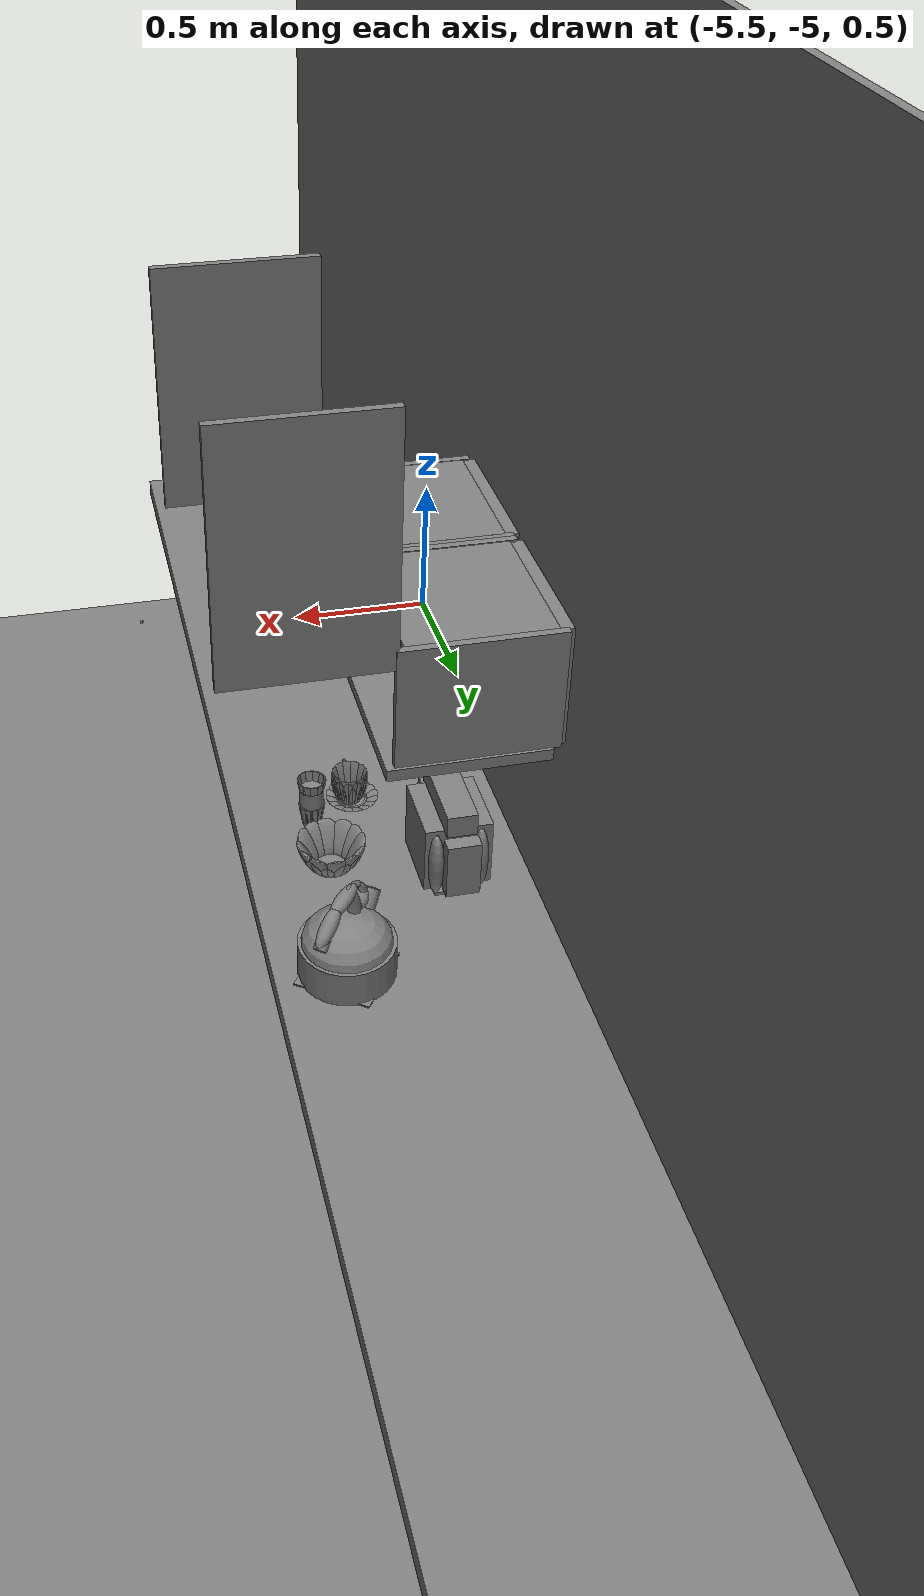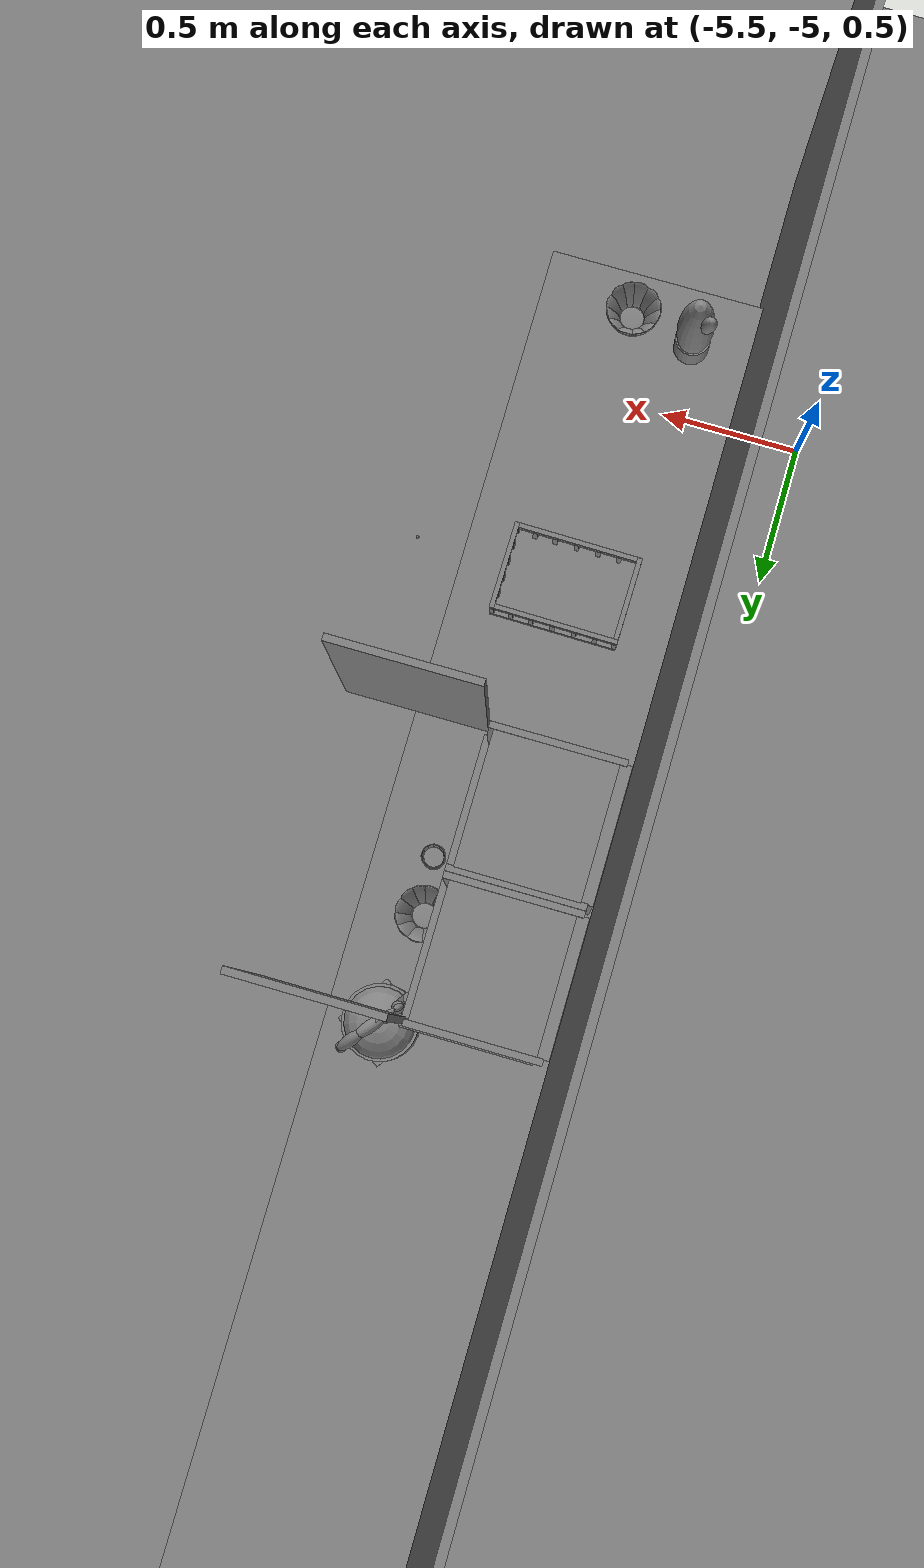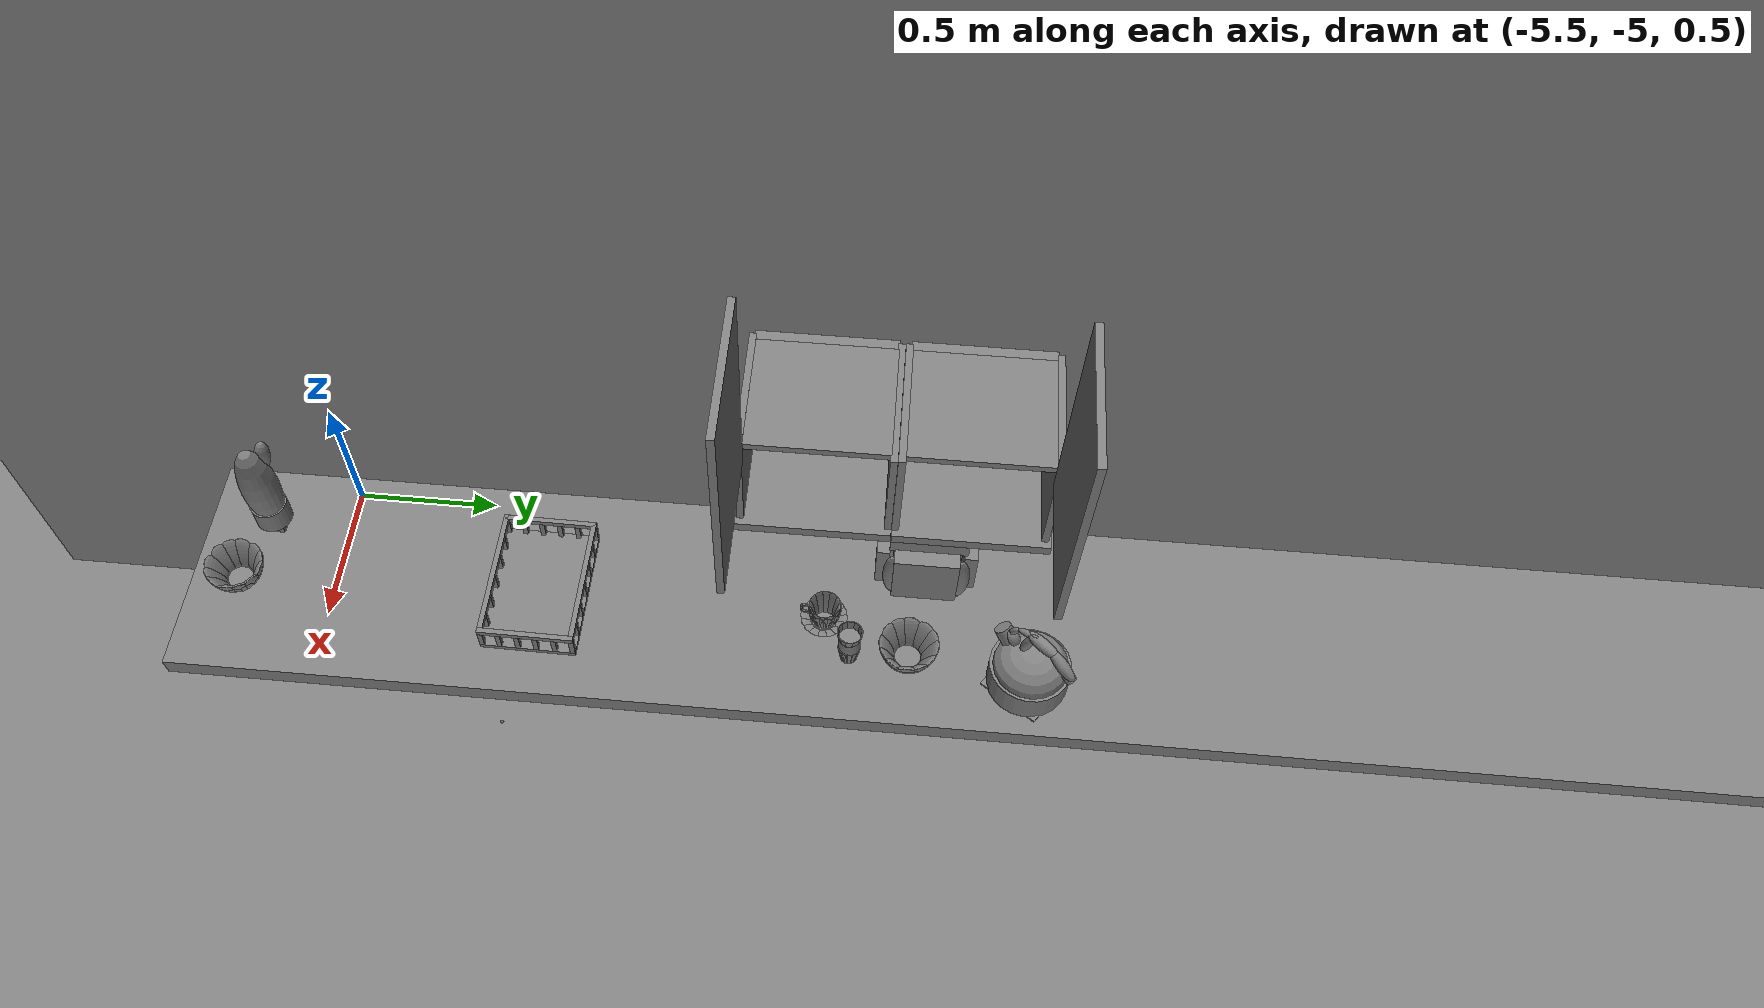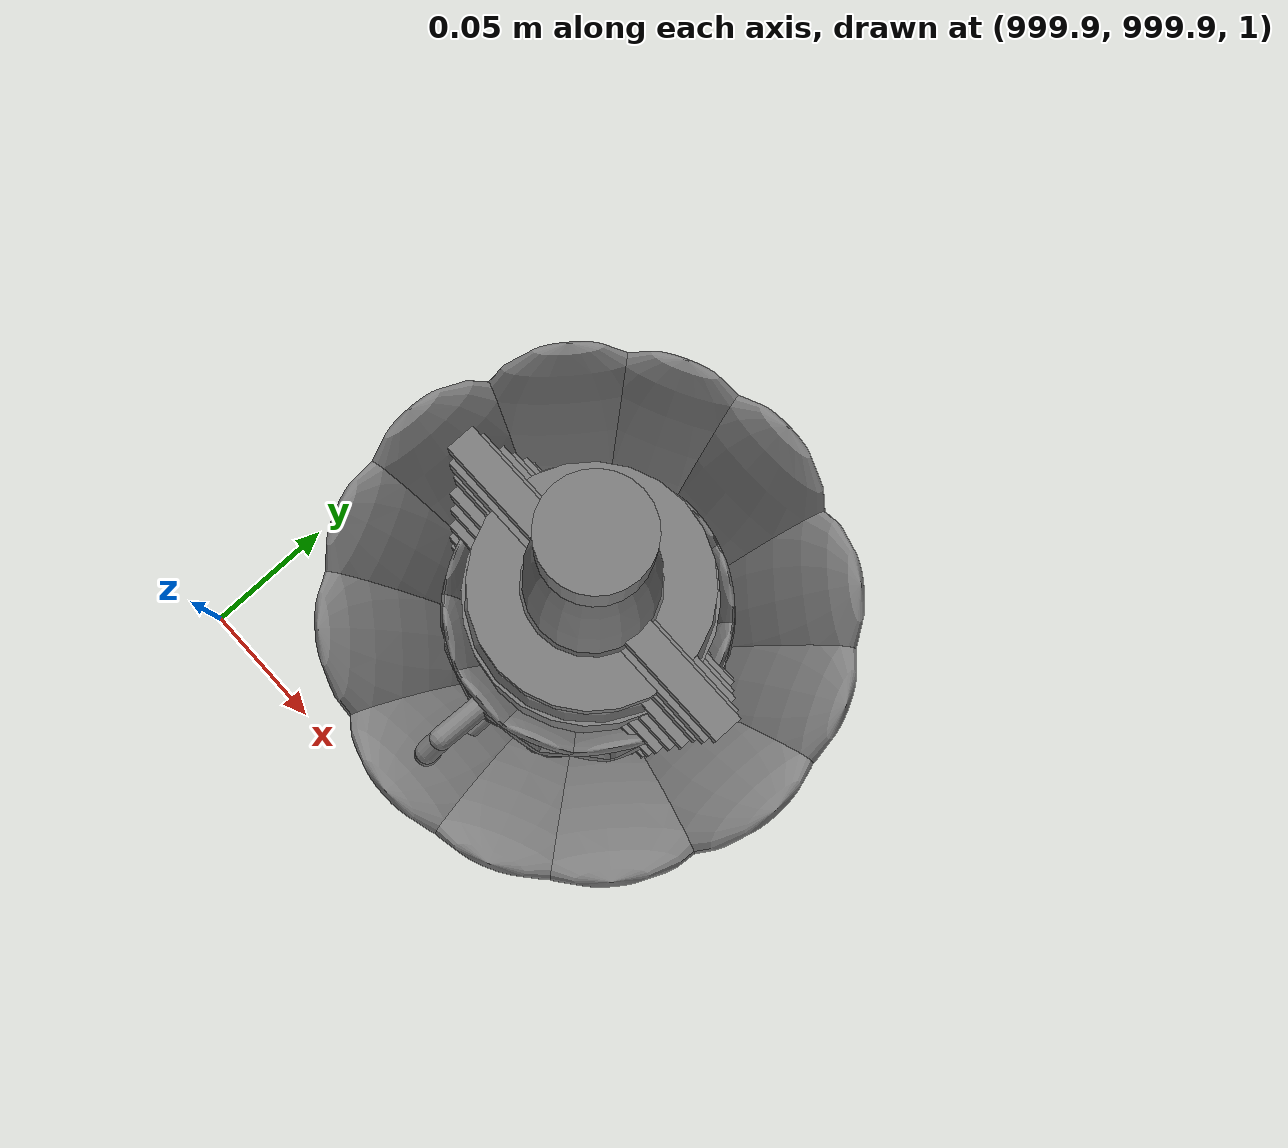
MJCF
<mujoco>
    <option gravity="0.000000000 0.000000000 -9.810000420" timestep="0.0049999999" integrator="implicitfast" density="9.8000002" viscosity="1.8000001e-05" noslip_iterations="10" iterations="100" sdf_iterations="50">
        <flag multiccd="disable"/>
    </option>
    <size memory="1000M"/>
    <compiler coordinate="local"/>
    <worldbody>
        <light cutoff="30" pos="0 1 1" dir="0 -1 -2"/>
        <light cutoff="30" pos="0 -1 1" dir="0 1 -2"/>
        <body pos="-5.046103477 -5.051773071 1.001502514" euler="0.000000000 0.000000000 0.000000000" name="Interactive Objcets_huapen">
            <geom contype="1" conaffinity="1" density="1000" type="ellipsoid" material="" rgba="0.500000000 0.500000000 0.500000000 1.000000000" solimp="0.899999976 0.949999988 0.001000000" friction="1.000000000 0.005000000 0.000100000" solref="0.020000000 1.000000000" margin="0" condim="3" group="0" pos="0.008062840 0.004346371 0.205056787" quat="1.000000000 0.000000000 0.000000000 0.000000000" size="0.059999999 0.059999999 0.180000007" name="Interactive Objcets_huapen_hua_8563BEC4_1610_46D3_A209_5DED37BB011B"/>
            <geom contype="1" conaffinity="1" density="1000" type="cylinder" material="" rgba="0.500000000 0.500000000 0.500000000 1.000000000" solimp="0.899999976 0.949999988 0.001000000" friction="1.000000000 0.005000000 0.000100000" solref="0.020000000 1.000000000" margin="0" condim="3" group="0" pos="0.008062840 0.003952026 0.080107450" quat="1.000000000 0.000000000 0.000000000 0.000000000" size="0.057999998 0.039999999 1.000000000" name="Interactive Objcets_huapen_hua_268779E4_F084_4014_9F1A_ED5C4F279353"/>
            <geom contype="1" conaffinity="1" density="1000" type="box" material="" rgba="0.500000000 0.500000000 0.500000000 1.000000000" solimp="0.899999976 0.949999988 0.001000000" friction="1.000000000 0.005000000 0.000100000" solref="0.020000000 1.000000000" margin="0" condim="3" group="0" pos="0.008062840 0.003952503 0.020566106" quat="1.000000000 0.000000000 0.000000000 0.000000000" size="0.035000000 0.035000000 0.020000000" name="Interactive Objcets_huapen_hua_E85A05FF_840D_4A00_BA0F_C1A55F17FBD4"/>
            <geom contype="1" conaffinity="1" density="1000" type="ellipsoid" material="" rgba="0.500000000 0.500000000 0.500000000 1.000000000" solimp="0.899999976 0.949999988 0.001000000" friction="1.000000000 0.005000000 0.000100000" solref="0.020000000 1.000000000" margin="0" condim="3" group="0" pos="-0.029900074 0.033599377 0.321917295" quat="0.992658079 -0.083605267 -0.087364964 0.002748166" size="0.025000000 0.025000000 0.059999999" name="Interactive Objcets_huapen_hua_69FF73E5_96D7_4812_B538_B1F766F7300B"/>
            <freejoint name="Interactive Objcets_huapen"/>
        </body>
        <body pos="-4.352927685 -4.005394936 1.750362635" euler="-118.577445984 -17.732688904 -172.986816406" mocap="true" name="spotlight4_SpotLight"/>
        <body pos="1000.000000000 1000.000000000 1.000000000" euler="0.000000000 0.000000000 0.000000000" name="openloong_gripper_2f85_fix_base_usda_bow_yellow_kps">
            <geom contype="1" conaffinity="1" density="1000" type="ellipsoid" material="" rgba="0.500000000 0.500000000 0.500000000 1.000000000" solimp="0.899999976 0.949999988 0.001000000" friction="1.000000000 0.005000000 0.000100000" solref="0.020000000 1.000000000" margin="0" condim="3" group="0" pos="-0.052185059 0.040283203 0.044118762" quat="0.919264615 -0.076883033 -0.225593656 -0.313287765" size="0.010000000 0.039999999 0.052000001" name="openloong_gripper_2f85_fix_base_usda_geom_E5A49FE9_08D3_4ABF_985A_7AD5C917D5EC"/>
            <geom contype="1" conaffinity="1" density="1000" type="ellipsoid" material="" rgba="0.500000000 0.500000000 0.500000000 1.000000000" solimp="0.899999976 0.949999988 0.001000000" friction="1.000000000 0.005000000 0.000100000" solref="0.020000000 1.000000000" margin="0" condim="3" group="0" pos="-0.000061035 0.065979004 0.044118762" quat="0.687598765 -0.168314874 -0.168741167 -0.685860336" size="0.010000000 0.039999999 0.052000001" name="openloong_gripper_2f85_fix_base_usda_geom_DD04F649_A7E2_4613_9E97_390083AA8C8C"/>
            <geom contype="1" conaffinity="1" density="1000" type="box" material="" rgba="0.500000000 0.500000000 0.500000000 1.000000000" solimp="0.899999976 0.949999988 0.001000000" friction="1.000000000 0.005000000 0.000100000" solref="0.020000000 1.000000000" margin="0" condim="3" group="0" pos="0.000061035 0.000000000 -0.002001643" quat="1.000000000 0.000000000 0.000000000 0.000000000" size="0.029999999 0.029999999 0.002000000" name="openloong_gripper_2f85_fix_base_usda_geom_BF3484A2_E1E3_4B05_9765_229DF1A509A6"/>
            <geom contype="1" conaffinity="1" density="1000" type="ellipsoid" material="" rgba="0.500000000 0.500000000 0.500000000 1.000000000" solimp="0.899999976 0.949999988 0.001000000" friction="1.000000000 0.005000000 0.000100000" solref="0.020000000 1.000000000" margin="0" condim="3" group="0" pos="0.029418945 -0.059082031 0.044118762" quat="0.825555861 0.125530601 0.202597082 -0.511521280" size="0.010000000 0.039999999 0.052000001" name="openloong_gripper_2f85_fix_base_usda_geom_B89A509E_EC10_4F1C_9284_9412BF816AC3"/>
            <geom contype="1" conaffinity="1" density="1000" type="ellipsoid" material="" rgba="0.500000000 0.500000000 0.500000000 1.000000000" solimp="0.899999976 0.949999988 0.001000000" friction="1.000000000 0.005000000 0.000100000" solref="0.020000000 1.000000000" margin="0" condim="3" group="0" pos="0.000244141 -0.065979004 0.044118762" quat="0.687598765 0.168314651 0.168741375 -0.685860336" size="0.010000000 0.039999999 0.052000001" name="openloong_gripper_2f85_fix_base_usda_geom_91C45C20_51BC_42FF_957B_18D6258E8979"/>
            <geom contype="1" conaffinity="1" density="1000" type="ellipsoid" material="" rgba="0.500000000 0.500000000 0.500000000 1.000000000" solimp="0.899999976 0.949999988 0.001000000" friction="1.000000000 0.005000000 0.000100000" solref="0.020000000 1.000000000" margin="0" condim="3" group="0" pos="0.000061035 0.000000000 0.000446677" quat="1.000000000 0.000000000 0.000000000 0.000000000" size="0.039999999 0.039999999 0.002000000" name="openloong_gripper_2f85_fix_base_usda_geom_C503C370_889C_46BE_A432_C99608092207"/>
            <geom contype="1" conaffinity="1" density="1000" type="ellipsoid" material="" rgba="0.500000000 0.500000000 0.500000000 1.000000000" solimp="0.899999976 0.949999988 0.001000000" friction="1.000000000 0.005000000 0.000100000" solref="0.020000000 1.000000000" margin="0" condim="3" group="0" pos="0.059082031 0.029541016 0.044118762" quat="0.223252773 -0.231952220 -0.054787423 -0.945174456" size="0.010000000 0.039999999 0.052000001" name="openloong_gripper_2f85_fix_base_usda_geom_9F97A393_4B10_4DF9_AA78_14CFBE00628C"/>
            <geom contype="1" conaffinity="1" density="1000" type="ellipsoid" material="" rgba="0.500000000 0.500000000 0.500000000 1.000000000" solimp="0.899999976 0.949999988 0.001000000" friction="1.000000000 0.005000000 0.000100000" solref="0.020000000 1.000000000" margin="0" condim="3" group="0" pos="0.000061035 0.000000000 0.007335305" quat="1.000000000 0.000000000 0.000000000 0.000000000" size="0.039999999 0.039999999 0.002000000" name="openloong_gripper_2f85_fix_base_usda_geom_BFCFF03F_FDDE_4F0F_9614_BDC72DF03646"/>
            <geom contype="1" conaffinity="1" density="1000" type="ellipsoid" material="" rgba="0.500000000 0.500000000 0.500000000 1.000000000" solimp="0.899999976 0.949999988 0.001000000" friction="1.000000000 0.005000000 0.000100000" solref="0.020000000 1.000000000" margin="0" condim="3" group="0" pos="-0.029296875 0.059082031 0.044118762" quat="0.825555861 -0.125530809 -0.202596918 -0.511521280" size="0.010000000 0.039999999 0.052000001" name="openloong_gripper_2f85_fix_base_usda_geom_39F5B8E8_2D78_4385_8C4D_E784C830AE5F"/>
            <geom contype="1" conaffinity="1" density="1000" type="ellipsoid" material="" rgba="0.500000000 0.500000000 0.500000000 1.000000000" solimp="0.899999976 0.949999988 0.001000000" friction="1.000000000 0.005000000 0.000100000" solref="0.020000000 1.000000000" margin="0" condim="3" group="0" pos="0.040222168 0.052368164 0.044118762" quat="0.429593176 -0.213750049 -0.105424821 -0.871002972" size="0.010000000 0.039999999 0.052000001" name="openloong_gripper_2f85_fix_base_usda_geom_96E42A84_74D8_4D5D_BDE0_56E7F7F5F895"/>
            <geom contype="1" conaffinity="1" density="1000" type="ellipsoid" material="" rgba="0.500000000 0.500000000 0.500000000 1.000000000" solimp="0.899999976 0.949999988 0.001000000" friction="1.000000000 0.005000000 0.000100000" solref="0.020000000 1.000000000" margin="0" condim="3" group="0" pos="0.066040039 0.000000000 0.044118762" quat="0.971183062 -0.000000156 0.238334835 0.000000030" size="0.010000000 0.039999999 0.052000001" name="openloong_gripper_2f85_fix_base_usda_geom_582C421B_2AD2_43CE_BBB7_3B276471CE36"/>
            <geom contype="1" conaffinity="1" density="1000" type="ellipsoid" material="" rgba="0.500000000 0.500000000 0.500000000 1.000000000" solimp="0.899999976 0.949999988 0.001000000" friction="1.000000000 0.005000000 0.000100000" solref="0.020000000 1.000000000" margin="0" condim="3" group="0" pos="0.052307129 -0.040283203 0.044118762" quat="0.919264674 0.076882750 0.225593731 -0.313287705" size="0.010000000 0.039999999 0.052000001" name="openloong_gripper_2f85_fix_base_usda_geom_4B71FF45_6D59_48C3_AE7C_E3B43BF3B9AB"/>
            <geom contype="1" conaffinity="1" density="1000" type="ellipsoid" material="" rgba="0.500000000 0.500000000 0.500000000 1.000000000" solimp="0.899999976 0.949999988 0.001000000" friction="1.000000000 0.005000000 0.000100000" solref="0.020000000 1.000000000" margin="0" condim="3" group="0" pos="-0.065917969 0.000000000 0.044118762" quat="0.971183062 -0.000000142 -0.238334835 0.000000030" size="0.010000000 0.039999999 0.052000001" name="openloong_gripper_2f85_fix_base_usda_geom_E09E57F1_482A_46D7_BB9C_27CEE6481F6A"/>
            <geom contype="1" conaffinity="1" density="1000" type="ellipsoid" material="" rgba="0.500000000 0.500000000 0.500000000 1.000000000" solimp="0.899999976 0.949999988 0.001000000" friction="1.000000000 0.005000000 0.000100000" solref="0.020000000 1.000000000" margin="0" condim="3" group="0" pos="-0.058898926 -0.029541016 0.044118762" quat="0.223252758 0.231952101 0.054787733 -0.945174575" size="0.010000000 0.039999999 0.052000001" name="openloong_gripper_2f85_fix_base_usda_geom_ED7059D0_6590_446F_845F_41BA6D5EC573"/>
            <geom contype="1" conaffinity="1" density="1000" type="ellipsoid" material="" rgba="0.500000000 0.500000000 0.500000000 1.000000000" solimp="0.899999976 0.949999988 0.001000000" friction="1.000000000 0.005000000 0.000100000" solref="0.020000000 1.000000000" margin="0" condim="3" group="0" pos="-0.040100098 -0.052368164 0.044118762" quat="0.429593235 0.213749886 0.105425082 -0.871003032" size="0.010000000 0.039999999 0.052000001" name="openloong_gripper_2f85_fix_base_usda_geom_EBA095B6_896B_4110_AA34_346D53010ADB"/>
            <freejoint name="openloong_gripper_2f85_fix_base_usda_bow_yellow_kps_joint"/>
            <site size="0.005000000 0.005000000 0.005000000" rgba="0.500000000 0.500000000 0.500000000 1.000000000" pos="0.000000000 0.000000000 0.000000000" quat="0.999961913 0.008726534 0.000000000 0.000000000" group="0" type="sphere" name="openloong_gripper_2f85_fix_base_usda_bow_yellow_kps"/>
        </body>
        <body pos="1000.000000000 1000.000000000 1.000000000" euler="0.000000000 0.000000000 0.000000000" name="openloong_gripper_2f85_fix_base_usda_bottle_red">
            <geom contype="1" conaffinity="1" density="1000" type="ellipsoid" material="" rgba="0.500000000 0.500000000 0.500000000 1.000000000" solimp="0.899999976 0.949999988 0.001000000" friction="1.000000000 0.005000000 0.000100000" solref="0.020000000 1.000000000" margin="0" condim="3" group="0" pos="0.000000000 0.000000000 0.144284487" quat="1.000000000 0.000000000 0.000000000 0.000000000" size="0.021000000 0.021000000 0.079999998" name="openloong_gripper_2f85_fix_base_usda_geom_28B7B90D_F191_4441_B82C_9779D3F72101"/>
            <geom contype="1" conaffinity="1" density="1000" type="cylinder" material="" rgba="0.500000000 0.500000000 0.500000000 1.000000000" solimp="0.899999976 0.949999988 0.001000000" friction="1.000000000 0.005000000 0.000100000" solref="0.020000000 1.000000000" margin="0" condim="3" group="0" pos="0.000000000 0.000000000 0.220618963" quat="1.000000000 0.000000000 0.000000000 0.000000000" size="0.016000001 0.010000000 1.000000000" name="openloong_gripper_2f85_fix_base_usda_geom_FDB8CAF1_5938_4E87_9885_4C15CBF0EC73"/>
            <geom contype="1" conaffinity="1" density="1000" type="ellipsoid" material="" rgba="0.500000000 0.500000000 0.500000000 1.000000000" solimp="0.899999976 0.949999988 0.001000000" friction="1.000000000 0.005000000 0.000100000" solref="0.020000000 1.000000000" margin="0" condim="3" group="0" pos="0.000000000 0.000000000 0.118945479" quat="1.000000000 0.000000000 0.000000000 0.000000000" size="0.030999999 0.030999999 0.029999999" name="openloong_gripper_2f85_fix_base_usda_geom_8B165B12_DB22_4448_BD8A_9B78C34A1782"/>
            <geom contype="1" conaffinity="1" density="1000" type="box" material="" rgba="0.500000000 0.500000000 0.500000000 1.000000000" solimp="0.899999976 0.949999988 0.001000000" friction="1.000000000 0.005000000 0.000100000" solref="0.020000000 1.000000000" margin="0" condim="3" group="0" pos="0.000000000 0.000000000 0.002189159" quat="1.000000000 0.000000000 0.000000000 0.000000000" size="0.020000000 0.020000000 0.003000000" name="openloong_gripper_2f85_fix_base_usda_geom_277445F6_C0F9_4165_8D58_B9AEE7F58C96"/>
            <geom contype="1" conaffinity="1" density="1000" type="cylinder" material="" rgba="0.500000000 0.500000000 0.500000000 1.000000000" solimp="0.899999976 0.949999988 0.001000000" friction="1.000000000 0.005000000 0.000100000" solref="0.020000000 1.000000000" margin="0" condim="3" group="0" pos="0.000000000 -0.000366211 0.060884237" quat="1.000000000 0.000000000 0.000000000 0.000000000" size="0.030999999 0.057999998 1.000000000" name="openloong_gripper_2f85_fix_base_usda_geom_C3F9218E_BAC0_4A82_856B_C2C315968EDA"/>
            <freejoint name="openloong_gripper_2f85_fix_base_usda_bottle_red_joint"/>
            <site size="0.005000000 0.005000000 0.005000000" rgba="0.500000000 0.500000000 0.500000000 1.000000000" pos="0.000000000 0.000000000 0.000000000" quat="0.999961913 0.008726535 0.000000000 0.000000000" group="0" type="sphere" name="openloong_gripper_2f85_fix_base_usda_bottle_redsite"/>
        </body>
        <body pos="-4.071927071 -4.210383415 1.850378036" euler="-54.640422821 87.257087708 78.402206421" mocap="true" name="spotlight5_SpotLight"/>
        <body pos="1000.000000000 1000.000000000 1.000000000" euler="0.000000000 0.000000000 0.000000000" name="openloong_gripper_2f85_fix_base_usda_salt">
            <geom contype="1" conaffinity="1" density="1000" type="box" material="" rgba="0.500000000 0.500000000 0.500000000 1.000000000" solimp="0.899999976 0.949999988 0.001000000" friction="1.000000000 0.005000000 0.000100000" solref="0.020000000 1.000000000" margin="0" condim="3" group="0" pos="0.000305176 0.000000000 0.084862232" quat="1.000000000 0.000000000 0.000000000 0.000000000" size="0.048999999 0.018999999 0.005000000" name="openloong_gripper_2f85_fix_base_usda_geom_D0BE9083_3AC8_4D14_B454_9832A056D65C"/>
            <geom contype="1" conaffinity="1" density="1000" type="box" material="" rgba="0.500000000 0.500000000 0.500000000 1.000000000" solimp="0.899999976 0.949999988 0.001000000" friction="1.000000000 0.005000000 0.000100000" solref="0.020000000 1.000000000" margin="0" condim="3" group="0" pos="0.000305176 0.000000000 0.104564309" quat="1.000000000 0.000000000 0.000000000 0.000000000" size="0.052000001 0.014000000 0.005000000" name="openloong_gripper_2f85_fix_base_usda_geom_6C8E2BB9_B44E_416F_9DEE_DFC045B69EA5"/>
            <geom contype="1" conaffinity="1" density="1000" type="box" material="" rgba="0.500000000 0.500000000 0.500000000 1.000000000" solimp="0.899999976 0.949999988 0.001000000" friction="1.000000000 0.005000000 0.000100000" solref="0.020000000 1.000000000" margin="0" condim="3" group="0" pos="0.000305176 0.000000000 0.114487171" quat="1.000000000 0.000000000 0.000000000 0.000000000" size="0.054000001 0.011500000 0.005000000" name="openloong_gripper_2f85_fix_base_usda_geom_808338C0_4911_4D96_8E19_36D91B4E31B0"/>
            <geom contype="1" conaffinity="1" density="1000" type="box" material="" rgba="0.500000000 0.500000000 0.500000000 1.000000000" solimp="0.899999976 0.949999988 0.001000000" friction="1.000000000 0.005000000 0.000100000" solref="0.020000000 1.000000000" margin="0" condim="3" group="0" pos="0.000305176 0.000000000 0.075103164" quat="1.000000000 0.000000000 0.000000000 0.000000000" size="0.048000000 0.020000000 0.005000000" name="openloong_gripper_2f85_fix_base_usda_geom_C444B68B_0819_4775_9310_F30E166EF772"/>
            <geom contype="1" conaffinity="1" density="1000" type="box" material="" rgba="0.500000000 0.500000000 0.500000000 1.000000000" solimp="0.899999976 0.949999988 0.001000000" friction="1.000000000 0.005000000 0.000100000" solref="0.020000000 1.000000000" margin="0" condim="3" group="0" pos="0.000305176 0.000000000 0.134892464" quat="1.000000000 0.000000000 0.000000000 0.000000000" size="0.057000000 0.007000000 0.005000000" name="openloong_gripper_2f85_fix_base_usda_geom_A37004E5_C400_4B87_89C0_1052A6DE656F"/>
            <geom contype="1" conaffinity="1" density="1000" type="box" material="" rgba="0.500000000 0.500000000 0.500000000 1.000000000" solimp="0.899999976 0.949999988 0.001000000" friction="1.000000000 0.005000000 0.000100000" solref="0.020000000 1.000000000" margin="0" condim="3" group="0" pos="0.000305176 0.000000000 0.094920278" quat="1.000000000 0.000000000 0.000000000 0.000000000" size="0.050000001 0.017000001 0.005000000" name="openloong_gripper_2f85_fix_base_usda_geom_D528AE81_BDCC_4A9B_BBFF_08AE6DEE2E54"/>
            <geom contype="1" conaffinity="1" density="1000" type="box" material="" rgba="0.500000000 0.500000000 0.500000000 1.000000000" solimp="0.899999976 0.949999988 0.001000000" friction="1.000000000 0.005000000 0.000100000" solref="0.020000000 1.000000000" margin="0" condim="3" group="0" pos="0.000305176 0.000000000 0.065204859" quat="1.000000000 0.000000000 0.000000000 0.000000000" size="0.045000002 0.021000000 0.005000000" name="openloong_gripper_2f85_fix_base_usda_geom_31DAB049_CAD6_42A2_B546_59B0123DEBB8"/>
            <geom contype="1" conaffinity="1" density="1000" type="box" material="" rgba="0.500000000 0.500000000 0.500000000 1.000000000" solimp="0.899999976 0.949999988 0.001000000" friction="1.000000000 0.005000000 0.000100000" solref="0.020000000 1.000000000" margin="0" condim="3" group="0" pos="0.000305176 0.000000000 0.144135714" quat="1.000000000 0.000000000 0.000000000 0.000000000" size="0.059000000 0.005000000 0.004000000" name="openloong_gripper_2f85_fix_base_usda_geom_94B7F29B_3E68_4DA7_AE9B_D925728E5231"/>
            <geom contype="1" conaffinity="1" density="1000" type="box" material="" rgba="0.500000000 0.500000000 0.500000000 1.000000000" solimp="0.899999976 0.949999988 0.001000000" friction="1.000000000 0.005000000 0.000100000" solref="0.020000000 1.000000000" margin="0" condim="3" group="0" pos="0.000000000 0.000000000 0.031593561" quat="1.000000000 0.000000000 0.000000000 0.000000000" size="0.041999999 0.024000000 0.029999999" name="openloong_gripper_2f85_fix_base_usda_geom_DC669255_09A2_4270_8B57_57BF51B1045A"/>
            <geom contype="1" conaffinity="1" density="1000" type="box" material="" rgba="0.500000000 0.500000000 0.500000000 1.000000000" solimp="0.899999976 0.949999988 0.001000000" friction="1.000000000 0.005000000 0.000100000" solref="0.020000000 1.000000000" margin="0" condim="3" group="0" pos="0.000305176 0.000000000 0.124608755" quat="1.000000000 0.000000000 0.000000000 0.000000000" size="0.055000000 0.008000000 0.005000000" name="openloong_gripper_2f85_fix_base_usda_geom_AF57F94D_4AC1_4C42_AEFA_B2CA80574FC3"/>
            <freejoint name="openloong_gripper_2f85_fix_base_usda_salt_joint"/>
            <site size="0.005000000 0.005000000 0.005000000" rgba="0.500000000 0.500000000 0.500000000 1.000000000" pos="0.000000000 0.000000000 0.000000000" quat="1.000000000 0.000000000 0.000000000 0.000000000" group="0" type="sphere" name="openloong_gripper_2f85_fix_base_usda_saltsite"/>
        </body>
        <body pos="1000.000000000 1000.000000000 1.000000000" euler="0.000000000 0.000000000 0.000000000" name="openloong_gripper_2f85_fix_base_usda_jar_01">
            <geom contype="1" conaffinity="1" density="1000" type="box" material="" rgba="0.500000000 0.500000000 0.500000000 1.000000000" solimp="0.899999976 0.949999988 0.001000000" friction="1.000000000 0.005000000 0.000100000" solref="0.020000000 1.000000000" margin="0" condim="3" group="0" pos="0.000000000 0.000000000 0.006158113" quat="1.000000000 0.000000000 0.000000000 0.000000000" size="0.020000000 0.020000000 0.005000000" name="openloong_gripper_2f85_fix_base_usda_geom_8F582563_8F75_4312_8084_EF9AD515777F"/>
            <geom contype="1" conaffinity="1" density="1000" type="cylinder" material="" rgba="0.500000000 0.500000000 0.500000000 1.000000000" solimp="0.899999976 0.949999988 0.001000000" friction="1.000000000 0.005000000 0.000100000" solref="0.020000000 1.000000000" margin="0" condim="3" group="0" pos="0.000000000 0.000000000 0.062744498" quat="1.000000000 0.000000000 0.000000000 0.000000000" size="0.041000001 0.052999999 1.000000000" name="openloong_gripper_2f85_fix_base_usda_geom_0512EA29_2905_45CA_B259_D55C77FB4962"/>
            <geom contype="1" conaffinity="1" density="1000" type="ellipsoid" material="" rgba="0.500000000 0.500000000 0.500000000 1.000000000" solimp="0.899999976 0.949999988 0.001000000" friction="1.000000000 0.005000000 0.000100000" solref="0.020000000 1.000000000" margin="0" condim="3" group="0" pos="0.000000000 0.000000000 0.122252703" quat="1.000000000 0.000000000 0.000000000 0.000000000" size="0.035999998 0.035999998 0.010000000" name="openloong_gripper_2f85_fix_base_usda_geom_6B47F29D_4EBF_4235_96F2_948E9442D7A0"/>
            <geom contype="1" conaffinity="1" density="1000" type="cylinder" material="" rgba="0.500000000 0.500000000 0.500000000 1.000000000" solimp="0.899999976 0.949999988 0.001000000" friction="1.000000000 0.005000000 0.000100000" solref="0.020000000 1.000000000" margin="0" condim="3" group="0" pos="0.000000000 0.000000000 0.015747190" quat="1.000000000 0.000000000 0.000000000 0.000000000" size="0.035000000 0.010000000 1.000000000" name="openloong_gripper_2f85_fix_base_usda_geom_6851AF46_FE6D_46D0_A2A5_7101A3617476"/>
            <geom contype="1" conaffinity="1" density="1000" type="ellipsoid" material="" rgba="0.500000000 0.500000000 0.500000000 1.000000000" solimp="0.899999976 0.949999988 0.001000000" friction="1.000000000 0.005000000 0.000100000" solref="0.020000000 1.000000000" margin="0" condim="3" group="0" pos="0.000000000 0.000000000 0.115815401" quat="1.000000000 0.000000000 0.000000000 0.000000000" size="0.039999999 0.039999999 0.010000000" name="openloong_gripper_2f85_fix_base_usda_geom_700EC115_3934_4100_893D_515E67AB4817"/>
            <geom contype="1" conaffinity="1" density="1000" type="cylinder" material="" rgba="0.500000000 0.500000000 0.500000000 1.000000000" solimp="0.899999976 0.949999988 0.001000000" friction="1.000000000 0.005000000 0.000100000" solref="0.020000000 1.000000000" margin="0" condim="3" group="0" pos="0.000000000 0.000000000 0.133183479" quat="1.000000000 0.000000000 0.000000000 0.000000000" size="0.037999999 0.006500000 1.000000000" name="openloong_gripper_2f85_fix_base_usda_geom_AF71BB22_E57A_4057_AE29_7D9C56CF864A"/>
            <freejoint name="openloong_gripper_2f85_fix_base_usda_jar_01_joint"/>
            <site size="0.005000000 0.005000000 0.005000000" rgba="0.500000000 0.500000000 0.500000000 1.000000000" pos="0.000000000 0.000000000 0.000000000" quat="1.000000000 0.000000000 0.000000000 0.000000000" group="0" type="sphere" name="openloong_gripper_2f85_fix_base_usda_jar_01site"/>
        </body>
        <body pos="1000.000000000 1000.000000000 1.000000000" euler="0.000000000 0.000000000 0.000000000" name="openloong_gripper_2f85_fix_base_usda_coffeecup_white_kps">
            <geom contype="1" conaffinity="1" density="1000" type="capsule" material="" rgba="0.500000000 0.500000000 0.500000000 1.000000000" solimp="0.899999976 0.949999988 0.001000000" friction="1.000000000 0.005000000 0.000100000" solref="0.020000000 1.000000000" margin="0" condim="3" group="0" pos="-0.000854492 -0.065795898 0.050029993" quat="0.343559504 -0.613204718 0.626912475 0.336047262" size="0.004000000 0.005000000 1.000000000" name="openloong_gripper_2f85_fix_base_usda_geom_4A7516D6_6299_44C8_AAA3_1C9202586FD3"/>
            <geom contype="1" conaffinity="1" density="1000" type="ellipsoid" material="" rgba="0.500000000 0.500000000 0.500000000 1.000000000" solimp="0.899999976 0.949999988 0.001000000" friction="1.000000000 0.005000000 0.000100000" solref="0.020000000 1.000000000" margin="0" condim="3" group="0" pos="-0.000793457 -0.038452148 0.048040152" quat="0.711656272 0.066323131 -0.067805752 0.696095467" size="0.005000000 0.029999999 0.048999999" name="openloong_gripper_2f85_fix_base_usda_geom_382F1339_D921_4F0D_B30D_91CBDBDB79E9"/>
            <geom contype="1" conaffinity="1" density="1000" type="ellipsoid" material="" rgba="0.500000000 0.500000000 0.500000000 1.000000000" solimp="0.899999976 0.949999988 0.001000000" friction="1.000000000 0.005000000 0.000100000" solref="0.020000000 1.000000000" margin="0" condim="3" group="0" pos="0.037719727 -0.001892090 0.048040152" quat="0.995387912 0.001371633 0.094835162 -0.014391154" size="0.005000000 0.029999999 0.048999999" name="openloong_gripper_2f85_fix_base_usda_geom_4DAF505B_3A4D_443D_8F97_B5968F850811"/>
            <geom contype="1" conaffinity="1" density="1000" type="ellipsoid" material="" rgba="0.500000000 0.500000000 0.500000000 1.000000000" solimp="0.899999976 0.949999988 0.001000000" friction="1.000000000 0.005000000 0.000100000" solref="0.020000000 1.000000000" margin="0" condim="3" group="0" pos="0.033996582 0.015502930 0.048040152" quat="0.970659733 -0.021051638 0.092478797 0.220962167" size="0.005000000 0.029999999 0.048999999" name="openloong_gripper_2f85_fix_base_usda_geom_EF41B4FF_8CD5_4412_8CE8_15FBF7539EAC"/>
            <geom contype="1" conaffinity="1" density="1000" type="box" material="" rgba="0.500000000 0.500000000 0.500000000 1.000000000" solimp="0.899999976 0.949999988 0.001000000" friction="1.000000000 0.005000000 0.000100000" solref="0.020000000 1.000000000" margin="0" condim="3" group="0" pos="0.000793457 -0.000183105 0.000156164" quat="0.714879215 0.000000000 0.000000000 0.699247897" size="0.020000000 0.020000000 0.002000000" name="openloong_gripper_2f85_fix_base_usda_geom_CF3F7129_17E2_4D93_9688_8FB928A4AABA"/>
            <geom contype="1" conaffinity="1" density="1000" type="ellipsoid" material="" rgba="0.500000000 0.500000000 0.500000000 1.000000000" solimp="0.899999976 0.949999988 0.001000000" friction="1.000000000 0.005000000 0.000100000" solref="0.020000000 1.000000000" margin="0" condim="3" group="0" pos="-0.019409180 -0.033081055 0.048040152" quat="0.866879702 0.046630561 -0.082595348 0.489411235" size="0.005000000 0.029999999 0.048999999" name="openloong_gripper_2f85_fix_base_usda_geom_73919E80_6AE7_4465_A33E_0EB6807F6726"/>
            <geom contype="1" conaffinity="1" density="1000" type="ellipsoid" material="" rgba="0.500000000 0.500000000 0.500000000 1.000000000" solimp="0.899999976 0.949999988 0.001000000" friction="1.000000000 0.005000000 0.000100000" solref="0.020000000 1.000000000" margin="0" condim="3" group="0" pos="-0.016052246 0.033264160 0.048040152" quat="0.840792537 -0.050782297 -0.080109790 -0.532983541" size="0.005000000 0.029999999 0.048999999" name="openloong_gripper_2f85_fix_base_usda_geom_52ACD112_5A03_4C63_BCAD_627DB668F638"/>
            <geom contype="1" conaffinity="1" density="1000" type="capsule" material="" rgba="0.500000000 0.500000000 0.500000000 1.000000000" solimp="0.899999976 0.949999988 0.001000000" friction="1.000000000 0.005000000 0.000100000" solref="0.020000000 1.000000000" margin="0" condim="3" group="0" pos="-0.000549316 -0.053527832 0.046825886" quat="0.505496025 -0.494442940 0.505495846 0.494442940" size="0.004000000 0.005000000 1.000000000" name="openloong_gripper_2f85_fix_base_usda_geom_CDFD0F2F_24B1_438C_8AF5_609F435C4563"/>
            <geom contype="1" conaffinity="1" density="1000" type="ellipsoid" material="" rgba="0.500000000 0.500000000 0.500000000 1.000000000" solimp="0.899999976 0.949999988 0.001000000" friction="1.000000000 0.005000000 0.000100000" solref="0.020000000 1.000000000" margin="0" condim="3" group="0" pos="-0.032104492 0.018920898 0.048040152" quat="0.958129764 -0.025742561 -0.091288343 -0.270168930" size="0.005000000 0.029999999 0.048999999" name="openloong_gripper_2f85_fix_base_usda_geom_2C25A450_AEDB_44EE_85EB_F9D2B30D508C"/>
            <geom contype="1" conaffinity="1" density="1000" type="ellipsoid" material="" rgba="0.500000000 0.500000000 0.500000000 1.000000000" solimp="0.899999976 0.949999988 0.001000000" friction="1.000000000 0.005000000 0.000100000" solref="0.020000000 1.000000000" margin="0" condim="3" group="0" pos="-0.037597656 0.000305176 0.048040152" quat="0.995387554 -0.001371440 -0.094839431 -0.014389008" size="0.005000000 0.029999999 0.048999999" name="openloong_gripper_2f85_fix_base_usda_geom_D8F1E02E_F751_48AA_9974_C953BDD0D56A"/>
            <geom contype="1" conaffinity="1" density="1000" type="capsule" material="" rgba="0.500000000 0.500000000 0.500000000 1.000000000" solimp="0.899999976 0.949999988 0.001000000" friction="1.000000000 0.005000000 0.000100000" solref="0.020000000 1.000000000" margin="0" condim="3" group="0" pos="-0.000366211 -0.043762207 0.044118762" quat="0.260488123 -0.651174724 0.665731549 0.254792154" size="0.004000000 0.003000000 1.000000000" name="openloong_gripper_2f85_fix_base_usda_geom_8CE0CC03_31CE_4774_8054_5490C8A0AE23"/>
            <geom contype="1" conaffinity="1" density="1000" type="capsule" material="" rgba="0.500000000 0.500000000 0.500000000 1.000000000" solimp="0.899999976 0.949999988 0.001000000" friction="1.000000000 0.005000000 0.000100000" solref="0.020000000 1.000000000" margin="0" condim="3" group="0" pos="-0.000915527 -0.068542480 0.082936406" quat="0.624995589 -0.339446366 0.347034454 0.611329615" size="0.004000000 0.004000000 1.000000000" name="openloong_gripper_2f85_fix_base_usda_geom_6DCE543F_411D_4049_943D_61C099F2914C"/>
            <geom contype="1" conaffinity="1" density="1000" type="ellipsoid" material="" rgba="0.500000000 0.500000000 0.500000000 1.000000000" solimp="0.899999976 0.949999988 0.001000000" friction="1.000000000 0.005000000 0.000100000" solref="0.020000000 1.000000000" margin="0" condim="3" group="0" pos="0.016113281 -0.034851074 0.048040152" quat="0.840793252 0.050779939 0.080106191 -0.532983422" size="0.005000000 0.029999999 0.048999999" name="openloong_gripper_2f85_fix_base_usda_geom_9BE33DA6_7A6C_44E5_BA8F_8124883A6393"/>
            <geom contype="1" conaffinity="1" density="1000" type="ellipsoid" material="" rgba="0.500000000 0.500000000 0.500000000 1.000000000" solimp="0.899999976 0.949999988 0.001000000" friction="1.000000000 0.005000000 0.000100000" solref="0.020000000 1.000000000" margin="0" condim="3" group="0" pos="0.000854492 0.036865234 0.048040152" quat="0.711656570 -0.066320375 0.067802906 0.696095705" size="0.005000000 0.029999999 0.048999999" name="openloong_gripper_2f85_fix_base_usda_geom_C392F346_F973_40BF_B64A_1CCC74948118"/>
            <geom contype="1" conaffinity="1" density="1000" type="ellipsoid" material="" rgba="0.500000000 0.500000000 0.500000000 1.000000000" solimp="0.899999976 0.949999988 0.001000000" friction="1.000000000 0.005000000 0.000100000" solref="0.020000000 1.000000000" margin="0" condim="3" group="0" pos="-0.033935547 -0.017089844 0.048040152" quat="0.970659137 0.021052625 -0.092483103 0.220962465" size="0.005000000 0.029999999 0.048999999" name="openloong_gripper_2f85_fix_base_usda_geom_9BDA37F2_2C9D_4AF3_A1E1_E6C6909E251B"/>
            <geom contype="1" conaffinity="1" density="1000" type="ellipsoid" material="" rgba="0.500000000 0.500000000 0.500000000 1.000000000" solimp="0.899999976 0.949999988 0.001000000" friction="1.000000000 0.005000000 0.000100000" solref="0.020000000 1.000000000" margin="0" condim="3" group="0" pos="0.019531250 0.031494141 0.048040152" quat="0.866880119 -0.046628602 0.082591817 0.489411235" size="0.005000000 0.029999999 0.048999999" name="openloong_gripper_2f85_fix_base_usda_geom_DD8224CA_9914_488B_B51B_E64FF2E3D80C"/>
            <geom contype="1" conaffinity="1" density="1000" type="ellipsoid" material="" rgba="0.500000000 0.500000000 0.500000000 1.000000000" solimp="0.899999976 0.949999988 0.001000000" friction="1.000000000 0.005000000 0.000100000" solref="0.020000000 1.000000000" margin="0" condim="3" group="0" pos="0.032165527 -0.020507812 0.048040152" quat="0.958128154 0.025740955 0.091285400 -0.270175666" size="0.005000000 0.029999999 0.048999999" name="openloong_gripper_2f85_fix_base_usda_geom_A2244AC9_E514_4E7A_AA88_DE2243450918"/>
            <geom contype="1" conaffinity="1" density="1000" type="capsule" material="" rgba="0.500000000 0.500000000 0.500000000 1.000000000" solimp="0.899999976 0.949999988 0.001000000" friction="1.000000000 0.005000000 0.000100000" solref="0.020000000 1.000000000" margin="0" condim="3" group="0" pos="-0.000610352 -0.056823730 0.083572865" quat="0.452654332 -0.541215360 0.553313971 0.442756712" size="0.004000000 0.009000000 1.000000000" name="openloong_gripper_2f85_fix_base_usda_geom_53C5800E_1BA6_4AB4_8DD6_B6747788CBB7"/>
            <geom contype="1" conaffinity="1" density="1000" type="ellipsoid" material="" rgba="0.500000000 0.500000000 0.500000000 1.000000000" solimp="0.899999976 0.949999988 0.001000000" friction="1.000000000 0.005000000 0.000100000" solref="0.020000000 1.000000000" margin="0" condim="3" group="0" pos="0.000061035 -0.000183105 0.001848221" quat="0.714879215 0.000000000 0.000000000 0.699247897" size="0.029999999 0.029999999 0.001000000" name="openloong_gripper_2f85_fix_base_usda_geom_D2417DAD_F3DB_41AB_8D9C_120A3E205870"/>
            <geom contype="1" conaffinity="1" density="1000" type="capsule" material="" rgba="0.500000000 0.500000000 0.500000000 1.000000000" solimp="0.899999976 0.949999988 0.001000000" friction="1.000000000 0.005000000 0.000100000" solref="0.020000000 1.000000000" margin="0" condim="3" group="0" pos="-0.000976562 -0.071838379 0.066101432" quat="0.031849027 -0.698553741 0.714169443 0.031152546" size="0.004000000 0.012000000 1.000000000" name="openloong_gripper_2f85_fix_base_usda_geom_4CA6FAC1_DC4B_400F_81BA_8FD23EF9E102"/>
            <freejoint name="openloong_gripper_2f85_fix_base_usda_coffeecup_white_kps_joint"/>
            <site size="0.005000000 0.005000000 0.005000000" rgba="0.500000000 0.500000000 0.500000000 1.000000000" pos="0.000000000 0.000000000 0.000000000" quat="0.999961913 0.008726534 0.000000000 0.000000000" group="0" type="sphere" name="openloong_gripper_2f85_fix_base_usda_coffeecup_white_kps"/>
        </body>
        <body pos="-4.257844925 -4.434643269 1.749696016" euler="134.890960693 71.288475037 -50.779796600" mocap="true" name="spotlight2_SpotLight"/>
        <body pos="0.000000000 0.000000000 0.000000000" euler="0.000000000 0.000000000 0.000000000" name="Static Objcets_Static Objcets">
            <geom contype="1" conaffinity="1" density="1000" type="box" material="" rgba="0.500000000 0.500000000 0.500000000 1.000000000" solimp="0.899999976 0.949999988 0.001000000" friction="1.000000000 0.005000000 0.000100000" solref="0.020000000 1.000000000" margin="0" condim="3" group="0" pos="-4.999745846 -3.497932911 1.764780521" quat="0.707107067 0.707106471 0.000000000 0.000000000" size="0.200000003 0.159999996 0.010000000" name="Static Objcets_geom_60C2141D_A942_4D33_9575_9F155F08547E"/>
            <geom contype="1" conaffinity="1" density="1000" type="box" material="" rgba="0.500000000 0.500000000 0.500000000 1.000000000" solimp="0.899999976 0.949999988 0.001000000" friction="1.000000000 0.005000000 0.000100000" solref="0.020000000 1.000000000" margin="0" condim="3" group="0" pos="-4.979488373 -3.297635794 1.591412544" quat="0.707106829 0.707106709 0.000000000 0.000000000" size="0.200000003 0.015000000 0.219999999" name="Static Objcets_geom_F5C13FD0_9061_42BB_A2AD_A23B89B1A8E0"/>
            <geom contype="1" conaffinity="1" density="1000" type="box" material="" rgba="0.500000000 0.500000000 0.500000000 1.000000000" solimp="0.899999976 0.949999988 0.001000000" friction="1.000000000 0.005000000 0.000100000" solref="0.020000000 1.000000000" margin="0" condim="3" group="0" pos="-4.999745846 -3.087441683 1.763863802" quat="0.707107067 0.707106471 0.000000000 0.000000000" size="0.200000003 0.159999996 0.010000000" name="Static Objcets_geom_2E7FCAC5_47E6_43DC_8F07_A382342F35BB"/>
            <geom contype="1" conaffinity="1" density="1000" type="box" material="" rgba="0.500000000 0.500000000 0.500000000 1.000000000" solimp="0.899999976 0.949999988 0.001000000" friction="1.000000000 0.005000000 0.000100000" solref="0.020000000 1.000000000" margin="0" condim="3" group="0" pos="-5.189302921 -3.293644905 1.760152459" quat="0.707107067 0.707106471 0.000000000 0.000000000" size="0.025000000 0.159999996 0.200000003" name="Static Objcets_geom_0DDEE724_51CC_41CF_A496_EAFD98DDDE2C"/>
            <geom contype="1" conaffinity="1" density="1000" type="box" material="" rgba="0.500000000 0.500000000 0.500000000 1.000000000" solimp="0.899999976 0.949999988 0.001000000" friction="1.000000000 0.005000000 0.000100000" solref="0.020000000 1.000000000" margin="0" condim="3" group="0" pos="-5.000125408 -3.294431210 1.913951039" quat="0.707107067 0.707106471 0.000000000 0.000000000" size="0.180000007 0.010000000 0.200000003" name="Static Objcets_geom_DC0BC67B_6B01_42A5_8CDB_8A606F98A07F"/>
            <geom contype="1" conaffinity="1" density="1000" type="box" material="" rgba="0.500000000 0.500000000 0.500000000 1.000000000" solimp="0.899999976 0.949999988 0.001000000" friction="1.000000000 0.005000000 0.000100000" solref="0.020000000 1.000000000" margin="0" condim="3" group="0" pos="-5.000125408 -2.861802340 1.913950682" quat="0.707107067 0.707106471 0.000000000 0.000000000" size="0.180000007 0.010000000 0.200000003" name="Static Objcets_geom_BA569538_E0BB_4F78_B3E7_15CEF63BE48B"/>
            <geom contype="1" conaffinity="1" density="1000" type="box" material="" rgba="0.500000000 0.500000000 0.500000000 1.000000000" solimp="0.899999976 0.949999988 0.001000000" friction="1.000000000 0.005000000 0.000100000" solref="0.020000000 1.000000000" margin="0" condim="3" group="0" pos="-4.979488373 -2.855390549 1.591412187" quat="0.707106709 0.707106769 0.000000000 0.000000000" size="0.200000003 0.015000000 0.219999999" name="Static Objcets_geom_90C875D2_9B7F_4302_9E74_82D30089778D"/>
            <geom contype="1" conaffinity="1" density="1000" type="box" material="" rgba="0.500000000 0.500000000 0.500000000 1.000000000" solimp="0.899999976 0.949999988 0.001000000" friction="1.000000000 0.005000000 0.000100000" solref="0.020000000 1.000000000" margin="0" condim="3" group="0" pos="-4.999745846 -3.066934109 1.765979409" quat="0.707107067 0.707106471 0.000000000 0.000000000" size="0.200000003 0.159999996 0.010000000" name="Static Objcets_geom_0F9C8C05_3FBD_45FE_9AE4_A930558CFC9D"/>
            <geom contype="1" conaffinity="1" density="1000" type="box" material="" rgba="0.500000000 0.500000000 0.500000000 1.000000000" solimp="0.899999976 0.949999988 0.001000000" friction="1.000000000 0.005000000 0.000100000" solref="0.020000000 1.000000000" margin="0" condim="3" group="0" pos="-4.999745846 -2.653569937 1.764779806" quat="0.707107067 0.707106471 0.000000000 0.000000000" size="0.200000003 0.159999996 0.010000000" name="Static Objcets_geom_8657CE30_4A72_4C2C_A16E_C38D8641DFA3"/>
            <geom contype="1" conaffinity="1" density="1000" type="box" material="" rgba="0.500000000 0.500000000 0.500000000 1.000000000" solimp="0.899999976 0.949999988 0.001000000" friction="1.000000000 0.005000000 0.000100000" solref="0.020000000 1.000000000" margin="0" condim="3" group="0" pos="-5.189302921 -2.861564636 1.760152102" quat="0.707107067 0.707106471 0.000000000 0.000000000" size="0.025000000 0.159999996 0.200000003" name="Static Objcets_geom_4404C4BF_8EDF_4F58_9158_74A45482F26E"/>
            <geom contype="1" conaffinity="1" density="1000" type="box" material="" rgba="0.500000000 0.500000000 0.500000000 1.000000000" solimp="0.899999976 0.949999988 0.001000000" friction="1.000000000 0.005000000 0.000100000" solref="0.020000000 1.000000000" margin="0" condim="3" group="0" pos="-4.873187065 -2.461376429 0.977675021" quat="0.707107067 0.707106471 0.000000000 0.000000000" size="0.370000005 0.029999999 2.799999952" name="Static Objcets_geom_60023888_EE78_4ACE_AC91_95C3CBA429F4"/>
            <geom contype="1" conaffinity="1" density="1000" type="box" material="" rgba="0.500000000 0.500000000 0.500000000 1.000000000" solimp="0.899999976 0.949999988 0.001000000" friction="1.000000000 0.005000000 0.000100000" solref="0.020000000 1.000000000" margin="0" condim="3" group="0" pos="-5.244853973 -2.375543594 1.820221663" quat="0.707107008 0.707106531 0.000000000 0.000000000" size="0.010000000 1.500000000 3.700000048" name="Static Objcets_geom_0340067D_2CE7_4E7B_AD66_2A900B1865F4"/>
            <geom contype="1" conaffinity="1" density="1000" type="box" material="" rgba="0.500000000 0.500000000 0.500000000 1.000000000" solimp="0.899999976 0.949999988 0.001000000" friction="1.000000000 0.005000000 0.000100000" solref="0.020000000 1.000000000" margin="0" condim="3" group="0" pos="-0.720102787 0.222944975 -1.102830648" quat="0.000000954 1.000000000 0.000000000 0.000000000" size="8.000000000 8.000000000 0.010000000" name="Static Objcets_geom_2F36D90B_B208_4943_AF9A_14C334D14687"/>
        </body>
        <body pos="-4.685121059 -2.618872881 1.139834642" euler="-89.999885559 -75.046211243 -179.999633789" name="Interactive Objcets_shuihu">
            <geom contype="1" conaffinity="1" density="1000" type="ellipsoid" material="" rgba="0.500000000 0.500000000 0.500000000 1.000000000" solimp="0.899999976 0.949999988 0.001000000" friction="1.000000000 0.005000000 0.000100000" solref="0.020000000 1.000000000" margin="0" condim="3" group="0" pos="0.031587839 0.066336274 0.011863232" quat="0.813834965 -0.098448642 0.568551302 0.068776846" size="0.020000000 0.059999999 0.015000000" name="Interactive Objcets_geom_6C553808_2DD7_46A9_9A54_5BF61770FC96"/>
            <geom contype="1" conaffinity="1" density="1000" type="cylinder" material="" rgba="0.500000000 0.500000000 0.500000000 1.000000000" solimp="0.899999976 0.949999988 0.001000000" friction="1.000000000 0.005000000 0.000100000" solref="0.020000000 1.000000000" margin="0" condim="3" group="0" pos="0.097564876 0.019223809 0.042538166" quat="0.757945418 -0.330064029 0.507527351 0.242883876" size="0.027000001 0.032499999 1.000000000" name="Interactive Objcets_geom_A37F4B1F_B0EB_4D6A_BC98_E570695EFE1F"/>
            <geom contype="1" conaffinity="1" density="1000" type="ellipsoid" material="" rgba="0.500000000 0.500000000 0.500000000 1.000000000" solimp="0.899999976 0.949999988 0.001000000" friction="1.000000000 0.005000000 0.000100000" solref="0.020000000 1.000000000" margin="0" condim="3" group="0" pos="0.079775751 0.074323297 0.032407284" quat="0.807211578 -0.212389767 0.536951303 0.122406662" size="0.011000000 0.029999999 0.010000000" name="Interactive Objcets_geom_6F2EE01E_B54E_498B_BB26_74C9BAE0D126"/>
            <geom contype="1" conaffinity="1" density="1000" type="cylinder" material="" rgba="0.500000000 0.500000000 0.500000000 1.000000000" solimp="0.899999976 0.949999988 0.001000000" friction="1.000000000 0.005000000 0.000100000" solref="0.020000000 1.000000000" margin="0" condim="3" group="0" pos="0.006719470 -0.083229184 -0.000185013" quat="0.579664290 -0.579662681 0.404957741 0.404956520" size="0.123000003 0.050000001 1.000000000" name="Interactive Objcets_geom_6FE2773B_3617_404D_8F4E_DDFF16AD5E7E"/>
            <geom contype="1" conaffinity="1" density="1000" type="cylinder" material="" rgba="0.500000000 0.500000000 0.500000000 1.000000000" solimp="0.899999976 0.949999988 0.001000000" friction="1.000000000 0.005000000 0.000100000" solref="0.020000000 1.000000000" margin="0" condim="3" group="0" pos="-0.109747589 0.061178923 -0.054180622" quat="0.791120291 -0.252390862 0.522301614 0.193980843" size="0.017000001 0.015000000 1.000000000" name="Interactive Objcets_geom_64631FD6_364E_422D_A527_CC9E371DEA23"/>
            <geom contype="1" conaffinity="1" density="1000" type="ellipsoid" material="" rgba="0.500000000 0.500000000 0.500000000 1.000000000" solimp="0.899999976 0.949999988 0.001000000" friction="1.000000000 0.005000000 0.000100000" solref="0.020000000 1.000000000" margin="0" condim="3" group="0" pos="-0.012925148 0.115441918 -0.008463383" quat="0.573223114 -0.617213011 0.363985062 0.397464871" size="0.020000000 0.059999999 0.017999999" name="Interactive Objcets_geom_2EA84732_C35E_4195_BDE1_3378F709D947"/>
            <geom contype="1" conaffinity="1" density="1000" type="ellipsoid" material="" rgba="0.500000000 0.500000000 0.500000000 1.000000000" solimp="0.899999976 0.949999988 0.001000000" friction="1.000000000 0.005000000 0.000100000" solref="0.020000000 1.000000000" margin="0" condim="3" group="0" pos="0.076839805 0.041928887 0.028444767" quat="0.777403057 0.260122687 0.543099582 -0.181723833" size="0.020000000 0.029999999 0.015000000" name="Interactive Objcets_geom_AC7E47DC_AE41_4292_88A6_60999E311757"/>
            <geom contype="1" conaffinity="1" density="1000" type="ellipsoid" material="" rgba="0.500000000 0.500000000 0.500000000 1.000000000" solimp="0.899999976 0.949999988 0.001000000" friction="1.000000000 0.005000000 0.000100000" solref="0.020000000 1.000000000" margin="0" condim="3" group="0" pos="-0.081469536 0.090929627 -0.040654182" quat="0.423473954 -0.728255510 0.250199795 0.477193654" size="0.020000000 0.059999999 0.017999999" name="Interactive Objcets_geom_589EE58A_2837_4962_B4A0_0EFFB028F43F"/>
            <geom contype="1" conaffinity="1" density="1000" type="ellipsoid" material="" rgba="0.500000000 0.500000000 0.500000000 1.000000000" solimp="0.899999976 0.949999988 0.001000000" friction="1.000000000 0.005000000 0.000100000" solref="0.020000000 1.000000000" margin="0" condim="3" group="0" pos="0.036164403 0.116219044 0.012343884" quat="0.691036344 -0.468154669 0.465933800 0.293608427" size="0.011000000 0.039999999 0.010000000" name="Interactive Objcets_geom_FAC6891D_53BA_448F_BFA3_A9A3FF3DBE2A"/>
            <geom contype="1" conaffinity="1" density="1000" type="box" material="" rgba="0.500000000 0.500000000 0.500000000 1.000000000" solimp="0.899999976 0.949999988 0.001000000" friction="1.000000000 0.005000000 0.000100000" solref="0.020000000 1.000000000" margin="0" condim="3" group="0" pos="0.006720424 -0.132364750 -0.000183582" quat="0.579664230 -0.579662681 0.404957652 0.404956520" size="0.100000001 0.100000001 0.005000000" name="Interactive Objcets_geom_265B5279_E3AD_457A_8132_57C11009633B"/>
            <geom contype="1" conaffinity="1" density="1000" type="ellipsoid" material="" rgba="0.500000000 0.500000000 0.500000000 1.000000000" solimp="0.899999976 0.949999988 0.001000000" friction="1.000000000 0.005000000 0.000100000" solref="0.020000000 1.000000000" margin="0" condim="3" group="0" pos="0.006307602 -0.038442492 -0.000561237" quat="0.579664290 -0.579662681 0.404957741 0.404956520" size="0.115000002 0.115000002 0.079999998" name="Interactive Objcets_geom_D48D79B6_E962_413A_B02F_6D39DEBECE13"/>
            <freejoint name="Interactive Objcets_shuihu"/>
        </body>
        <body pos="-4.821335316 -5.105734825 1.007418752" euler="0.000000000 0.000000000 89.999946594" name="Interactive Objcets_bow_04">
            <geom contype="1" conaffinity="1" density="1000" type="ellipsoid" material="" rgba="0.500000000 0.500000000 0.500000000 1.000000000" solimp="0.899999976 0.949999988 0.001000000" friction="1.000000000 0.005000000 0.000100000" solref="0.020000000 1.000000000" margin="0" condim="3" group="0" pos="-0.000090122 0.065967083 0.044118762" quat="0.687598825 -0.168314755 -0.168741047 -0.685860395" size="0.010000000 0.039999999 0.052000001" name="Interactive Objcets_geom_45873170_5721_47D1_BB29_6C5EBBC9A9D9"/>
            <geom contype="1" conaffinity="1" density="1000" type="ellipsoid" material="" rgba="0.500000000 0.500000000 0.500000000 1.000000000" solimp="0.899999976 0.949999988 0.001000000" friction="1.000000000 0.005000000 0.000100000" solref="0.020000000 1.000000000" margin="0" condim="3" group="0" pos="-0.040080309 -0.052354813 0.044118762" quat="0.429593146 0.213749856 0.105425127 -0.871003032" size="0.010000000 0.039999999 0.052000001" name="Interactive Objcets_geom_A87F9121_5A77_4567_8F4A_B63215560321"/>
            <geom contype="1" conaffinity="1" density="1000" type="ellipsoid" material="" rgba="0.500000000 0.500000000 0.500000000 1.000000000" solimp="0.899999976 0.949999988 0.001000000" friction="1.000000000 0.005000000 0.000100000" solref="0.020000000 1.000000000" margin="0" condim="3" group="0" pos="-0.029293537 0.059069157 0.044118762" quat="0.825556040 -0.125530839 -0.202596709 -0.511521041" size="0.010000000 0.039999999 0.052000001" name="Interactive Objcets_geom_2902B197_CB94_4E03_AD6D_0FC69F6A99A8"/>
            <geom contype="1" conaffinity="1" density="1000" type="ellipsoid" material="" rgba="0.500000000 0.500000000 0.500000000 1.000000000" solimp="0.899999976 0.949999988 0.001000000" friction="1.000000000 0.005000000 0.000100000" solref="0.020000000 1.000000000" margin="0" condim="3" group="0" pos="-0.065898657 -0.000007629 0.044118762" quat="0.971183062 -0.000000142 -0.238334835 0.000000030" size="0.010000000 0.039999999 0.052000001" name="Interactive Objcets_geom_E923091E_B6D6_42D2_8BCA_91F37403FA71"/>
            <geom contype="1" conaffinity="1" density="1000" type="ellipsoid" material="" rgba="0.500000000 0.500000000 0.500000000 1.000000000" solimp="0.899999976 0.949999988 0.001000000" friction="1.000000000 0.005000000 0.000100000" solref="0.020000000 1.000000000" margin="0" condim="3" group="0" pos="0.000082970 0.000000000 0.000446677" quat="1.000000000 0.000000000 0.000000000 0.000000000" size="0.039999999 0.039999999 0.002000000" name="Interactive Objcets_geom_DF0ED49D_D205_40FE_9097_99ED0B67C8F6"/>
            <geom contype="1" conaffinity="1" density="1000" type="ellipsoid" material="" rgba="0.500000000 0.500000000 0.500000000 1.000000000" solimp="0.899999976 0.949999988 0.001000000" friction="1.000000000 0.005000000 0.000100000" solref="0.020000000 1.000000000" margin="0" condim="3" group="0" pos="0.000243664 -0.065983295 0.044118762" quat="0.687598884 0.168314576 0.168741226 -0.685860336" size="0.010000000 0.039999999 0.052000001" name="Interactive Objcets_geom_8491C4ED_0BF2_45BE_9817_EB9A7A8DF997"/>
            <geom contype="1" conaffinity="1" density="1000" type="ellipsoid" material="" rgba="0.500000000 0.500000000 0.500000000 1.000000000" solimp="0.899999976 0.949999988 0.001000000" friction="1.000000000 0.005000000 0.000100000" solref="0.020000000 1.000000000" margin="0" condim="3" group="0" pos="0.000082970 0.000000000 0.003118873" quat="1.000000000 0.000000000 0.000000000 0.000000000" size="0.039999999 0.039999999 0.002000000" name="Interactive Objcets_geom_6AD4E3A6_7FD5_4577_9B9A_2938D4FEEFBD"/>
            <geom contype="1" conaffinity="1" density="1000" type="ellipsoid" material="" rgba="0.500000000 0.500000000 0.500000000 1.000000000" solimp="0.899999976 0.949999988 0.001000000" friction="1.000000000 0.005000000 0.000100000" solref="0.020000000 1.000000000" margin="0" condim="3" group="0" pos="0.040234327 0.052339077 0.044118762" quat="0.429593533 -0.213750005 -0.105424747 -0.871002972" size="0.010000000 0.039999999 0.052000001" name="Interactive Objcets_geom_A5ED46A8_89A9_4C4B_AEC3_150E04815FAE"/>
            <geom contype="1" conaffinity="1" density="1000" type="ellipsoid" material="" rgba="0.500000000 0.500000000 0.500000000 1.000000000" solimp="0.899999976 0.949999988 0.001000000" friction="1.000000000 0.005000000 0.000100000" solref="0.020000000 1.000000000" margin="0" condim="3" group="0" pos="0.066051960 -0.000007629 0.044118762" quat="0.971183062 -0.000000156 0.238334835 0.000000030" size="0.010000000 0.039999999 0.052000001" name="Interactive Objcets_geom_45C401C1_64E4_4DB1_B378_3D12D82A8B0F"/>
            <geom contype="1" conaffinity="1" density="1000" type="ellipsoid" material="" rgba="0.500000000 0.500000000 0.500000000 1.000000000" solimp="0.899999976 0.949999988 0.001000000" friction="1.000000000 0.005000000 0.000100000" solref="0.020000000 1.000000000" margin="0" condim="3" group="0" pos="-0.058925867 -0.029528618 0.044118762" quat="0.223252863 0.231952116 0.054787725 -0.945174456" size="0.010000000 0.039999999 0.052000001" name="Interactive Objcets_geom_4C4607F5_4CBF_45A6_8080_2C17DE7313F0"/>
            <geom contype="1" conaffinity="1" density="1000" type="ellipsoid" material="" rgba="0.500000000 0.500000000 0.500000000 1.000000000" solimp="0.899999976 0.949999988 0.001000000" friction="1.000000000 0.005000000 0.000100000" solref="0.020000000 1.000000000" margin="0" condim="3" group="0" pos="0.029448032 -0.059085369 0.044118762" quat="0.825555801 0.125530601 0.202597082 -0.511521280" size="0.010000000 0.039999999 0.052000001" name="Interactive Objcets_geom_0341789B_A85D_4086_B272_A27988D97C06"/>
            <geom contype="1" conaffinity="1" density="1000" type="ellipsoid" material="" rgba="0.500000000 0.500000000 0.500000000 1.000000000" solimp="0.899999976 0.949999988 0.001000000" friction="1.000000000 0.005000000 0.000100000" solref="0.020000000 1.000000000" margin="0" condim="3" group="0" pos="0.059080124 0.029511929 0.044118762" quat="0.223252952 -0.231952190 -0.054787360 -0.945174456" size="0.010000000 0.039999999 0.052000001" name="Interactive Objcets_geom_10B988DC_B9CB_4B4F_93BC_810D0238E8C8"/>
            <geom contype="1" conaffinity="1" density="1000" type="ellipsoid" material="" rgba="0.500000000 0.500000000 0.500000000 1.000000000" solimp="0.899999976 0.949999988 0.001000000" friction="1.000000000 0.005000000 0.000100000" solref="0.020000000 1.000000000" margin="0" condim="3" group="0" pos="-0.052167892 0.040281773 0.044118762" quat="0.919264615 -0.076883025 -0.225593626 -0.313287735" size="0.010000000 0.039999999 0.052000001" name="Interactive Objcets_geom_6D7187B8_BAD9_4CB7_8807_3B9C91F6D6A7"/>
            <geom contype="1" conaffinity="1" density="1000" type="ellipsoid" material="" rgba="0.500000000 0.500000000 0.500000000 1.000000000" solimp="0.899999976 0.949999988 0.001000000" friction="1.000000000 0.005000000 0.000100000" solref="0.020000000 1.000000000" margin="0" condim="3" group="0" pos="0.052321672 -0.040297985 0.044118762" quat="0.919264674 0.076882720 0.225593746 -0.313287675" size="0.010000000 0.039999999 0.052000001" name="Interactive Objcets_geom_4573FA81_5E1C_4399_BA13_B83CEF8681D2"/>
            <freejoint name="Interactive Objcets_bow_04"/>
        </body>
        <body pos="-4.835184574 -3.254794121 1.033557892" euler="0.000000000 0.000000000 0.000000000" name="Interactive Objcets_cupplate_01">
            <geom contype="1" conaffinity="1" density="1000" type="ellipsoid" material="" rgba="0.500000000 0.500000000 0.500000000 1.000000000" solimp="0.899999976 0.949999988 0.001000000" friction="1.000000000 0.005000000 0.000100000" solref="0.020000000 1.000000000" margin="0" condim="3" group="0" pos="0.052457333 0.022318602 0.000154614" quat="0.165263638 -0.548659503 -0.111679509 -0.811904132" size="0.002000000 0.020000000 0.017000001" name="Interactive Objcets_geom_A56069C9_22E7_4751_84BF_B8CD8489DAB2"/>
            <geom contype="1" conaffinity="1" density="1000" type="ellipsoid" material="" rgba="0.500000000 0.500000000 0.500000000 1.000000000" solimp="0.899999976 0.949999988 0.001000000" friction="1.000000000 0.005000000 0.000100000" solref="0.020000000 1.000000000" margin="0" condim="3" group="0" pos="0.000000000 0.000000000 -0.007192612" quat="1.000000000 0.000000000 0.000000000 0.000000000" size="0.039999999 0.039999999 0.001000000" name="Interactive Objcets_geom_0272E48F_31FD_4742_AB70_C98289F0B877"/>
            <geom contype="1" conaffinity="1" density="1000" type="ellipsoid" material="" rgba="0.500000000 0.500000000 0.500000000 1.000000000" solimp="0.899999976 0.949999988 0.001000000" friction="1.000000000 0.005000000 0.000100000" solref="0.020000000 1.000000000" margin="0" condim="3" group="0" pos="0.022432804 0.052464008 0.000154614" quat="0.455865860 -0.467545629 -0.308059722 -0.691871881" size="0.002000000 0.020000000 0.017000001" name="Interactive Objcets_geom_C8F7BEAF_F7C1_47EE_9FD1_1D4A5DEA6FA9"/>
            <geom contype="1" conaffinity="1" density="1000" type="ellipsoid" material="" rgba="0.500000000 0.500000000 0.500000000 1.000000000" solimp="0.899999976 0.949999988 0.001000000" friction="1.000000000 0.005000000 0.000100000" solref="0.020000000 1.000000000" margin="0" condim="3" group="0" pos="-0.052522659 0.022613287 0.000154614" quat="0.811438143 -0.113215551 -0.548344791 -0.167535841" size="0.002000000 0.020000000 0.017000001" name="Interactive Objcets_geom_0E8DC4D1_27EA_42C1_A18A_95CB95B16703"/>
            <geom contype="1" conaffinity="1" density="1000" type="ellipsoid" material="" rgba="0.500000000 0.500000000 0.500000000 1.000000000" solimp="0.899999976 0.949999988 0.001000000" friction="1.000000000 0.005000000 0.000100000" solref="0.020000000 1.000000000" margin="0" condim="3" group="0" pos="0.057000160 0.000000477 0.000000000" quat="0.828553081 0.000000000 0.559910476 0.000000000" size="0.002000000 0.020000000 0.017000001" name="Interactive Objcets_geom_E9D34F04_E6A4_42ED_891B_58C4DC4EC270"/>
            <geom contype="1" conaffinity="1" density="1000" type="ellipsoid" material="" rgba="0.500000000 0.500000000 0.500000000 1.000000000" solimp="0.899999976 0.949999988 0.001000000" friction="1.000000000 0.005000000 0.000100000" solref="0.020000000 1.000000000" margin="0" condim="3" group="0" pos="-0.039110661 0.041686535 0.000154614" quat="0.760133922 -0.222795680 -0.513674736 -0.329691947" size="0.002000000 0.020000000 0.017000001" name="Interactive Objcets_geom_D5361C24_73F5_4B15_8488_C2DE588128A7"/>
            <geom contype="1" conaffinity="1" density="1000" type="ellipsoid" material="" rgba="0.500000000 0.500000000 0.500000000 1.000000000" solimp="0.899999976 0.949999988 0.001000000" friction="1.000000000 0.005000000 0.000100000" solref="0.020000000 1.000000000" margin="0" condim="3" group="0" pos="-0.041719437 -0.039082766 0.000000000" quat="0.304989874 0.520597219 0.206102297 -0.770377457" size="0.002000000 0.020000000 0.017000001" name="Interactive Objcets_geom_E97F272F_A859_4A92_933B_32FC254BD9D8"/>
            <geom contype="1" conaffinity="1" density="1000" type="ellipsoid" material="" rgba="0.500000000 0.500000000 0.500000000 1.000000000" solimp="0.899999976 0.949999988 0.001000000" friction="1.000000000 0.005000000 0.000100000" solref="0.020000000 1.000000000" margin="0" condim="3" group="0" pos="-0.000003815 -0.057095528 0.000000000" quat="0.586347640 0.395597160 0.396235406 -0.585402966" size="0.002000000 0.020000000 0.017000001" name="Interactive Objcets_geom_FF35A0C1_71C4_4CBE_8662_C7F553B48891"/>
            <geom contype="1" conaffinity="1" density="1000" type="ellipsoid" material="" rgba="0.500000000 0.500000000 0.500000000 1.000000000" solimp="0.899999976 0.949999988 0.001000000" friction="1.000000000 0.005000000 0.000100000" solref="0.020000000 1.000000000" margin="0" condim="3" group="0" pos="0.041527748 0.039082766 0.000154614" quat="0.304989874 -0.520597219 -0.206102297 -0.770377457" size="0.002000000 0.020000000 0.017000001" name="Interactive Objcets_geom_238ECFE8_93C6_46BE_A797_7713C95E2E50"/>
            <geom contype="1" conaffinity="1" density="1000" type="ellipsoid" material="" rgba="0.500000000 0.500000000 0.500000000 1.000000000" solimp="0.899999976 0.949999988 0.001000000" friction="1.000000000 0.005000000 0.000100000" solref="0.020000000 1.000000000" margin="0" condim="3" group="0" pos="0.022139072 -0.052588940 0.000000119" quat="0.690592766 0.309367865 0.466681093 -0.457801163" size="0.002000000 0.020000000 0.017000001" name="Interactive Objcets_geom_850462CE_7114_47D6_BE57_250C167AD30A"/>
            <geom contype="1" conaffinity="1" density="1000" type="ellipsoid" material="" rgba="0.500000000 0.500000000 0.500000000 1.000000000" solimp="0.899999976 0.949999988 0.001000000" friction="1.000000000 0.005000000 0.000100000" solref="0.020000000 1.000000000" margin="0" condim="3" group="0" pos="-0.057191849 0.000000477 0.000154614" quat="0.828553081 0.000000000 -0.559910476 0.000000000" size="0.002000000 0.020000000 0.017000001" name="Interactive Objcets_geom_340ADB19_0742_4D83_AEEC_C0E48F869022"/>
            <geom contype="1" conaffinity="1" density="1000" type="ellipsoid" material="" rgba="0.500000000 0.500000000 0.500000000 1.000000000" solimp="0.899999976 0.949999988 0.001000000" friction="1.000000000 0.005000000 0.000100000" solref="0.020000000 1.000000000" margin="0" condim="3" group="0" pos="-0.052649021 -0.022319317 0.000000119" quat="0.165263638 0.548659503 0.111679509 -0.811904132" size="0.002000000 0.020000000 0.017000001" name="Interactive Objcets_geom_0DE70EA0_0743_4A88_B72A_78A6C2F2EC65"/>
            <geom contype="1" conaffinity="1" density="1000" type="ellipsoid" material="" rgba="0.500000000 0.500000000 0.500000000 1.000000000" solimp="0.899999976 0.949999988 0.001000000" friction="1.000000000 0.005000000 0.000100000" solref="0.020000000 1.000000000" margin="0" condim="3" group="0" pos="0.038919926 -0.041685820 0.000000000" quat="0.760133922 0.222795680 0.513674736 -0.329691947" size="0.002000000 0.020000000 0.017000001" name="Interactive Objcets_geom_BDA9198D_5C9E_4BF1_94F8_0D676933ABBA"/>
            <geom contype="1" conaffinity="1" density="1000" type="ellipsoid" material="" rgba="0.500000000 0.500000000 0.500000000 1.000000000" solimp="0.899999976 0.949999988 0.001000000" friction="1.000000000 0.005000000 0.000100000" solref="0.020000000 1.000000000" margin="0" condim="3" group="0" pos="-0.000187874 0.057096481 0.000154614" quat="0.586347640 -0.395597160 -0.396235406 -0.585402966" size="0.002000000 0.020000000 0.017000001" name="Interactive Objcets_geom_F6AE74AC_7FF8_4974_B011_17A90EBA32B8"/>
            <geom contype="1" conaffinity="1" density="1000" type="ellipsoid" material="" rgba="0.500000000 0.500000000 0.500000000 1.000000000" solimp="0.899999976 0.949999988 0.001000000" friction="1.000000000 0.005000000 0.000100000" solref="0.020000000 1.000000000" margin="0" condim="3" group="0" pos="0.052331448 -0.022612572 0.000000000" quat="0.811438143 0.113215551 0.548344791 -0.167535841" size="0.002000000 0.020000000 0.017000001" name="Interactive Objcets_geom_3118A46E_CBFC_429B_9CF2_51106339A7C2"/>
            <geom contype="1" conaffinity="1" density="1000" type="ellipsoid" material="" rgba="0.500000000 0.500000000 0.500000000 1.000000000" solimp="0.899999976 0.949999988 0.001000000" friction="1.000000000 0.005000000 0.000100000" solref="0.020000000 1.000000000" margin="0" condim="3" group="0" pos="0.000000000 0.000000000 -0.006308794" quat="1.000000000 0.000000000 0.000000000 0.000000000" size="0.035000000 0.035000000 0.001000000" name="Interactive Objcets_geom_6823079A_6DA3_40E4_9199_5ED03A90670C"/>
            <geom contype="1" conaffinity="1" density="1000" type="ellipsoid" material="" rgba="0.500000000 0.500000000 0.500000000 1.000000000" solimp="0.899999976 0.949999988 0.001000000" friction="1.000000000 0.005000000 0.000100000" solref="0.020000000 1.000000000" margin="0" condim="3" group="0" pos="-0.022624493 -0.052463770 0.000000000" quat="0.455865860 0.467545629 0.308059722 -0.691871881" size="0.002000000 0.020000000 0.017000001" name="Interactive Objcets_geom_6183C93B_1D3E_48A6_8669_575D28678263"/>
            <geom contype="1" conaffinity="1" density="1000" type="ellipsoid" material="" rgba="0.500000000 0.500000000 0.500000000 1.000000000" solimp="0.899999976 0.949999988 0.001000000" friction="1.000000000 0.005000000 0.000100000" solref="0.020000000 1.000000000" margin="0" condim="3" group="0" pos="-0.022329807 0.052588463 0.000154614" quat="0.690592766 -0.309367865 -0.466681093 -0.457801163" size="0.002000000 0.020000000 0.017000001" name="Interactive Objcets_geom_4777667D_F4D9_4F0A_8EAF_D9ECDF064AC1"/>
            <freejoint name="Interactive Objcets_cupplate_01"/>
        </body>
        <body pos="-5.020127296 -2.953741550 1.135127425" euler="89.999946594 0.000000000 0.000000000" name="Interactive Objcets_Bread">
            <geom contype="1" conaffinity="1" density="1000" type="ellipsoid" material="" rgba="0.500000000 0.500000000 0.500000000 1.000000000" solimp="0.899999976 0.949999988 0.001000000" friction="1.000000000 0.005000000 0.000100000" solref="0.020000000 1.000000000" margin="0" condim="3" group="0" pos="-0.069190502 -0.026057363 0.101458766" quat="0.707107067 -0.707106471 0.000000021 -0.000000021" size="0.020000000 0.029999999 0.094999999" name="Interactive Objcets_geom_099B2387_8177_402D_B9F0_E0B4EF1ED5CA"/>
            <geom contype="1" conaffinity="1" density="1000" type="box" material="" rgba="0.500000000 0.500000000 0.500000000 1.000000000" solimp="0.899999976 0.949999988 0.001000000" friction="1.000000000 0.005000000 0.000100000" solref="0.020000000 1.000000000" margin="0" condim="3" group="0" pos="-0.008702755 -0.017670274 -0.135069147" quat="0.707107067 -0.707106471 0.000000021 -0.000000021" size="0.045000002 0.020000000 0.079999998" name="Interactive Objcets_geom_F073BC09_D98A_43EF_B6FA_9A72762CBF37"/>
            <geom contype="1" conaffinity="1" density="1000" type="box" material="" rgba="0.500000000 0.500000000 0.500000000 1.000000000" solimp="0.899999976 0.949999988 0.001000000" friction="1.000000000 0.005000000 0.000100000" solref="0.020000000 1.000000000" margin="0" condim="3" group="0" pos="0.033925056 -0.123201847 0.086778767" quat="0.707107067 -0.707106471 0.000000021 -0.000000021" size="0.020000000 0.020000000 0.005000000" name="Interactive Objcets_geom_72B2686F_817C_44A6_9CCF_721CF224B827"/>
            <geom contype="1" conaffinity="1" density="1000" type="box" material="" rgba="0.500000000 0.500000000 0.500000000 1.000000000" solimp="0.899999976 0.949999988 0.001000000" friction="1.000000000 0.005000000 0.000100000" solref="0.020000000 1.000000000" margin="0" condim="3" group="0" pos="-0.008702755 0.104617000 -0.003706597" quat="0.707107067 -0.707106471 0.000000021 -0.000000021" size="0.039999999 0.119999997 0.030999999" name="Interactive Objcets_geom_07C9A551_4782_445E_99D6_CF20397DEC2D"/>
            <geom contype="1" conaffinity="1" density="1000" type="ellipsoid" material="" rgba="0.500000000 0.500000000 0.500000000 1.000000000" solimp="0.899999976 0.949999988 0.001000000" friction="1.000000000 0.005000000 0.000100000" solref="0.020000000 1.000000000" margin="0" condim="3" group="0" pos="0.052222252 -0.026057363 0.101459242" quat="0.707107067 -0.707106471 0.000000021 -0.000000021" size="0.020000000 0.029999999 0.094999999" name="Interactive Objcets_geom_82BA0140_2103_4235_ABB7_869A6742C1BA"/>
            <geom contype="1" conaffinity="1" density="1000" type="ellipsoid" material="" rgba="0.500000000 0.500000000 0.500000000 1.000000000" solimp="0.899999976 0.949999988 0.001000000" friction="1.000000000 0.005000000 0.000100000" solref="0.020000000 1.000000000" margin="0" condim="3" group="0" pos="0.052222252 -0.026057243 -0.106481344" quat="0.707107067 -0.707106471 0.000000021 -0.000000021" size="0.020000000 0.029999999 0.094999999" name="Interactive Objcets_geom_FF2B8D43_37F8_46F6_AD91_9263D88A6B91"/>
            <geom contype="1" conaffinity="1" density="1000" type="box" material="" rgba="0.500000000 0.500000000 0.500000000 1.000000000" solimp="0.899999976 0.949999988 0.001000000" friction="1.000000000 0.005000000 0.000100000" solref="0.020000000 1.000000000" margin="0" condim="3" group="0" pos="-0.050020695 -0.123201847 0.086778767" quat="0.707107067 -0.707106471 0.000000021 -0.000000021" size="0.020000000 0.020000000 0.005000000" name="Interactive Objcets_geom_ED611DCE_F212_498C_9617_E1A0F94194FF"/>
            <geom contype="1" conaffinity="1" density="1000" type="box" material="" rgba="0.500000000 0.500000000 0.500000000 1.000000000" solimp="0.899999976 0.949999988 0.001000000" friction="1.000000000 0.005000000 0.000100000" solref="0.020000000 1.000000000" margin="0" condim="3" group="0" pos="0.033925056 -0.123201728 -0.092369899" quat="0.707107067 -0.707106471 0.000000021 -0.000000021" size="0.020000000 0.020000000 0.005000000" name="Interactive Objcets_geom_7E2C7304_981B_4C58_A224_AF8BD5F848F2"/>
            <geom contype="1" conaffinity="1" density="1000" type="box" material="" rgba="0.500000000 0.500000000 0.500000000 1.000000000" solimp="0.899999976 0.949999988 0.001000000" friction="1.000000000 0.005000000 0.000100000" solref="0.020000000 1.000000000" margin="0" condim="3" group="0" pos="-0.050020695 -0.123201728 -0.092370376" quat="0.707107067 -0.707106471 0.000000021 -0.000000021" size="0.020000000 0.020000000 0.005000000" name="Interactive Objcets_geom_EB2283F9_7FC7_44C8_A3C2_337C89CA2041"/>
            <geom contype="1" conaffinity="1" density="1000" type="box" material="" rgba="0.500000000 0.500000000 0.500000000 1.000000000" solimp="0.899999976 0.949999988 0.001000000" friction="1.000000000 0.005000000 0.000100000" solref="0.020000000 1.000000000" margin="0" condim="3" group="0" pos="-0.008702755 -0.017670155 0.134585604" quat="0.707107067 -0.707106471 0.000000021 -0.000000021" size="0.045000002 0.020000000 0.079999998" name="Interactive Objcets_geom_C15F0092_A8B4_464C_AD23_EE504BF6FBA1"/>
            <geom contype="1" conaffinity="1" density="1000" type="box" material="" rgba="0.500000000 0.500000000 0.500000000 1.000000000" solimp="0.899999976 0.949999988 0.001000000" friction="1.000000000 0.005000000 0.000100000" solref="0.020000000 1.000000000" margin="0" condim="3" group="0" pos="-0.008702755 -0.016588926 0.000174277" quat="0.707107067 -0.707106471 0.000000021 -0.000000021" size="0.090000004 0.100000001 0.094999999" name="Interactive Objcets_geom_E2CD4996_7C56_4D3F_9A68_EDD2348A83B2"/>
            <geom contype="1" conaffinity="1" density="1000" type="ellipsoid" material="" rgba="0.500000000 0.500000000 0.500000000 1.000000000" solimp="0.899999976 0.949999988 0.001000000" friction="1.000000000 0.005000000 0.000100000" solref="0.020000000 1.000000000" margin="0" condim="3" group="0" pos="-0.067312241 -0.026057482 -0.101716787" quat="0.707107067 -0.707106471 0.000000021 -0.000000021" size="0.020000000 0.029999999 0.094999999" name="Interactive Objcets_geom_86F6CDC1_1D76_4C8E_A146_FE7B4E5DC6F0"/>
            <freejoint name="Interactive Objcets_Bread"/>
        </body>
        <body pos="-4.705342293 -3.169416904 1.103703976" euler="0.000000000 0.000000000 0.000000000" name="Interactive Objcets_cup_02">
            <geom contype="1" conaffinity="1" density="1000" type="box" material="" rgba="0.500000000 0.500000000 0.500000000 1.000000000" solimp="0.899999976 0.949999988 0.001000000" friction="1.000000000 0.005000000 0.000100000" solref="0.020000000 1.000000000" margin="0" condim="3" group="0" pos="-0.016875744 0.022189617 -0.037281752" quat="0.944716334 -0.074092269 -0.024973858 0.318430305" size="0.010000000 0.001000000 0.035000000" name="Interactive Objcets_geom_2A8F5E21_47FC_48DF_838B_2BF36E99C956"/>
            <geom contype="1" conaffinity="1" density="1000" type="box" material="" rgba="0.500000000 0.500000000 0.500000000 1.000000000" solimp="0.899999976 0.949999988 0.001000000" friction="1.000000000 0.005000000 0.000100000" solref="0.020000000 1.000000000" margin="0" condim="3" group="0" pos="0.029378891 -0.018181801 0.062637210" quat="0.870895982 0.068302706 0.038053915 0.485208035" size="0.010000000 0.001000000 0.015000000" name="Interactive Objcets_geom_5791C83C_ADD8_41FE_A0FA_FFDBC9EC9FFE"/>
            <geom contype="1" conaffinity="1" density="1000" type="box" material="" rgba="0.500000000 0.500000000 0.500000000 1.000000000" solimp="0.899999976 0.949999988 0.001000000" friction="1.000000000 0.005000000 0.000100000" solref="0.020000000 1.000000000" margin="0" condim="3" group="0" pos="0.027999878 0.000000000 -0.037281752" quat="0.704941988 -0.055288255 0.055288251 -0.704942048" size="0.010000000 0.001000000 0.035000000" name="Interactive Objcets_geom_58CF65DD_84DE_45DE_B241_8A758FE82666"/>
            <geom contype="1" conaffinity="1" density="1000" type="box" material="" rgba="0.500000000 0.500000000 0.500000000 1.000000000" solimp="0.899999976 0.949999988 0.001000000" friction="1.000000000 0.005000000 0.000100000" solref="0.020000000 1.000000000" margin="0" condim="3" group="0" pos="0.022285938 0.016949892 -0.037281752" quat="0.893179297 -0.070051625 0.034732576 -0.442851186" size="0.010000000 0.001000000 0.035000000" name="Interactive Objcets_geom_8A4BBA8F_1E25_45D5_86C6_85B9F4A0875D"/>
            <geom contype="1" conaffinity="1" density="1000" type="cylinder" material="" rgba="0.500000000 0.500000000 0.500000000 1.000000000" solimp="0.899999976 0.949999988 0.001000000" friction="1.000000000 0.005000000 0.000100000" solref="0.020000000 1.000000000" margin="0" condim="3" group="0" pos="0.000000000 0.000000000 0.022491097" quat="1.000000000 0.000000030 0.000000000 0.000000000" size="0.033000000 0.025000000 1.000000000" name="Interactive Objcets_geom_A1F1D82D_2901_4E33_BD8B_43CE5A08D2A8"/>
            <geom contype="1" conaffinity="1" density="1000" type="box" material="" rgba="0.500000000 0.500000000 0.500000000 1.000000000" solimp="0.899999976 0.949999988 0.001000000" friction="1.000000000 0.005000000 0.000100000" solref="0.020000000 1.000000000" margin="0" condim="3" group="0" pos="0.000000000 0.034549713 0.062637210" quat="0.996938646 -0.078187965 0.000000000 0.000000000" size="0.010000000 0.001000000 0.015000000" name="Interactive Objcets_geom_033F1D6A_77EC_48EF_AF54_1125F56181BF"/>
            <geom contype="1" conaffinity="1" density="1000" type="box" material="" rgba="0.500000000 0.500000000 0.500000000 1.000000000" solimp="0.899999976 0.949999988 0.001000000" friction="1.000000000 0.005000000 0.000100000" solref="0.020000000 1.000000000" margin="0" condim="3" group="0" pos="-0.018181324 -0.029377937 0.062637210" quat="0.958910167 0.075206861 -0.021389510 -0.272722572" size="0.010000000 0.001000000 0.015000000" name="Interactive Objcets_geom_10179867_7BF5_477F_B4A7_313020E7C8C9"/>
            <geom contype="1" conaffinity="1" density="1000" type="box" material="" rgba="0.500000000 0.500000000 0.500000000 1.000000000" solimp="0.899999976 0.949999988 0.001000000" friction="1.000000000 0.005000000 0.000100000" solref="0.020000000 1.000000000" margin="0" condim="3" group="0" pos="-0.034549713 0.000000000 0.062637210" quat="0.704941988 0.055288255 -0.055288251 -0.704942048" size="0.010000000 0.001000000 0.015000000" name="Interactive Objcets_geom_F7C5F198_BB26_4FE1_A9D4_6BFFF70B9FB6"/>
            <geom contype="1" conaffinity="1" density="1000" type="box" material="" rgba="0.500000000 0.500000000 0.500000000 1.000000000" solimp="0.899999976 0.949999988 0.001000000" friction="1.000000000 0.005000000 0.000100000" solref="0.020000000 1.000000000" margin="0" condim="3" group="0" pos="0.011943817 0.025323629 -0.037281752" quat="0.972834349 -0.076298930 0.017089661 -0.217898533" size="0.010000000 0.001000000 0.035000000" name="Interactive Objcets_geom_AB94FE70_B88A_492A_941B_99143F929983"/>
            <geom contype="1" conaffinity="1" density="1000" type="box" material="" rgba="0.500000000 0.500000000 0.500000000 1.000000000" solimp="0.899999976 0.949999988 0.001000000" friction="1.000000000 0.005000000 0.000100000" solref="0.020000000 1.000000000" margin="0" condim="3" group="0" pos="0.017436981 -0.029826880 0.062637210" quat="0.962265730 0.075468659 0.020441191 0.260636479" size="0.010000000 0.001000000 0.015000000" name="Interactive Objcets_geom_611B19A1_2593_4606_8D83_F921C5CF6F75"/>
            <geom contype="1" conaffinity="1" density="1000" type="box" material="" rgba="0.500000000 0.500000000 0.500000000 1.000000000" solimp="0.899999976 0.949999988 0.001000000" friction="1.000000000 0.005000000 0.000100000" solref="0.020000000 1.000000000" margin="0" condim="3" group="0" pos="0.000000000 -0.034549713 0.062637210" quat="0.996938646 0.078187965 0.000000000 0.000000000" size="0.010000000 0.001000000 0.015000000" name="Interactive Objcets_geom_ECB6532C_E81F_4995_90A4_3E985AEF51C5"/>
            <geom contype="1" conaffinity="1" density="1000" type="box" material="" rgba="0.500000000 0.500000000 0.500000000 1.000000000" solimp="0.899999976 0.949999988 0.001000000" friction="1.000000000 0.005000000 0.000100000" solref="0.020000000 1.000000000" margin="0" condim="3" group="0" pos="0.016875744 -0.022189379 -0.037281752" quat="0.944716334 0.074092269 0.024973858 0.318430305" size="0.010000000 0.001000000 0.035000000" name="Interactive Objcets_geom_1D2E90AC_FB8E_4454_8495_964C1AA29311"/>
            <geom contype="1" conaffinity="1" density="1000" type="box" material="" rgba="0.500000000 0.500000000 0.500000000 1.000000000" solimp="0.899999976 0.949999988 0.001000000" friction="1.000000000 0.005000000 0.000100000" solref="0.020000000 1.000000000" margin="0" condim="3" group="0" pos="-0.025214195 0.011891127 -0.037281752" quat="0.841975451 -0.066034243 -0.041866414 0.533820212" size="0.010000000 0.001000000 0.035000000" name="Interactive Objcets_geom_DF1BBBE8_AC89_4255_8850_DB92CCA0B6B7"/>
            <geom contype="1" conaffinity="1" density="1000" type="box" material="" rgba="0.500000000 0.500000000 0.500000000 1.000000000" solimp="0.899999976 0.949999988 0.001000000" friction="1.000000000 0.005000000 0.000100000" solref="0.020000000 1.000000000" margin="0" condim="3" group="0" pos="0.000000000 0.027877331 -0.037281752" quat="0.996938646 -0.078187965 0.000000000 0.000000000" size="0.010000000 0.001000000 0.035000000" name="Interactive Objcets_geom_FE65C8E9_D675_457A_897D_F7B71F08BB67"/>
            <geom contype="1" conaffinity="1" density="1000" type="box" material="" rgba="0.500000000 0.500000000 0.500000000 1.000000000" solimp="0.899999976 0.949999988 0.001000000" friction="1.000000000 0.005000000 0.000100000" solref="0.020000000 1.000000000" margin="0" condim="3" group="0" pos="0.000000000 0.000000000 -0.075536966" quat="1.000000000 0.000000000 0.000000000 0.000000000" size="0.015000000 0.015000000 0.002000000" name="Interactive Objcets_geom_14110CAD_E4E4_4CCC_870B_67DE1D3219D8"/>
            <geom contype="1" conaffinity="1" density="1000" type="box" material="" rgba="0.500000000 0.500000000 0.500000000 1.000000000" solimp="0.899999976 0.949999988 0.001000000" friction="1.000000000 0.005000000 0.000100000" solref="0.020000000 1.000000000" margin="0" condim="3" group="0" pos="-0.022286415 -0.016949654 -0.037281752" quat="0.893179297 0.070051625 -0.034732576 -0.442851186" size="0.010000000 0.001000000 0.035000000" name="Interactive Objcets_geom_1D77105D_CDE1_49A0_AA11_6F0BC35406B1"/>
            <geom contype="1" conaffinity="1" density="1000" type="box" material="" rgba="0.500000000 0.500000000 0.500000000 1.000000000" solimp="0.899999976 0.949999988 0.001000000" friction="1.000000000 0.005000000 0.000100000" solref="0.020000000 1.000000000" margin="0" condim="3" group="0" pos="-0.017436504 0.029826880 0.062637210" quat="0.962265730 -0.075468659 -0.020441191 0.260636479" size="0.010000000 0.001000000 0.015000000" name="Interactive Objcets_geom_550584FE_36FE_4F10_91B7_50A63E1793E1"/>
            <geom contype="1" conaffinity="1" density="1000" type="box" material="" rgba="0.500000000 0.500000000 0.500000000 1.000000000" solimp="0.899999976 0.949999988 0.001000000" friction="1.000000000 0.005000000 0.000100000" solref="0.020000000 1.000000000" margin="0" condim="3" group="0" pos="0.034549713 0.000000000 0.062637210" quat="0.704941988 -0.055288255 0.055288251 -0.704942048" size="0.010000000 0.001000000 0.015000000" name="Interactive Objcets_geom_7D83E2F8_D0D2_4495_9B26_5EB957F369E4"/>
            <geom contype="1" conaffinity="1" density="1000" type="box" material="" rgba="0.500000000 0.500000000 0.500000000 1.000000000" solimp="0.899999976 0.949999988 0.001000000" friction="1.000000000 0.005000000 0.000100000" solref="0.020000000 1.000000000" margin="0" condim="3" group="0" pos="0.029827118 0.017437220 0.062637210" quat="0.864722252 -0.067819774 0.038910985 -0.496126890" size="0.010000000 0.001000000 0.015000000" name="Interactive Objcets_geom_6602EED4_0EC2_451D_8FD6_DAE9AE7A92D0"/>
            <geom contype="1" conaffinity="1" density="1000" type="box" material="" rgba="0.500000000 0.500000000 0.500000000 1.000000000" solimp="0.899999976 0.949999988 0.001000000" friction="1.000000000 0.005000000 0.000100000" solref="0.020000000 1.000000000" margin="0" condim="3" group="0" pos="0.018182278 0.029379368 0.062637210" quat="0.958910167 -0.075206861 0.021389510 -0.272722572" size="0.010000000 0.001000000 0.015000000" name="Interactive Objcets_geom_BFDEE04D_9BC5_4338_A56F_E4C35C389257"/>
            <geom contype="1" conaffinity="1" density="1000" type="box" material="" rgba="0.500000000 0.500000000 0.500000000 1.000000000" solimp="0.899999976 0.949999988 0.001000000" friction="1.000000000 0.005000000 0.000100000" solref="0.020000000 1.000000000" margin="0" condim="3" group="0" pos="-0.027999878 0.000000000 -0.037281752" quat="0.704941988 0.055288255 -0.055288251 -0.704942048" size="0.010000000 0.001000000 0.035000000" name="Interactive Objcets_geom_213EA127_3EBF_46B3_89BE_18BBA7689639"/>
            <geom contype="1" conaffinity="1" density="1000" type="box" material="" rgba="0.500000000 0.500000000 0.500000000 1.000000000" solimp="0.899999976 0.949999988 0.001000000" friction="1.000000000 0.005000000 0.000100000" solref="0.020000000 1.000000000" margin="0" condim="3" group="0" pos="0.000000000 -0.027877331 -0.037281752" quat="0.996938646 0.078187965 0.000000000 0.000000000" size="0.010000000 0.001000000 0.035000000" name="Interactive Objcets_geom_48CDC871_1802_4CBB_85AA_C9F6F75386D0"/>
            <geom contype="1" conaffinity="1" density="1000" type="box" material="" rgba="0.500000000 0.500000000 0.500000000 1.000000000" solimp="0.899999976 0.949999988 0.001000000" friction="1.000000000 0.005000000 0.000100000" solref="0.020000000 1.000000000" margin="0" condim="3" group="0" pos="-0.029377937 0.018182278 0.062637210" quat="0.870895982 -0.068302706 -0.038053915 0.485208035" size="0.010000000 0.001000000 0.015000000" name="Interactive Objcets_geom_F9395406_7B83_4FE7_AC8F_13A0E27028C4"/>
            <geom contype="1" conaffinity="1" density="1000" type="box" material="" rgba="0.500000000 0.500000000 0.500000000 1.000000000" solimp="0.899999976 0.949999988 0.001000000" friction="1.000000000 0.005000000 0.000100000" solref="0.020000000 1.000000000" margin="0" condim="3" group="0" pos="0.025214195 -0.011892319 -0.037281752" quat="0.841975451 0.066034243 0.041866414 0.533820212" size="0.010000000 0.001000000 0.035000000" name="Interactive Objcets_geom_EA3FB5E0_6848_4FB5_A4CC_DE8FB47C49A4"/>
            <geom contype="1" conaffinity="1" density="1000" type="box" material="" rgba="0.500000000 0.500000000 0.500000000 1.000000000" solimp="0.899999976 0.949999988 0.001000000" friction="1.000000000 0.005000000 0.000100000" solref="0.020000000 1.000000000" margin="0" condim="3" group="0" pos="-0.029826641 -0.017436504 0.062637210" quat="0.864722252 0.067819774 -0.038910985 -0.496126890" size="0.010000000 0.001000000 0.015000000" name="Interactive Objcets_geom_FEDBA17C_6AEC_4341_AC9A_F32C48E8AD74"/>
            <freejoint name="Interactive Objcets_cup_02"/>
        </body>
        <body pos="-4.805274963 -2.665403366 1.876015186" euler="89.999877930 89.999969482 0.000000000" name="Interactive Objcets_guimen_02">
            <geom contype="1" conaffinity="1" density="1000" type="box" material="" rgba="0.500000000 0.500000000 0.500000000 1.000000000" solimp="0.899999976 0.949999988 0.001000000" friction="1.000000000 0.005000000 0.000100000" solref="0.020000000 1.000000000" margin="0" condim="3" group="0" pos="0.006727815 0.314709663 0.203009367" quat="0.999999940 0.000000000 0.000000000 0.000000000" size="0.010000000 0.317999989 0.204999998" name="Interactive Objcets_geom_7C7D776E_2B0D_40A8_8616_A7FA2DF42257"/>
            <joint armature="0" stiffness="0" damping="1" axis="0.000000 1.000000 0.000000" type="hinge" name="Interactive Objcets_guimen_02"/>
        </body>
        <body pos="-4.827295780 -3.287638187 1.074643731" euler="0.000000000 0.000000000 89.999992371" name="Interactive Objcets_coffeecup_01">
            <geom contype="1" conaffinity="1" density="1000" type="ellipsoid" material="" rgba="0.500000000 0.500000000 0.500000000 1.000000000" solimp="0.899999976 0.949999988 0.001000000" friction="1.000000000 0.005000000 0.000100000" solref="0.020000000 1.000000000" margin="0" condim="3" group="0" pos="0.053700209 0.033117294 0.002976775" quat="0.496025741 -0.082236379 -0.047260769 -0.863111615" size="0.005000000 0.029999999 0.048999999" name="Interactive Objcets_geom_B98D7B50_1E6D_4471_8951_D32B36D617D1"/>
            <geom contype="1" conaffinity="1" density="1000" type="ellipsoid" material="" rgba="0.500000000 0.500000000 0.500000000 1.000000000" solimp="0.899999976 0.949999988 0.001000000" friction="1.000000000 0.005000000 0.000100000" solref="0.020000000 1.000000000" margin="0" condim="3" group="0" pos="0.068445444 0.017385960 0.002976775" quat="0.228377223 -0.092319682 -0.021759447 -0.968941331" size="0.005000000 0.029999999 0.048999999" name="Interactive Objcets_geom_F90A24D9_B0C3_40FB_8ABE_4124342C8E59"/>
            <geom contype="1" conaffinity="1" density="1000" type="capsule" material="" rgba="0.500000000 0.500000000 0.500000000 1.000000000" solimp="0.899999976 0.949999988 0.001000000" friction="1.000000000 0.005000000 0.000100000" solref="0.020000000 1.000000000" margin="0" condim="3" group="0" pos="-0.030251026 0.000000000 0.004966617" quat="0.480583906 -0.000000000 0.876948774 -0.000000126" size="0.004000000 0.005000000 1.000000000" name="Interactive Objcets_geom_AC5E704F_9D7B_4752_8230_437E8469A4AA"/>
            <geom contype="1" conaffinity="1" density="1000" type="ellipsoid" material="" rgba="0.500000000 0.500000000 0.500000000 1.000000000" solimp="0.899999976 0.949999988 0.001000000" friction="1.000000000 0.005000000 0.000100000" solref="0.020000000 1.000000000" margin="0" condim="3" group="0" pos="0.034471050 -0.037125111 0.002976775" quat="0.701517045 0.067293778 0.066836871 -0.706313014" size="0.005000000 0.029999999 0.048999999" name="Interactive Objcets_geom_480B9757_54E9_41D0_9145_CB4430AFE366"/>
            <geom contype="1" conaffinity="1" density="1000" type="ellipsoid" material="" rgba="0.500000000 0.500000000 0.500000000 1.000000000" solimp="0.899999976 0.949999988 0.001000000" friction="1.000000000 0.005000000 0.000100000" solref="0.020000000 1.000000000" margin="0" condim="3" group="0" pos="0.035336256 0.000558376 -0.045152068" quat="0.999999881 0.000000000 0.000000000 0.000000000" size="0.029999999 0.029999999 0.001000000" name="Interactive Objcets_geom_D2F22F4A_9834_4D8D_B234_FAF69AC88E93"/>
            <geom contype="1" conaffinity="1" density="1000" type="capsule" material="" rgba="0.500000000 0.500000000 0.500000000 1.000000000" solimp="0.899999976 0.949999988 0.001000000" friction="1.000000000 0.005000000 0.000100000" solref="0.020000000 1.000000000" margin="0" condim="3" group="0" pos="-0.021276474 0.000000000 0.038509369" quat="0.633189917 0.000000000 0.773996413 0.000000000" size="0.004000000 0.009000000 1.000000000" name="Interactive Objcets_geom_60418109_4CF2_4729_A60F_0FA4504DDD19"/>
            <geom contype="1" conaffinity="1" density="1000" type="capsule" material="" rgba="0.500000000 0.500000000 0.500000000 1.000000000" solimp="0.899999976 0.949999988 0.001000000" friction="1.000000000 0.005000000 0.000100000" solref="0.020000000 1.000000000" margin="0" condim="3" group="0" pos="-0.018014431 0.000000000 0.001762271" quat="0.707106769 -0.000000004 0.707106709 -0.000000088" size="0.004000000 0.005000000 1.000000000" name="Interactive Objcets_geom_27A7E3EB_7F4F_465E_BEB1_540AB500070C"/>
            <geom contype="1" conaffinity="1" density="1000" type="ellipsoid" material="" rgba="0.500000000 0.500000000 0.500000000 1.000000000" solimp="0.899999976 0.949999988 0.001000000" friction="1.000000000 0.005000000 0.000100000" solref="0.020000000 1.000000000" margin="0" condim="3" group="0" pos="0.001010895 -0.016271591 0.002976775" quat="0.228377163 0.092315644 0.021758538 -0.968941689" size="0.005000000 0.029999999 0.048999999" name="Interactive Objcets_geom_2A617F6F_9285_412E_8A4D_FCAE05ECF502"/>
            <geom contype="1" conaffinity="1" density="1000" type="capsule" material="" rgba="0.500000000 0.500000000 0.500000000 1.000000000" solimp="0.899999976 0.949999988 0.001000000" friction="1.000000000 0.005000000 0.000100000" solref="0.020000000 1.000000000" margin="0" condim="3" group="0" pos="-0.008219719 0.000000000 -0.000944734" quat="0.364379913 0.000000063 0.931250274 -0.000000063" size="0.004000000 0.003000000 1.000000000" name="Interactive Objcets_geom_C843F7DD_1311_4476_9227_7B3D4F8ABE1F"/>
            <geom contype="1" conaffinity="1" density="1000" type="ellipsoid" material="" rgba="0.500000000 0.500000000 0.500000000 1.000000000" solimp="0.899999976 0.949999988 0.001000000" friction="1.000000000 0.005000000 0.000100000" solref="0.020000000 1.000000000" margin="0" condim="3" group="0" pos="0.002039194 0.019308567 0.002976775" quat="0.961933970 -0.024419386 -0.091652036 -0.256293654" size="0.005000000 0.029999999 0.048999999" name="Interactive Objcets_geom_CBC48253_CCEB_475D_BC21_EC1DAC18CA80"/>
            <geom contype="1" conaffinity="1" density="1000" type="capsule" material="" rgba="0.500000000 0.500000000 0.500000000 1.000000000" solimp="0.899999976 0.949999988 0.001000000" friction="1.000000000 0.005000000 0.000100000" solref="0.020000000 1.000000000" margin="0" condim="3" group="0" pos="-0.033022881 0.000000000 0.037873149" quat="0.874267220 0.000000042 0.485444903 -0.000000084" size="0.004000000 0.004000000 1.000000000" name="Interactive Objcets_geom_620E727C_DB57_4280_8594_A005B4D1A492"/>
            <geom contype="1" conaffinity="1" density="1000" type="ellipsoid" material="" rgba="0.500000000 0.500000000 0.500000000 1.000000000" solimp="0.899999976 0.949999988 0.001000000" friction="1.000000000 0.005000000 0.000100000" solref="0.020000000 1.000000000" margin="0" condim="3" group="0" pos="0.034984604 0.038240910 0.002976775" quat="0.701516926 -0.067296736 -0.066839755 -0.706312656" size="0.005000000 0.029999999 0.048999999" name="Interactive Objcets_geom_41B30A46_B709_41FB_83FA_E4A1627B7063"/>
            <geom contype="1" conaffinity="1" density="1000" type="ellipsoid" material="" rgba="0.500000000 0.500000000 0.500000000 1.000000000" solimp="0.899999976 0.949999988 0.001000000" friction="1.000000000 0.005000000 0.000100000" solref="0.020000000 1.000000000" margin="0" condim="3" group="0" pos="-0.002956629 0.000558376 0.002976775" quat="0.995491505 0.000000004 -0.094849378 -0.000000089" size="0.005000000 0.029999999 0.048999999" name="Interactive Objcets_geom_87C14926_4F88_4357_B6BA_7D85E1006D03"/>
            <geom contype="1" conaffinity="1" density="1000" type="ellipsoid" material="" rgba="0.500000000 0.500000000 0.500000000 1.000000000" solimp="0.899999976 0.949999988 0.001000000" friction="1.000000000 0.005000000 0.000100000" solref="0.020000000 1.000000000" margin="0" condim="3" group="0" pos="0.017669693 0.034160614 0.002976775" quat="0.848410904 -0.049618516 -0.080835648 -0.520770907" size="0.005000000 0.029999999 0.048999999" name="Interactive Objcets_geom_AA39687E_D65F_4E02_89E4_D4F2BD5D3673"/>
            <geom contype="1" conaffinity="1" density="1000" type="ellipsoid" material="" rgba="0.500000000 0.500000000 0.500000000 1.000000000" solimp="0.899999976 0.949999988 0.001000000" friction="1.000000000 0.005000000 0.000100000" solref="0.020000000 1.000000000" margin="0" condim="3" group="0" pos="0.051787138 -0.033043861 0.002976775" quat="0.848411202 0.049616337 0.080832161 -0.520771146" size="0.005000000 0.029999999 0.048999999" name="Interactive Objcets_geom_FA76CFF9_B3FE_4E7F_87BE_0D1340AC7087"/>
            <geom contype="1" conaffinity="1" density="1000" type="ellipsoid" material="" rgba="0.500000000 0.500000000 0.500000000 1.000000000" solimp="0.899999976 0.949999988 0.001000000" friction="1.000000000 0.005000000 0.000100000" solref="0.020000000 1.000000000" margin="0" condim="3" group="0" pos="0.035336256 0.000558376 -0.043215394" quat="0.999999881 0.000000000 0.000000000 0.000000000" size="0.029999999 0.029999999 0.001000000" name="Interactive Objcets_geom_9F044BA3_4B39_4373_BE00_46F6ACE768DC"/>
            <geom contype="1" conaffinity="1" density="1000" type="capsule" material="" rgba="0.500000000 0.500000000 0.500000000 1.000000000" solimp="0.899999976 0.949999988 0.001000000" friction="1.000000000 0.005000000 0.000100000" solref="0.020000000 1.000000000" margin="0" condim="3" group="0" pos="-0.036300898 0.000000000 0.021037936" quat="0.044551343 -0.000000000 0.999007046 -0.000000126" size="0.004000000 0.012000000 1.000000000" name="Interactive Objcets_geom_FCA4E5F8_FEFF_421F_A802_655CCD169866"/>
            <geom contype="1" conaffinity="1" density="1000" type="ellipsoid" material="" rgba="0.500000000 0.500000000 0.500000000 1.000000000" solimp="0.899999976 0.949999988 0.001000000" friction="1.000000000 0.005000000 0.000100000" solref="0.020000000 1.000000000" margin="0" condim="3" group="0" pos="0.067416430 -0.018191338 0.002976775" quat="0.961934388 0.024418317 0.091648072 -0.256293803" size="0.005000000 0.029999999 0.048999999" name="Interactive Objcets_geom_6D52C962_C369_4ACA_9DDF_CDF2810DAC49"/>
            <geom contype="1" conaffinity="1" density="1000" type="ellipsoid" material="" rgba="0.500000000 0.500000000 0.500000000 1.000000000" solimp="0.899999976 0.949999988 0.001000000" friction="1.000000000 0.005000000 0.000100000" solref="0.020000000 1.000000000" margin="0" condim="3" group="0" pos="0.015755907 -0.032001972 0.002976775" quat="0.496025920 0.082232773 0.047258731 -0.863112032" size="0.005000000 0.029999999 0.048999999" name="Interactive Objcets_geom_32118011_65E5_4D3E_BA01_8158139C2D43"/>
            <geom contype="1" conaffinity="1" density="1000" type="ellipsoid" material="" rgba="0.500000000 0.500000000 0.500000000 1.000000000" solimp="0.899999976 0.949999988 0.001000000" friction="1.000000000 0.005000000 0.000100000" solref="0.020000000 1.000000000" margin="0" condim="3" group="0" pos="0.072411790 0.000558376 0.002976775" quat="0.995491922 -0.000000019 0.094845265 -0.000000089" size="0.005000000 0.029999999 0.048999999" name="Interactive Objcets_geom_BBC6960E_4D77_4013_A654_0C7FBEAD9CC6"/>
            <freejoint name="Interactive Objcets_coffeecup_01"/>
        </body>
        <body pos="-4.802892208 -3.488179445 1.876015186" euler="89.999992371 -89.999946594 0.000000000" name="Interactive Objcets_guimen_01">
            <geom contype="1" conaffinity="1" density="1000" type="box" material="" rgba="0.500000000 0.500000000 0.500000000 1.000000000" solimp="0.899999976 0.949999988 0.001000000" friction="1.000000000 0.005000000 0.000100000" solref="0.020000000 1.000000000" margin="0" condim="3" group="0" pos="0.006727934 0.314709902 -0.203009605" quat="1.000000000 0.000000119 -0.000000119 0.000000000" size="0.010000000 0.317999989 0.204999998" name="Interactive Objcets_geom_98DCD55C_8B4B_4A66_9154_D2186689A667"/>
            <joint armature="0" stiffness="0" damping="1" axis="0.000000 1.000000 0.000000" type="hinge" name="Interactive Objcets_guimen_01"/>
        </body>
        <body pos="-4.721817970 -2.990536690 1.027358174" euler="0.000000000 0.000000000 89.999946594" name="Interactive Objcets_bow_02">
            <geom contype="1" conaffinity="1" density="1000" type="ellipsoid" material="" rgba="0.500000000 0.500000000 0.500000000 1.000000000" solimp="0.899999976 0.949999988 0.001000000" friction="1.000000000 0.005000000 0.000100000" solref="0.020000000 1.000000000" margin="0" condim="3" group="0" pos="-0.058925860 -0.029528141 0.044118762" quat="0.223252773 0.231952101 0.054787740 -0.945174515" size="0.010000000 0.039999999 0.052000001" name="Interactive Objcets_geom_EA307D8B_250E_40BD_8292_9603664F8405"/>
            <geom contype="1" conaffinity="1" density="1000" type="ellipsoid" material="" rgba="0.500000000 0.500000000 0.500000000 1.000000000" solimp="0.899999976 0.949999988 0.001000000" friction="1.000000000 0.005000000 0.000100000" solref="0.020000000 1.000000000" margin="0" condim="3" group="0" pos="0.000082973 0.000000000 0.000446677" quat="1.000000000 0.000000000 0.000000000 0.000000000" size="0.039999999 0.039999999 0.002000000" name="Interactive Objcets_geom_A3319373_7F44_4C80_AA87_C377719EF8A2"/>
            <geom contype="1" conaffinity="1" density="1000" type="ellipsoid" material="" rgba="0.500000000 0.500000000 0.500000000 1.000000000" solimp="0.899999976 0.949999988 0.001000000" friction="1.000000000 0.005000000 0.000100000" solref="0.020000000 1.000000000" margin="0" condim="3" group="0" pos="0.029448029 -0.059084892 0.044118762" quat="0.825555801 0.125530601 0.202597082 -0.511521280" size="0.010000000 0.039999999 0.052000001" name="Interactive Objcets_geom_BD4241AA_FB28_474F_8568_BA9B3E2D8AEC"/>
            <geom contype="1" conaffinity="1" density="1000" type="ellipsoid" material="" rgba="0.500000000 0.500000000 0.500000000 1.000000000" solimp="0.899999976 0.949999988 0.001000000" friction="1.000000000 0.005000000 0.000100000" solref="0.020000000 1.000000000" margin="0" condim="3" group="0" pos="0.000082973 0.000000000 0.005656481" quat="1.000000000 0.000000000 0.000000000 0.000000000" size="0.039999999 0.039999999 0.002000000" name="Interactive Objcets_geom_9610A9C6_8D1E_464D_B9DC_96C4B5D83FAE"/>
            <geom contype="1" conaffinity="1" density="1000" type="ellipsoid" material="" rgba="0.500000000 0.500000000 0.500000000 1.000000000" solimp="0.899999976 0.949999988 0.001000000" friction="1.000000000 0.005000000 0.000100000" solref="0.020000000 1.000000000" margin="0" condim="3" group="0" pos="-0.040080305 -0.052354336 0.044118762" quat="0.429593205 0.213749886 0.105425082 -0.871003032" size="0.010000000 0.039999999 0.052000001" name="Interactive Objcets_geom_D1673516_86B7_4377_AB1F_C04ED5843C36"/>
            <geom contype="1" conaffinity="1" density="1000" type="ellipsoid" material="" rgba="0.500000000 0.500000000 0.500000000 1.000000000" solimp="0.899999976 0.949999988 0.001000000" friction="1.000000000 0.005000000 0.000100000" solref="0.020000000 1.000000000" margin="0" condim="3" group="0" pos="-0.065898418 -0.000007629 0.044118762" quat="0.971183062 -0.000000142 -0.238334835 0.000000030" size="0.010000000 0.039999999 0.052000001" name="Interactive Objcets_geom_005AB601_1FFC_422E_A6FD_B86205DB6099"/>
            <geom contype="1" conaffinity="1" density="1000" type="ellipsoid" material="" rgba="0.500000000 0.500000000 0.500000000 1.000000000" solimp="0.899999976 0.949999988 0.001000000" friction="1.000000000 0.005000000 0.000100000" solref="0.020000000 1.000000000" margin="0" condim="3" group="0" pos="0.059080135 0.029512405 0.044118762" quat="0.223252743 -0.231952220 -0.054787420 -0.945174456" size="0.010000000 0.039999999 0.052000001" name="Interactive Objcets_geom_196BBA7C_C257_4635_A03B_FF3C463D0057"/>
            <geom contype="1" conaffinity="1" density="1000" type="ellipsoid" material="" rgba="0.500000000 0.500000000 0.500000000 1.000000000" solimp="0.899999976 0.949999988 0.001000000" friction="1.000000000 0.005000000 0.000100000" solref="0.020000000 1.000000000" margin="0" condim="3" group="0" pos="0.066052437 -0.000007629 0.044118762" quat="0.971183062 -0.000000156 0.238334835 0.000000030" size="0.010000000 0.039999999 0.052000001" name="Interactive Objcets_geom_FC41DA4B_A23A_48E2_B22C_DB06D407F974"/>
            <geom contype="1" conaffinity="1" density="1000" type="ellipsoid" material="" rgba="0.500000000 0.500000000 0.500000000 1.000000000" solimp="0.899999976 0.949999988 0.001000000" friction="1.000000000 0.005000000 0.000100000" solref="0.020000000 1.000000000" margin="0" condim="3" group="0" pos="0.000243668 -0.065982819 0.044118762" quat="0.687598705 0.168314636 0.168741375 -0.685860336" size="0.010000000 0.039999999 0.052000001" name="Interactive Objcets_geom_BF0370F8_54EC_41B8_A835_0909EF68849A"/>
            <geom contype="1" conaffinity="1" density="1000" type="ellipsoid" material="" rgba="0.500000000 0.500000000 0.500000000 1.000000000" solimp="0.899999976 0.949999988 0.001000000" friction="1.000000000 0.005000000 0.000100000" solref="0.020000000 1.000000000" margin="0" condim="3" group="0" pos="-0.000090118 0.065967560 0.044118762" quat="0.687598705 -0.168314859 -0.168741152 -0.685860336" size="0.010000000 0.039999999 0.052000001" name="Interactive Objcets_geom_64C3C34D_EB95_41EF_9310_6243FD046BA9"/>
            <geom contype="1" conaffinity="1" density="1000" type="ellipsoid" material="" rgba="0.500000000 0.500000000 0.500000000 1.000000000" solimp="0.899999976 0.949999988 0.001000000" friction="1.000000000 0.005000000 0.000100000" solref="0.020000000 1.000000000" margin="0" condim="3" group="0" pos="0.052321676 -0.040297508 0.044118762" quat="0.919264674 0.076882742 0.225593731 -0.313287675" size="0.010000000 0.039999999 0.052000001" name="Interactive Objcets_geom_709BF276_396D_400E_8C86_A20A848EBA69"/>
            <geom contype="1" conaffinity="1" density="1000" type="ellipsoid" material="" rgba="0.500000000 0.500000000 0.500000000 1.000000000" solimp="0.899999976 0.949999988 0.001000000" friction="1.000000000 0.005000000 0.000100000" solref="0.020000000 1.000000000" margin="0" condim="3" group="0" pos="0.040234569 0.052338600 0.044118762" quat="0.429593176 -0.213750035 -0.105424814 -0.871002913" size="0.010000000 0.039999999 0.052000001" name="Interactive Objcets_geom_C0BCE87F_6BED_4757_B41B_680D0BD16169"/>
            <geom contype="1" conaffinity="1" density="1000" type="ellipsoid" material="" rgba="0.500000000 0.500000000 0.500000000 1.000000000" solimp="0.899999976 0.949999988 0.001000000" friction="1.000000000 0.005000000 0.000100000" solref="0.020000000 1.000000000" margin="0" condim="3" group="0" pos="-0.052167647 0.040282249 0.044118762" quat="0.919264615 -0.076883025 -0.225593641 -0.313287735" size="0.010000000 0.039999999 0.052000001" name="Interactive Objcets_geom_E91F3EA3_C932_47B3_AD57_861597A29327"/>
            <geom contype="1" conaffinity="1" density="1000" type="ellipsoid" material="" rgba="0.500000000 0.500000000 0.500000000 1.000000000" solimp="0.899999976 0.949999988 0.001000000" friction="1.000000000 0.005000000 0.000100000" solref="0.020000000 1.000000000" margin="0" condim="3" group="0" pos="-0.029293532 0.059069633 0.044118762" quat="0.825555801 -0.125530809 -0.202596903 -0.511521280" size="0.010000000 0.039999999 0.052000001" name="Interactive Objcets_geom_105D25D3_3CD0_49BD_8AFE_BDBED5A39AD4"/>
            <freejoint name="Interactive Objcets_bow_02"/>
        </body>
        <body pos="-4.860558033 -4.149443150 1.004824400" euler="0.000000000 0.000000000 -90.691085815" name="openloong_gripper_2f85_fix_base_usda_Basket_Kitchen_01">
            <geom contype="1" conaffinity="1" density="1000" type="box" material="" rgba="0.500000000 0.500000000 0.500000000 1.000000000" solimp="0.899999976 0.949999988 0.001000000" friction="1.000000000 0.005000000 0.000100000" solref="0.020000000 1.000000000" margin="0" condim="3" group="0" pos="0.086542420 0.207580194 0.047888089" quat="0.707106888 0.000000000 0.000000000 0.707106292" size="0.007600000 0.007600000 0.032000002" name="openloong_gripper_2f85_fix_base_usda_geom_30E25609_2DCC_4463_8C5A_71152D756003"/>
            <geom contype="1" conaffinity="1" density="1000" type="box" material="" rgba="0.500000000 0.500000000 0.500000000 1.000000000" solimp="0.899999976 0.949999988 0.001000000" friction="1.000000000 0.005000000 0.000100000" solref="0.020000000 1.000000000" margin="0" condim="3" group="0" pos="-0.140816495 0.143604279 0.047889519" quat="0.707106888 0.000000000 0.000000000 0.707106292" size="0.007600000 0.007600000 0.032000002" name="openloong_gripper_2f85_fix_base_usda_geom_D01C67F2_D305_453B_8A31_EBCA610E17DC"/>
            <geom contype="1" conaffinity="1" density="1000" type="box" material="" rgba="0.500000000 0.500000000 0.500000000 1.000000000" solimp="0.899999976 0.949999988 0.001000000" friction="1.000000000 0.005000000 0.000100000" solref="0.020000000 1.000000000" margin="0" condim="3" group="0" pos="-0.140816122 -0.070957564 0.047889043" quat="0.707106888 0.000000000 0.000000000 0.707106292" size="0.007600000 0.007600000 0.032000002" name="openloong_gripper_2f85_fix_base_usda_geom_07B3BB9D_F1BC_45C4_8AD3_B9613B303912"/>
            <geom contype="1" conaffinity="1" density="1000" type="box" material="" rgba="0.500000000 0.500000000 0.500000000 1.000000000" solimp="0.899999976 0.949999988 0.001000000" friction="1.000000000 0.005000000 0.000100000" solref="0.020000000 1.000000000" margin="0" condim="3" group="0" pos="0.140802577 0.207579806 0.047887992" quat="0.707106888 0.000000000 0.000000000 0.707106292" size="0.007600000 0.007600000 0.032000002" name="openloong_gripper_2f85_fix_base_usda_geom_810E5270_70BB_426E_9444_9A35DDB0B7B7"/>
            <geom contype="1" conaffinity="1" density="1000" type="box" material="" rgba="0.500000000 0.500000000 0.500000000 1.000000000" solimp="0.899999976 0.949999988 0.001000000" friction="1.000000000 0.005000000 0.000100000" solref="0.020000000 1.000000000" margin="0" condim="3" group="0" pos="0.086541556 -0.207637027 0.047888376" quat="0.707106888 0.000000000 0.000000000 0.707106292" size="0.007600000 0.007600000 0.032000002" name="openloong_gripper_2f85_fix_base_usda_geom_FBB26622_FA14_4FF1_803F_F1583BC070C1"/>
            <geom contype="1" conaffinity="1" density="1000" type="box" material="" rgba="0.500000000 0.500000000 0.500000000 1.000000000" solimp="0.899999976 0.949999988 0.001000000" friction="1.000000000 0.005000000 0.000100000" solref="0.020000000 1.000000000" margin="0" condim="3" group="0" pos="0.140633583 -0.000002289 0.087263778" quat="0.707106888 0.000000000 0.000000000 0.707106292" size="0.215199992 0.008000000 0.008400000" name="openloong_gripper_2f85_fix_base_usda_geom_0A504E6F_5E61_49C6_9BE4_592D69FBB95F"/>
            <geom contype="1" conaffinity="1" density="1000" type="box" material="" rgba="0.500000000 0.500000000 0.500000000 1.000000000" solimp="0.899999976 0.949999988 0.001000000" friction="1.000000000 0.005000000 0.000100000" solref="0.020000000 1.000000000" margin="0" condim="3" group="0" pos="-0.027960682 -0.207637414 0.047888566" quat="0.707106888 0.000000000 0.000000000 0.707106292" size="0.007600000 0.007600000 0.032000002" name="openloong_gripper_2f85_fix_base_usda_geom_F957CD23_E368_4322_8F7D_744BA7B72C21"/>
            <geom contype="1" conaffinity="1" density="1000" type="box" material="" rgba="0.500000000 0.500000000 0.500000000 1.000000000" solimp="0.899999976 0.949999988 0.001000000" friction="1.000000000 0.005000000 0.000100000" solref="0.020000000 1.000000000" margin="0" condim="3" group="0" pos="-0.140816122 -0.141625986 0.047889043" quat="0.707106888 0.000000000 0.000000000 0.707106292" size="0.007600000 0.007600000 0.032000002" name="openloong_gripper_2f85_fix_base_usda_geom_FACFF3C1_57CC_4D54_A2DB_A813AA14F762"/>
            <geom contype="1" conaffinity="1" density="1000" type="box" material="" rgba="0.500000000 0.500000000 0.500000000 1.000000000" solimp="0.899999976 0.949999988 0.001000000" friction="1.000000000 0.005000000 0.000100000" solref="0.020000000 1.000000000" margin="0" condim="3" group="0" pos="-0.140816122 0.207579806 0.047888756" quat="0.707106888 0.000000000 0.000000000 0.707106292" size="0.007600000 0.007600000 0.032000002" name="openloong_gripper_2f85_fix_base_usda_geom_3FAAFDF6_758F_4AEC_8783_5D92E4353BC2"/>
            <geom contype="1" conaffinity="1" density="1000" type="box" material="" rgba="0.500000000 0.500000000 0.500000000 1.000000000" solimp="0.899999976 0.949999988 0.001000000" friction="1.000000000 0.005000000 0.000100000" solref="0.020000000 1.000000000" margin="0" condim="3" group="0" pos="0.140800670 -0.070957184 0.047888566" quat="0.707106888 0.000000000 0.000000000 0.707106292" size="0.007600000 0.007600000 0.032000002" name="openloong_gripper_2f85_fix_base_usda_geom_C29FCDF4_E7DE_49C6_BB30_2D8587A96DCE"/>
            <geom contype="1" conaffinity="1" density="1000" type="box" material="" rgba="0.500000000 0.500000000 0.500000000 1.000000000" solimp="0.899999976 0.949999988 0.001000000" friction="1.000000000 0.005000000 0.000100000" solref="0.020000000 1.000000000" margin="0" condim="3" group="0" pos="0.140800476 0.002392578 0.047888566" quat="0.707106888 0.000000000 0.000000000 0.707106292" size="0.007600000 0.007600000 0.032000002" name="openloong_gripper_2f85_fix_base_usda_geom_13920341_DDA1_4B8A_8231_97CB36F11F94"/>
            <geom contype="1" conaffinity="1" density="1000" type="box" material="" rgba="0.500000000 0.500000000 0.500000000 1.000000000" solimp="0.899999976 0.949999988 0.001000000" friction="1.000000000 0.005000000 0.000100000" solref="0.020000000 1.000000000" margin="0" condim="3" group="0" pos="-0.140543744 -0.000001907 0.087263875" quat="0.707106888 0.000000000 0.000000000 0.707106292" size="0.215199992 0.008000000 0.008400000" name="openloong_gripper_2f85_fix_base_usda_geom_60F4F2F7_91E4_47C2_82F8_9A75988C18D4"/>
            <geom contype="1" conaffinity="1" density="1000" type="box" material="" rgba="0.500000000 0.500000000 0.500000000 1.000000000" solimp="0.899999976 0.949999988 0.001000000" friction="1.000000000 0.005000000 0.000100000" solref="0.020000000 1.000000000" margin="0" condim="3" group="0" pos="-0.140816122 0.075379945 0.047889329" quat="0.707106888 0.000000000 0.000000000 0.707106292" size="0.007600000 0.007600000 0.032000002" name="openloong_gripper_2f85_fix_base_usda_geom_E72CC112_8083_4D21_AB40_ED6F0C86E273"/>
            <geom contype="1" conaffinity="1" density="1000" type="box" material="" rgba="0.500000000 0.500000000 0.500000000 1.000000000" solimp="0.899999976 0.949999988 0.001000000" friction="1.000000000 0.005000000 0.000100000" solref="0.020000000 1.000000000" margin="0" condim="3" group="0" pos="0.140801057 -0.141625986 0.047888376" quat="0.707106888 0.000000000 0.000000000 0.707106292" size="0.007600000 0.007600000 0.032000002" name="openloong_gripper_2f85_fix_base_usda_geom_403509E1_7347_4743_900A_148442286AD6"/>
            <geom contype="1" conaffinity="1" density="1000" type="box" material="" rgba="0.500000000 0.500000000 0.500000000 1.000000000" solimp="0.899999976 0.949999988 0.001000000" friction="1.000000000 0.005000000 0.000100000" solref="0.020000000 1.000000000" margin="0" condim="3" group="0" pos="-0.000000095 -0.207718655 0.087264061" quat="0.707106888 0.000000000 0.000000000 0.707106292" size="0.008000000 0.148000002 0.008400000" name="openloong_gripper_2f85_fix_base_usda_geom_8198F475_EF1A_4569_865A_A4D856707987"/>
            <geom contype="1" conaffinity="1" density="1000" type="box" material="" rgba="0.500000000 0.500000000 0.500000000 1.000000000" solimp="0.899999976 0.949999988 0.001000000" friction="1.000000000 0.005000000 0.000100000" solref="0.020000000 1.000000000" margin="0" condim="3" group="0" pos="0.029044246 -0.207636639 0.047888566" quat="0.707106888 0.000000000 0.000000000 0.707106292" size="0.007600000 0.007600000 0.032000002" name="openloong_gripper_2f85_fix_base_usda_geom_AD1C7BE5_E634_4261_81B2_84014B07DF1D"/>
            <geom contype="1" conaffinity="1" density="1000" type="box" material="" rgba="0.500000000 0.500000000 0.500000000 1.000000000" solimp="0.899999976 0.949999988 0.001000000" friction="1.000000000 0.005000000 0.000100000" solref="0.020000000 1.000000000" margin="0" condim="3" group="0" pos="0.140800387 0.075379185 0.047888566" quat="0.707106888 0.000000000 0.000000000 0.707106292" size="0.007600000 0.007600000 0.032000002" name="openloong_gripper_2f85_fix_base_usda_geom_6284DC53_8EA0_4097_9240_7F041F21A7A2"/>
            <geom contype="1" conaffinity="1" density="1000" type="box" material="" rgba="0.500000000 0.500000000 0.500000000 1.000000000" solimp="0.899999976 0.949999988 0.001000000" friction="1.000000000 0.005000000 0.000100000" solref="0.020000000 1.000000000" margin="0" condim="3" group="0" pos="-0.027959539 0.207579806 0.047888566" quat="0.707106888 0.000000000 0.000000000 0.707106292" size="0.007600000 0.007600000 0.032000002" name="openloong_gripper_2f85_fix_base_usda_geom_92274338_BA2C_4240_A6D0_438FFCD26709"/>
            <geom contype="1" conaffinity="1" density="1000" type="box" material="" rgba="0.500000000 0.500000000 0.500000000 1.000000000" solimp="0.899999976 0.949999988 0.001000000" friction="1.000000000 0.005000000 0.000100000" solref="0.020000000 1.000000000" margin="0" condim="3" group="0" pos="0.140799999 0.143603906 0.047888756" quat="0.707106888 0.000000000 0.000000000 0.707106292" size="0.007600000 0.007600000 0.032000002" name="openloong_gripper_2f85_fix_base_usda_geom_39AD807B_D06A_40A9_97D7_CEFDFD1F2996"/>
            <geom contype="1" conaffinity="1" density="1000" type="box" material="" rgba="0.500000000 0.500000000 0.500000000 1.000000000" solimp="0.899999976 0.949999988 0.001000000" friction="1.000000000 0.005000000 0.000100000" solref="0.020000000 1.000000000" margin="0" condim="3" group="0" pos="-0.140816122 0.002392960 0.047889233" quat="0.707106888 0.000000000 0.000000000 0.707106292" size="0.007600000 0.007600000 0.032000002" name="openloong_gripper_2f85_fix_base_usda_geom_0EA10995_B9E3_404C_85FC_DF04BF21A88F"/>
            <geom contype="1" conaffinity="1" density="1000" type="box" material="" rgba="0.500000000 0.500000000 0.500000000 1.000000000" solimp="0.899999976 0.949999988 0.001000000" friction="1.000000000 0.005000000 0.000100000" solref="0.020000000 1.000000000" margin="0" condim="3" group="0" pos="-0.085476778 0.207579806 0.047888566" quat="0.707106888 0.000000000 0.000000000 0.707106292" size="0.007600000 0.007600000 0.032000002" name="openloong_gripper_2f85_fix_base_usda_geom_C8BE33E1_D410_4C26_8C70_BFDC2E797F1F"/>
            <geom contype="1" conaffinity="1" density="1000" type="box" material="" rgba="0.500000000 0.500000000 0.500000000 1.000000000" solimp="0.899999976 0.949999988 0.001000000" friction="1.000000000 0.005000000 0.000100000" solref="0.020000000 1.000000000" margin="0" condim="3" group="0" pos="-0.000000191 0.207717896 0.087264061" quat="0.707106888 0.000000000 0.000000000 0.707106292" size="0.008000000 0.148000002 0.008400000" name="openloong_gripper_2f85_fix_base_usda_geom_5C3A5687_B536_4BAF_9E57_3D5D74F998DA"/>
            <geom contype="1" conaffinity="1" density="1000" type="box" material="" rgba="0.500000000 0.500000000 0.500000000 1.000000000" solimp="0.899999976 0.949999988 0.001000000" friction="1.000000000 0.005000000 0.000100000" solref="0.020000000 1.000000000" margin="0" condim="3" group="0" pos="0.029045487 0.207580194 0.047888376" quat="0.707106888 0.000000000 0.000000000 0.707106292" size="0.007600000 0.007600000 0.032000002" name="openloong_gripper_2f85_fix_base_usda_geom_432422D3_A60D_4695_8352_4BD881FFE931"/>
            <geom contype="1" conaffinity="1" density="1000" type="box" material="" rgba="0.500000000 0.500000000 0.500000000 1.000000000" solimp="0.899999976 0.949999988 0.001000000" friction="1.000000000 0.005000000 0.000100000" solref="0.020000000 1.000000000" margin="0" condim="3" group="0" pos="-0.140816122 -0.207637027 0.047889043" quat="0.707106888 0.000000000 0.000000000 0.707106292" size="0.007600000 0.007600000 0.032000002" name="openloong_gripper_2f85_fix_base_usda_geom_BA05FDA7_D98C_456C_9C9D_1FC0735987EF"/>
            <geom contype="1" conaffinity="1" density="1000" type="box" material="" rgba="0.500000000 0.500000000 0.500000000 1.000000000" solimp="0.899999976 0.949999988 0.001000000" friction="1.000000000 0.005000000 0.000100000" solref="0.020000000 1.000000000" margin="0" condim="3" group="0" pos="-0.085477069 -0.207637414 0.047888853" quat="0.707106888 0.000000000 0.000000000 0.707106292" size="0.007600000 0.007600000 0.032000002" name="openloong_gripper_2f85_fix_base_usda_geom_D3727C3E_6EEF_47AE_A898_C0347CD1B819"/>
            <geom contype="1" conaffinity="1" density="1000" type="box" material="" rgba="0.500000000 0.500000000 0.500000000 1.000000000" solimp="0.899999976 0.949999988 0.001000000" friction="1.000000000 0.005000000 0.000100000" solref="0.020000000 1.000000000" margin="0" condim="3" group="0" pos="-0.000012207 -0.000000381 0.008534431" quat="0.707106888 0.000000000 0.000000000 0.707106292" size="0.215199992 0.148800001 0.008400000" name="openloong_gripper_2f85_fix_base_usda_geom_1558D7C2_8D3D_4E5B_A48D_E20B66B5746D"/>
            <geom contype="1" conaffinity="1" density="1000" type="box" material="" rgba="0.500000000 0.500000000 0.500000000 1.000000000" solimp="0.899999976 0.949999988 0.001000000" friction="1.000000000 0.005000000 0.000100000" solref="0.020000000 1.000000000" margin="0" condim="3" group="0" pos="0.140801430 -0.207637027 0.047888186" quat="0.707106888 0.000000000 0.000000000 0.707106292" size="0.007600000 0.007600000 0.032000002" name="openloong_gripper_2f85_fix_base_usda_geom_7A013935_3850_43D1_B170_97143A9F9336"/>
            <freejoint name="openloong_gripper_2f85_fix_base_usda_Basket_Kitchen_01_joint"/>
            <site size="0.005000000 0.005000000 0.005000000" rgba="0.500000000 0.500000000 0.500000000 1.000000000" pos="0.000000000 0.000000000 0.000000000" quat="1.000000000 0.000000000 0.000000000 0.000000000" group="0" type="sphere" name="openloong_gripper_2f85_fix_base_usda_Basket_Kitchen_01site"/>
        </body>
        <body pos="-4.356668472 -4.161190033 -0.097664952" euler="0.000000000 0.000000000 180.000000000" mocap="true" name="openloong_gripper_2f85_fix_base_usda_leftHandMocap"/>
        <body pos="-4.356668472 -4.161190033 -0.097664952" euler="0.000000000 0.000000000 180.000000000" mocap="true" name="openloong_gripper_2f85_fix_base_usda_rightHandMocap"/>
        <body pos="-4.356668472 -4.161190033 1.102335095" euler="0.000000000 0.000000000 180.000000000" name="openloong_gripper_2f85_fix_base_usda_base_link">
            <geom contype="1" conaffinity="1" density="1000" type="mesh" material="" rgba="0.783999979 0.783999979 0.783999979 1.000000000" solimp="0.899999976 0.949999988 0.001000000" friction="1.000000000 0.005000000 0.000100000" solref="0.020000000 1.000000000" margin="0" condim="3" group="3" mesh="base_link" pos="0.000000000 0.000000000 0.000000000" quat="1.000000000 0.000000000 0.000000000 0.000000000" size="1.000000000 1.000000000 1.000000000" name="openloong_gripper_2f85_fix_base_usda__geom_7_F5006B66_2229_4894_80EB_64A095334873"/>
            <site size="0.005000000 0.005000000 0.005000000" rgba="0.500000000 0.500000000 0.500000000 1.000000000" pos="0.000000000 0.000000000 0.000000000" quat="1.000000000 0.000000000 0.000000000 0.000000000" group="0" type="sphere" name="openloong_gripper_2f85_fix_base_usda_imu"/>
            <inertial mass="22.447001" pos="-0.005664100 -0.001336700 0.238289997" diaginertia="0.374352545 0.277180195 0.220617250" quat="0.999247074 0.035235517 -0.015086859 0.006023135"/>
            <body pos="0.000000000 0.000000000 0.300000072" euler="0.000000000 0.000000000 0.000000000" name="openloong_gripper_2f85_fix_base_usda_dummy_body">
                <geom contype="1" conaffinity="1" density="1000" type="sphere" material="" rgba="0.783999979 0.783999979 0.783999979 1.000000000" solimp="0.899999976 0.949999988 0.001000000" friction="1.000000000 0.005000000 0.000100000" solref="0.020000000 1.000000000" margin="0" condim="3" group="3" pos="0.000000000 0.000000000 0.000000000" quat="1.000000000 0.000000000 0.000000000 0.000000000" size="0.010000000 0.000000000 0.000000000" name="openloong_gripper_2f85_fix_base_usda__geom_8_64F6C57B_F34C_4C26_8022_1DBAD90DD259"/>
                <joint armature="0.0099999998" stiffness="0" damping="0.1" axis="0.000000 0.000000 1.000000" type="hinge" name="openloong_gripper_2f85_fix_base_usda_dummy_joint"/>
                <site size="0.010000000 0.005000000 0.005000000" rgba="0.500000000 0.500000000 0.500000000 1.000000000" pos="0.000000000 0.000000000 0.000000000" quat="1.000000000 0.000000000 0.000000000 0.000000000" group="3" type="sphere" name="openloong_gripper_2f85_fix_base_usda_dummy_site"/>
            </body>
            <body pos="0.009000063 0.000000000 0.406399965" euler="0.000000000 0.000000000 0.000000000" name="openloong_gripper_2f85_fix_base_usda_Link_head_yaw">
                <geom contype="1" conaffinity="1" density="1000" type="mesh" material="" rgba="0.783999979 0.783999979 0.783999979 1.000000000" solimp="0.899999976 0.949999988 0.001000000" friction="1.000000000 0.005000000 0.000100000" solref="0.020000000 1.000000000" margin="0" condim="3" group="3" mesh="Link_head_yaw" pos="0.000000000 0.000000000 0.000000000" quat="1.000000000 0.000000000 0.000000000 0.000000000" size="1.000000000 1.000000000 1.000000000" name="openloong_gripper_2f85_fix_base_usda__geom_10_9BCC6E0B_076E_4B66_ABCE_7912DFD1B9AB"/>
                <inertial mass="0.84249002" pos="0.000000000 -0.002081400 0.044801001" diaginertia="0.000700588 0.000629000 0.000553812" quat="0.706933022 -0.015675601 0.015677100 0.706933022"/>
                <body pos="0.000000000 -0.034600019 0.048499942" euler="0.000000000 0.000000000 0.000000000" name="openloong_gripper_2f85_fix_base_usda_Link_head_pitch">
                    <geom contype="1" conaffinity="1" density="1000" type="mesh" material="" rgba="0.783999979 0.783999979 0.783999979 1.000000000" solimp="0.899999976 0.949999988 0.001000000" friction="1.000000000 0.005000000 0.000100000" solref="0.020000000 1.000000000" margin="0" condim="3" group="3" mesh="Link_head_pitch" pos="0.000000000 0.000000000 0.000000000" quat="1.000000000 0.000000000 0.000000000 0.000000000" size="1.000000000 1.000000000 1.000000000" name="openloong_gripper_2f85_fix_base_usda__geom_12_40D3F72B_1985_4145_B3AA_C0D793AC0ED0"/>
                    <inertial mass="1.3943" pos="0.020569000 0.033004001 0.125000000" diaginertia="0.006381400 0.006289940 0.004481460" quat="0.973390222 0.008406822 0.228157058 0.019624906"/>
                    <body pos="0.000000000 0.029999971 0.000000000" euler="0.000000000 0.000000000 0.000000000" name="openloong_gripper_2f85_fix_base_usda_neck_center_body">
                        <site size="0.010000000 0.005000000 0.005000000" rgba="0.500000000 0.500000000 0.500000000 1.000000000" pos="0.000000000 0.000000000 0.000000000" quat="1.000000000 0.000000000 0.000000000 0.000000000" group="3" type="sphere" name="openloong_gripper_2f85_fix_base_usda_neck_center_site"/>
                        <body pos="0.019999981 0.000000000 0.149999976" euler="-0.000002229 39.998176575 -90.000205994" name="openloong_gripper_2f85_fix_base_usda_camera_head">
                            <site size="0.010000000 0.005000000 0.005000000" rgba="0.500000000 0.500000000 0.500000000 1.000000000" pos="0.000000000 0.000000000 0.000000000" quat="1.000000000 0.000000000 0.000000000 0.000000000" group="3" type="sphere" name="openloong_gripper_2f85_fix_base_usda_camera_head_site"/>
                        </body>
                    </body>
                </body>
            </body>
            <body pos="0.003999949 -0.161599994 0.392199993" euler="0.000000000 0.000000000 0.000000000" name="openloong_gripper_2f85_fix_base_usda_Link_arm_r_01">
                <geom contype="1" conaffinity="1" density="1000" type="mesh" material="" rgba="0.783999979 0.783999979 0.783999979 1.000000000" solimp="0.899999976 0.949999988 0.001000000" friction="1.000000000 0.005000000 0.000100000" solref="0.020000000 1.000000000" margin="0" condim="3" group="3" mesh="Link_arm_r_01" pos="0.000000000 0.000000000 0.000000000" quat="1.000000000 0.000000000 0.000000000 0.000000000" size="1.000000000 1.000000000 1.000000000" name="openloong_gripper_2f85_fix_base_usda__geom_14_AF51A2A0_2D03_4A44_8470_2145E3007AD8"/>
                <joint armature="0.0099999998" stiffness="0" damping="1" axis="0.000000 -1.000000 0.000000" limited="true" range="-170.000015259 170.000015259" type="hinge" name="openloong_gripper_2f85_fix_base_usda_J_arm_r_01"/>
                <inertial mass="0.75641" pos="0.004494600 -0.038293999 -0.000001874" diaginertia="0.000842990 0.000803050 0.000587120" quat="-0.000163502 0.707098067 0.000812463 0.707115054"/>
                <body pos="-0.042000055 -0.041000009 0.000000000" euler="0.000000000 0.000000000 0.000000000" name="openloong_gripper_2f85_fix_base_usda_Link_arm_r_02">
                    <geom contype="1" conaffinity="1" density="1000" type="mesh" material="" rgba="0.783999979 0.783999979 0.783999979 1.000000000" solimp="0.899999976 0.949999988 0.001000000" friction="1.000000000 0.005000000 0.000100000" solref="0.020000000 1.000000000" margin="0" condim="3" group="3" mesh="Link_arm_r_02" pos="0.000000000 0.000000000 0.000000000" quat="1.000000000 0.000000000 0.000000000 0.000000000" size="1.000000000 1.000000000 1.000000000" name="openloong_gripper_2f85_fix_base_usda__geom_16_C8AFA82D_DB83_4379_81B8_86A82B865CBC"/>
                    <joint armature="0.0099999998" stiffness="0" damping="1" axis="-1.000000 0.000000 0.000000" limited="true" range="-105.000244141 105.000244141" type="hinge" name="openloong_gripper_2f85_fix_base_usda_J_arm_r_02"/>
                    <inertial mass="0.98500001" pos="0.041999999 -0.067430697 0.000000000" diaginertia="0.002262690 0.001730990 0.001154020" quat="0.500000000 0.500000000 -0.500000000 0.500000000"/>
                    <body pos="0.042000055 -0.122600019 0.000000000" euler="0.000000000 0.000000000 0.000000000" name="openloong_gripper_2f85_fix_base_usda_Link_arm_r_03">
                        <geom contype="1" conaffinity="1" density="1000" type="mesh" material="" rgba="0.783999979 0.783999979 0.783999979 1.000000000" solimp="0.899999976 0.949999988 0.001000000" friction="1.000000000 0.005000000 0.000100000" solref="0.020000000 1.000000000" margin="0" condim="3" group="3" mesh="Link_arm_r_03" pos="0.000000000 0.000000000 0.000000000" quat="1.000000000 0.000000000 0.000000000 0.000000000" size="1.000000000 1.000000000 1.000000000" name="openloong_gripper_2f85_fix_base_usda__geom_18_D7D074F2_8E40_4E77_8FD9_10050821F68E"/>
                        <joint armature="0.0099999998" stiffness="0" damping="1" axis="0.000000 -1.000000 0.000000" limited="true" range="-170.000015259 170.000015259" type="hinge" name="openloong_gripper_2f85_fix_base_usda_J_arm_r_03"/>
                        <inertial mass="0.95899999" pos="-0.001413580 -0.164663002 0.020757901" diaginertia="0.002101340 0.002064590 0.000754802" quat="0.560480952 0.454391927 -0.443732947 0.531497955"/>
                        <body pos="0.035300016 -0.177399993 0.024000049" euler="0.000000000 0.000000000 0.000000000" name="openloong_gripper_2f85_fix_base_usda_Link_arm_r_04">
                            <geom contype="1" conaffinity="1" density="1000" type="mesh" material="" rgba="0.783999979 0.783999979 0.783999979 1.000000000" solimp="0.899999976 0.949999988 0.001000000" friction="1.000000000 0.005000000 0.000100000" solref="0.020000000 1.000000000" margin="0" condim="3" group="3" mesh="Link_arm_r_04" pos="0.000000000 0.000000000 0.000000000" quat="1.000000000 0.000000000 0.000000000 0.000000000" size="1.000000000 1.000000000 1.000000000" name="openloong_gripper_2f85_fix_base_usda__geom_20_AE93E986_0AB5_49C4_8E46_17922BA3440A"/>
                            <joint armature="0.0099999998" stiffness="0" damping="1" axis="-1.000000 0.000000 0.000000" limited="true" range="0.000000000 170.000015259" type="hinge" name="openloong_gripper_2f85_fix_base_usda_J_arm_r_04"/>
                            <inertial mass="0.60000002" pos="-0.038727000 -0.060766999 -0.021003000" diaginertia="0.001092610 0.000712422 0.000645102" quat="0.327701002 0.632602990 -0.467366993 0.523443997"/>
                            <body pos="-0.035300016 -0.103500009 -0.024000049" euler="0.000000000 0.000000000 0.000000000" name="openloong_gripper_2f85_fix_base_usda_Link_arm_r_05">
                                <geom contype="1" conaffinity="1" density="1000" type="mesh" material="" rgba="0.783999979 0.783999979 0.783999979 1.000000000" solimp="0.899999976 0.949999988 0.001000000" friction="1.000000000 0.005000000 0.000100000" solref="0.020000000 1.000000000" margin="0" condim="3" group="3" mesh="Link_arm_r_05" pos="0.000000000 0.000000000 0.000000000" quat="1.000000000 0.000000000 0.000000000 0.000000000" size="1.000000000 1.000000000 1.000000000" name="openloong_gripper_2f85_fix_base_usda__geom_22_D73B5789_6915_40A9_AB64_738D92E66B8A"/>
                                <joint armature="0.0099999998" stiffness="0" damping="1" axis="0.000000 -1.000000 0.000000" limited="true" range="-170.000015259 170.000015259" type="hinge" name="openloong_gripper_2f85_fix_base_usda_J_arm_r_05"/>
                                <inertial mass="0.68976003" pos="0.000032712 -0.068658002 -0.000111780" diaginertia="0.002522510 0.002411100 0.000448695" quat="0.707660973 0.706543028 -0.002603360 0.002470550"/>
                                <body pos="-0.026499987 -0.196500003 0.000000000" euler="0.000000000 0.000000000 0.000000000" name="openloong_gripper_2f85_fix_base_usda_Link_arm_r_06">
                                    <geom contype="1" conaffinity="1" density="1000" type="mesh" material="" rgba="0.783999979 0.783999979 0.783999979 1.000000000" solimp="0.899999976 0.949999988 0.001000000" friction="1.000000000 0.005000000 0.000100000" solref="0.020000000 1.000000000" margin="0" condim="3" group="3" mesh="Link_arm_r_06" pos="0.000000000 0.000000000 0.000000000" quat="1.000000000 0.000000000 0.000000000 0.000000000" size="1.000000000 1.000000000 1.000000000" name="openloong_gripper_2f85_fix_base_usda__geom_24_2EA74E0D_A1F4_41BF_AE80_BC47F7CF3447"/>
                                    <joint armature="0.0099999998" stiffness="0" damping="1" axis="1.000000 0.000000 0.000000" limited="true" range="-105.000244141 105.000244141" type="hinge" name="openloong_gripper_2f85_fix_base_usda_J_arm_r_06"/>
                                    <inertial mass="0.28" pos="0.026078001 -0.000000896 0.001663700" diaginertia="0.000156930 0.000145601 0.000104979" quat="0.707080841 0.001851080 0.001883810 0.707127810"/>
                                    <body pos="0.026499987 0.000000000 0.031800032" euler="0.000000000 0.000000000 0.000000000" name="openloong_gripper_2f85_fix_base_usda_Link_arm_r_07">
                                        <geom contype="1" conaffinity="1" density="1000" type="mesh" material="" rgba="0.783999979 0.783999979 0.783999979 1.000000000" solimp="0.899999976 0.949999988 0.001000000" friction="1.000000000 0.005000000 0.000100000" solref="0.020000000 1.000000000" margin="0" condim="3" group="3" mesh="Link_arm_r_07" pos="0.000000000 0.000000000 0.000000000" quat="1.000000000 0.000000000 0.000000000 0.000000000" size="1.000000000 1.000000000 1.000000000" name="openloong_gripper_2f85_fix_base_usda__geom_26_800A79F5_52EC_45DB_B86B_08E2683781FA"/>
                                        <joint armature="0.0099999998" stiffness="0" damping="1" axis="0.000000 0.000000 1.000000" limited="true" range="-60.000133514 60.000133514" type="hinge" name="openloong_gripper_2f85_fix_base_usda_J_arm_r_07"/>
                                        <inertial mass="0.61353999" pos="-0.007859000 -0.158170000 -0.027736001" diaginertia="0.003037610 0.002570910 0.000729379" quat="0.427542925 0.443532884 -0.553093910 0.560867906"/>
                                        <body pos="0.000000000 0.287000000 -0.269999981" euler="150.000350952 0.000000000 0.000000000" name="openloong_gripper_2f85_fix_base_usda_camera_wrist_r">
                                            <site size="0.010000000 0.005000000 0.005000000" rgba="0.500000000 0.500000000 0.500000000 1.000000000" pos="0.000000000 0.000000000 0.000000000" quat="1.000000000 0.000000000 0.000000000 0.000000000" group="3" type="sphere" name="openloong_gripper_2f85_fix_base_usda_camera_wrist_r_site"/>
                                        </body>
                                        <body pos="0.000000000 -0.219999999 -0.032999992" euler="0.000000000 0.000000000 179.999969482" name="openloong_gripper_2f85_fix_base_usda_ee_center_body_r">
                                            <site size="0.010000000 0.005000000 0.005000000" rgba="0.500000000 0.500000000 0.500000000 1.000000000" pos="0.000000000 0.000000000 0.000000000" quat="1.000000000 0.000000000 0.000000000 0.000000000" group="3" type="sphere" name="openloong_gripper_2f85_fix_base_usda_ee_center_site_r"/>
                                        </body>
                                        <body pos="0.000000000 -0.065999985 -0.031000018" euler="89.999984741 0.000000000 180.000000000" name="openloong_gripper_2f85_fix_base_usda_zbr_base_link">
                                            <geom contype="1" conaffinity="1" density="1000" type="mesh" material="" rgba="0.783999979 0.783999979 0.783999979 1.000000000" solimp="0.899999976 0.949999988 0.001000000" friction="1.000000000 0.005000000 0.000100000" solref="0.020000000 1.000000000" margin="0" condim="3" group="3" mesh="base" pos="0.000000238 0.000000000 0.000000000" quat="1.000000000 0.000000000 0.000000000 0.000000000" size="1.000000238 1.000000238 1.000000238" name="openloong_gripper_2f85_fix_base_usda__geom_30_766853BF_32DC_49F3_87B7_7505DA3CAF56"/>
                                            <inertial mass="0.77744102" pos="0.000000000 -0.000027039 0.035467502" diaginertia="0.000260285 0.000225381 0.000152708" quat="0.999998808 -0.001528488 0.000000000 0.000000000"/>
                                            <body pos="-0.030600794 0.004750014 0.065704525" euler="-89.999977112 0.000000000 0.000000000" name="openloong_gripper_2f85_fix_base_usda_r_left_driver">
                                                <geom contype="1" conaffinity="1" density="1000" type="mesh" material="" rgba="0.783999979 0.783999979 0.783999979 1.000000000" solimp="0.899999976 0.949999988 0.001000000" friction="1.000000000 0.005000000 0.000100000" solref="0.020000000 1.000000000" margin="0" condim="3" group="3" mesh="driver" pos="0.030601032 0.054904506 -0.004699946" quat="0.707106709 0.707106590 0.000000000 0.000000000" size="1.000000238 1.000000238 1.000000238" name="openloong_gripper_2f85_fix_base_usda__geom_32_01E2D3FF_7451_4DCC_ABC5_537CB051FD3D"/>
                                                <joint armature="0.0049999999" stiffness="0" damping="0.1" axis="0.000000 0.000000 1.000000" limited="true" range="0.000000000 51.566200256" type="hinge" name="openloong_gripper_2f85_fix_base_usda_r_left_driver_joint"/>
                                                <inertial mass="0.0089956298" pos="0.000000000 0.017754700 0.001073140" diaginertia="0.000001724 0.000001609 0.000000322" quat="0.681301236 0.732003212 0.000000000 0.000000000"/>
                                                <body pos="-0.031425007 0.004532234 -0.010199907" euler="0.000000000 0.000000000 180.000000000" name="openloong_gripper_2f85_fix_base_usda_r_left_coupler">
                                                    <geom contype="1" conaffinity="1" density="1000" type="mesh" material="" rgba="0.783999979 0.783999979 0.783999979 1.000000000" solimp="0.899999976 0.949999988 0.001000000" friction="1.000000000 0.005000000 0.000100000" solref="0.020000000 1.000000000" margin="0" condim="3" group="3" mesh="coupler" pos="-0.062026039 -0.050372269 0.005499841" quat="0.707106709 -0.707106590 0.000000000 0.000000000" size="1.000000238 1.000000238 1.000000238" name="openloong_gripper_2f85_fix_base_usda__geom_34_41AF8A5E_E6EF_4590_90D3_607B47768237"/>
                                                    <inertial mass="0.0140974" pos="0.000000000 0.003012090 0.023217499" diaginertia="0.000004162 0.000003522 0.000000888" quat="0.705635548 -0.045590367 0.045590367 0.705635548"/>
                                                </body>
                                            </body>
                                            <body pos="-0.012699845 -0.011999848 0.072220027" euler="-89.999977112 0.000000000 0.000000000" name="openloong_gripper_2f85_fix_base_usda_r_left_spring_link">
                                                <geom contype="1" conaffinity="1" density="1000" type="mesh" material="" rgba="0.783999979 0.783999979 0.783999979 1.000000000" solimp="0.899999976 0.949999988 0.001000000" friction="1.000000000 0.005000000 0.000100000" solref="0.020000000 1.000000000" margin="0" condim="3" group="3" mesh="spring_link" pos="0.012700084 0.061420009 0.012049797" quat="0.707106709 0.707106590 0.000000000 0.000000000" size="1.000000238 1.000000238 1.000000238" name="openloong_gripper_2f85_fix_base_usda__geom_36_A2A38A96_605C_4969_ABE5_2784D3F77EF9"/>
                                                <joint armature="0.001" stiffness="0.050000001" damping="0.00125" axis="0.000000 0.000000 1.000000" limited="true" range="-17.000000000 51.566200256" type="hinge" name="openloong_gripper_2f85_fix_base_usda_r_left_spring_link_joint"/>
                                                <inertial mass="0.0221642" pos="-0.000000009 0.018162400 0.021265799" diaginertia="0.000008969 0.000006717 0.000002639" quat="0.663403213 -0.244737089 0.244737089 0.663403213"/>
                                                <body pos="-0.038208015 -0.042500284 0.002949954" euler="180.000000000 0.000000000 -0.002179886" name="openloong_gripper_2f85_fix_base_usda_r_left_follower">
                                                    <geom contype="1" conaffinity="1" density="1000" type="mesh" material="" rgba="0.783999979 0.783999979 0.783999979 1.000000000" solimp="0.899999976 0.949999988 0.001000000" friction="1.000000000 0.005000000 0.000100000" solref="0.020000000 1.000000000" margin="0" condim="3" group="3" mesh="tongue" pos="0.050908100 -0.103919990 -0.009099843" quat="0.707106709 -0.707106590 0.000000000 -0.000000000" size="1.000000238 1.000000238 1.000000238" name="openloong_gripper_2f85_fix_base_usda__geom_40_4F3E47D6_A2E2_476E_AD59_F9E17B42B2B1"/>
                                                    <geom contype="1" conaffinity="1" density="1000" type="mesh" material="" rgba="0.783999979 0.783999979 0.783999979 1.000000000" solimp="0.899999976 0.949999988 0.001000000" friction="1.000000000 0.005000000 0.000100000" solref="0.020000000 1.000000000" margin="0" condim="3" group="3" mesh="follower" pos="0.050908100 -0.103919990 -0.009099843" quat="0.707106709 -0.707106590 0.000000000 -0.000000000" size="1.000000238 1.000000238 1.000000238" name="openloong_gripper_2f85_fix_base_usda__geom_39_5BB56715_482D_471E_A65F_78A7CE29DDCF"/>
                                                    <joint armature="0.001" stiffness="0" damping="0.1" axis="0.000000 0.000000 1.000000" limited="true" range="-49.999961853 51.566200256" type="hinge" name="openloong_gripper_2f85_fix_base_usda_r_left_follower"/>
                                                    <inertial mass="0.0125222" pos="0.000000000 -0.011046000 0.012478600" diaginertia="0.000002674 0.000002456 0.000000602" quat="0.986436546 0.164143041 0.000000000 0.000000000"/>
                                                    <body pos="-0.037789591 -0.103915967 -0.009099843" euler="-89.999961853 0.000000000 -0.000000000" name="openloong_gripper_2f85_fix_base_usda_r_left_pad">
                                                        <geom contype="1" conaffinity="1" density="1000" type="box" material="" rgba="0.550000012 0.550000012 0.550000012 1.000000000" solimp="0.949999988 0.990000010 0.001000000" friction="0.699999988 0.005000000 0.000100000" solref="0.020000000 1.000000000" margin="0" condim="3" group="3" mass="1e-06" pos="0.043258440 0.000000000 0.120000005" quat="0.999999821 0.000000000 0.000000000 0.000000000" size="0.002000001 0.011000003 0.009375002" name="openloong_gripper_2f85_fix_base_usda_r_left_pad1_4463F662_649F_4E2B_B2DA_6C5B1D7E4AC3"/>
                                                        <geom contype="1" conaffinity="1" density="1000" type="box" material="" rgba="0.449999988 0.449999988 0.449999988 1.000000000" solimp="0.949999988 0.990000010 0.001000000" friction="0.600000024 0.005000000 0.000100000" solref="0.020000000 1.000000000" margin="0" condim="3" group="3" mass="1e-06" pos="0.043258201 0.000000000 0.138750002" quat="0.999999821 0.000000000 0.000000000 0.000000000" size="0.002000001 0.011000003 0.009375002" name="openloong_gripper_2f85_fix_base_usda_r_left_pad2_EA25968E_46CC_4814_9FE9_3A3A70753C4A"/>
                                                    </body>
                                                </body>
                                            </body>
                                            <body pos="0.030601032 -0.004749895 0.065704525" euler="89.999984741 0.000000000 180.000000000" name="openloong_gripper_2f85_fix_base_usda_r_right_driver">
                                                <geom contype="1" conaffinity="1" density="1000" type="mesh" material="" rgba="0.783999979 0.783999979 0.783999979 1.000000000" solimp="0.899999976 0.949999988 0.001000000" friction="1.000000000 0.005000000 0.000100000" solref="0.020000000 1.000000000" margin="0" condim="3" group="3" mesh="driver" pos="0.030601032 0.054904506 -0.004699946" quat="0.707106829 0.707106709 0.000000000 0.000000000" size="1.000000238 1.000000238 1.000000238" name="openloong_gripper_2f85_fix_base_usda__geom_42_B82440AF_5A65_4121_A4D0_ED1065058392"/>
                                                <joint armature="0.0049999999" stiffness="0" damping="0.1" axis="0.000000 0.000000 1.000000" limited="true" range="0.000000000 51.566200256" type="hinge" name="openloong_gripper_2f85_fix_base_usda_r_right_driver_joint"/>
                                                <inertial mass="0.0089956298" pos="0.000000000 0.017754700 0.001073140" diaginertia="0.000001724 0.000001609 0.000000322" quat="0.681301236 0.732003212 0.000000000 0.000000000"/>
                                                <body pos="-0.031425007 0.004532234 -0.010200026" euler="0.000000000 0.000000000 180.000000000" name="openloong_gripper_2f85_fix_base_usda_r_right_coupler">
                                                    <geom contype="1" conaffinity="1" density="1000" type="mesh" material="" rgba="0.783999979 0.783999979 0.783999979 1.000000000" solimp="0.899999976 0.949999988 0.001000000" friction="1.000000000 0.005000000 0.000100000" solref="0.020000000 1.000000000" margin="0" condim="3" group="3" mesh="coupler" pos="-0.062026039 -0.050372299 0.005499960" quat="0.707106829 -0.707106709 0.000000000 0.000000000" size="1.000000238 1.000000238 1.000000238" name="openloong_gripper_2f85_fix_base_usda__geom_44_F593675B_2EA0_4D5F_9C15_9A041A15F03E"/>
                                                    <inertial mass="0.0140974" pos="0.000000000 0.003012090 0.023217499" diaginertia="0.000004162 0.000003522 0.000000888" quat="0.705635548 -0.045590367 0.045590367 0.705635548"/>
                                                </body>
                                            </body>
                                            <body pos="0.012700084 0.012000087 0.072220027" euler="89.999984741 0.000000000 180.000000000" name="openloong_gripper_2f85_fix_base_usda_r_right_spring_link">
                                                <geom contype="1" conaffinity="1" density="1000" type="mesh" material="" rgba="0.783999979 0.783999979 0.783999979 1.000000000" solimp="0.899999976 0.949999988 0.001000000" friction="1.000000000 0.005000000 0.000100000" solref="0.020000000 1.000000000" margin="0" condim="3" group="3" mesh="spring_link" pos="0.012700084 0.061420009 0.012050035" quat="0.707106829 0.707106709 0.000000000 0.000000000" size="1.000000238 1.000000238 1.000000238" name="openloong_gripper_2f85_fix_base_usda__geom_46_8E32F026_AB8B_465D_8764_AB7CCA86D68D"/>
                                                <joint armature="0.001" stiffness="0.050000001" damping="0.00125" axis="0.000000 0.000000 1.000000" limited="true" range="-17.000000000 51.566200256" type="hinge" name="openloong_gripper_2f85_fix_base_usda_r_right_spring_link_joint"/>
                                                <inertial mass="0.0221642" pos="-0.000000009 0.018162400 0.021265799" diaginertia="0.000008969 0.000006717 0.000002639" quat="0.663403213 -0.244737089 0.244737089 0.663403213"/>
                                                <body pos="-0.038208015 -0.042500298 0.002949954" euler="180.000000000 0.000000000 0.000000000" name="openloong_gripper_2f85_fix_base_usda_r_right_follower">
                                                    <geom contype="1" conaffinity="1" density="1000" type="mesh" material="" rgba="0.783999979 0.783999979 0.783999979 1.000000000" solimp="0.899999976 0.949999988 0.001000000" friction="1.000000000 0.005000000 0.000100000" solref="0.020000000 1.000000000" margin="0" condim="3" group="3" mesh="tongue" pos="0.050907861 -0.103920005 -0.009099962" quat="0.707106829 -0.707106709 0.000000000 0.000000000" size="1.000000238 1.000000238 1.000000238" name="openloong_gripper_2f85_fix_base_usda__geom_49_60696958_E7E5_42AB_9284_CDF174C622BE"/>
                                                    <geom contype="1" conaffinity="1" density="1000" type="mesh" material="" rgba="0.783999979 0.783999979 0.783999979 1.000000000" solimp="0.899999976 0.949999988 0.001000000" friction="1.000000000 0.005000000 0.000100000" solref="0.020000000 1.000000000" margin="0" condim="3" group="3" mesh="follower" pos="0.050907861 -0.103920005 -0.009099962" quat="0.707106829 -0.707106709 0.000000000 0.000000000" size="1.000000238 1.000000238 1.000000238" name="openloong_gripper_2f85_fix_base_usda__geom_50_B11065A9_A177_4D97_9CB5_24797A9A837C"/>
                                                    <joint armature="0.001" stiffness="0" damping="0.1" axis="0.000000 0.000000 1.000000" limited="true" range="-49.999961853 51.566200256" type="hinge" name="openloong_gripper_2f85_fix_base_usda_r_right_follower_joint"/>
                                                    <inertial mass="0.0125222" pos="0.000000000 -0.011046000 0.012478600" diaginertia="0.000002674 0.000002456 0.000000602" quat="0.986436546 0.164143041 0.000000000 0.000000000"/>
                                                    <body pos="-0.037789829 -0.103916012 -0.009099962" euler="-89.999984741 0.000000000 0.000000000" name="openloong_gripper_2f85_fix_base_usda_r_right_pad">
                                                        <geom contype="1" conaffinity="1" density="1000" type="box" material="" rgba="0.550000012 0.550000012 0.550000012 1.000000000" solimp="0.949999988 0.990000010 0.001000000" friction="0.699999988 0.005000000 0.000100000" solref="0.020000000 1.000000000" margin="0" condim="3" group="3" mass="1e-06" pos="0.043257963 0.000000000 0.119999975" quat="1.000000000 0.000000000 0.000000000 0.000000000" size="0.002000001 0.011000003 0.009375002" name="openloong_gripper_2f85_fix_base_usda_r_right_pad1_03BFB738_6AA9_4C08_B2CF_502E0213B902"/>
                                                        <geom contype="1" conaffinity="1" density="1000" type="box" material="" rgba="0.449999988 0.449999988 0.449999988 1.000000000" solimp="0.949999988 0.990000010 0.001000000" friction="0.600000024 0.005000000 0.000100000" solref="0.020000000 1.000000000" margin="0" condim="3" group="3" mass="1e-06" pos="0.043257963 0.000000000 0.138750046" quat="1.000000000 0.000000000 0.000000000 0.000000000" size="0.002000001 0.011000003 0.009375002" name="openloong_gripper_2f85_fix_base_usda_r_right_pad2_435AFFAF_6761_4127_BD89_9D4D6B8490AD"/>
                                                    </body>
                                                </body>
                                            </body>
                                        </body>
                                    </body>
                                </body>
                            </body>
                        </body>
                    </body>
                </body>
            </body>
            <body pos="0.003999949 0.161599994 0.392199993" euler="0.000000000 0.000000000 0.000000000" name="openloong_gripper_2f85_fix_base_usda_Link_arm_l_01">
                <geom contype="1" conaffinity="1" density="1000" type="mesh" material="" rgba="0.783999979 0.783999979 0.783999979 1.000000000" solimp="0.899999976 0.949999988 0.001000000" friction="1.000000000 0.005000000 0.000100000" solref="0.020000000 1.000000000" margin="0" condim="3" group="3" mesh="Link_arm_l_01" pos="0.000000000 0.000000000 0.000000000" quat="1.000000000 0.000000000 0.000000000 0.000000000" size="1.000000000 1.000000000 1.000000000" name="openloong_gripper_2f85_fix_base_usda__geom_52_B547769E_65FB_446E_B19E_45F3B32C4FE2"/>
                <joint armature="0.0099999998" stiffness="0" damping="1" axis="0.000000 1.000000 0.000000" limited="true" range="-170.000015259 170.000015259" type="hinge" name="openloong_gripper_2f85_fix_base_usda_J_arm_l_01"/>
                <inertial mass="0.75640601" pos="-0.004494650 0.038294200 -0.000001874" diaginertia="0.000842986 0.000803053 0.000587115" quat="-0.000812496 0.707115054 0.000163424 0.707098067"/>
                <body pos="0.042000055 0.041000009 0.000000000" euler="0.000000000 0.000000000 0.000000000" name="openloong_gripper_2f85_fix_base_usda_Link_arm_l_02">
                    <geom contype="1" conaffinity="1" density="1000" type="mesh" material="" rgba="0.783999979 0.783999979 0.783999979 1.000000000" solimp="0.899999976 0.949999988 0.001000000" friction="1.000000000 0.005000000 0.000100000" solref="0.020000000 1.000000000" margin="0" condim="3" group="3" mesh="Link_arm_l_02" pos="0.000000000 0.000000000 0.000000000" quat="1.000000000 0.000000000 0.000000000 0.000000000" size="1.000000000 1.000000000 1.000000000" name="openloong_gripper_2f85_fix_base_usda__geom_54_33120236_AD41_4D13_BAE9_BCDCF25DCD3A"/>
                    <joint armature="0.0099999998" stiffness="0" damping="1" axis="-1.000000 0.000000 0.000000" limited="true" range="-105.000244141 105.000244141" type="hinge" name="openloong_gripper_2f85_fix_base_usda_J_arm_l_02"/>
                    <inertial mass="0.98500001" pos="-0.041999999 0.067430697 0.000000000" diaginertia="0.002262690 0.001730990 0.001154020" quat="0.500000000 0.500000000 -0.500000000 0.500000000"/>
                    <body pos="-0.042000055 0.122599959 0.000000000" euler="0.000000000 0.000000000 0.000000000" name="openloong_gripper_2f85_fix_base_usda_Link_arm_l_03">
                        <geom contype="1" conaffinity="1" density="1000" type="mesh" material="" rgba="0.783999979 0.783999979 0.783999979 1.000000000" solimp="0.899999976 0.949999988 0.001000000" friction="1.000000000 0.005000000 0.000100000" solref="0.020000000 1.000000000" margin="0" condim="3" group="3" mesh="Link_arm_l_03" pos="0.000000000 0.000000000 0.000000000" quat="1.000000000 0.000000000 0.000000000 0.000000000" size="1.000000000 1.000000000 1.000000000" name="openloong_gripper_2f85_fix_base_usda__geom_56_817CCAC1_7436_43E5_80F9_1B67C23D253D"/>
                        <joint armature="0.0099999998" stiffness="0" damping="1" axis="0.000000 1.000000 0.000000" limited="true" range="-170.000015259 170.000015259" type="hinge" name="openloong_gripper_2f85_fix_base_usda_J_arm_l_03"/>
                        <inertial mass="0.95899999" pos="0.001413580 0.164663002 0.020757901" diaginertia="0.002101340 0.002064590 0.000754802" quat="0.443732947 0.531497955 -0.560480952 0.454391927"/>
                        <body pos="-0.035300016 0.177399993 0.024000049" euler="0.000000000 0.000000000 0.000000000" name="openloong_gripper_2f85_fix_base_usda_Link_arm_l_04">
                            <geom contype="1" conaffinity="1" density="1000" type="mesh" material="" rgba="0.783999979 0.783999979 0.783999979 1.000000000" solimp="0.899999976 0.949999988 0.001000000" friction="1.000000000 0.005000000 0.000100000" solref="0.020000000 1.000000000" margin="0" condim="3" group="3" mesh="Link_arm_l_04" pos="0.000000000 0.000000000 0.000000000" quat="1.000000000 0.000000000 0.000000000 0.000000000" size="1.000000000 1.000000000 1.000000000" name="openloong_gripper_2f85_fix_base_usda__geom_58_E7F4609C_79C5_45F9_94AD_508D61A246D0"/>
                            <joint armature="0.0099999998" stiffness="0" damping="1" axis="1.000000 0.000000 0.000000" limited="true" range="0.000000000 170.000015259" type="hinge" name="openloong_gripper_2f85_fix_base_usda_J_arm_l_04"/>
                            <inertial mass="0.60000002" pos="0.038727000 0.060767200 -0.021003200" diaginertia="0.001092570 0.000712419 0.000645098" quat="0.467370987 0.523440003 -0.327692002 0.632607996"/>
                            <body pos="0.035300016 0.103500009 -0.024000049" euler="0.000000000 0.000000000 0.000000000" name="openloong_gripper_2f85_fix_base_usda_Link_arm_l_05">
                                <geom contype="1" conaffinity="1" density="1000" type="mesh" material="" rgba="0.783999979 0.783999979 0.783999979 1.000000000" solimp="0.899999976 0.949999988 0.001000000" friction="1.000000000 0.005000000 0.000100000" solref="0.020000000 1.000000000" margin="0" condim="3" group="3" mesh="Link_arm_l_05" pos="0.000000000 0.000000000 0.000000000" quat="1.000000000 0.000000000 0.000000000 0.000000000" size="1.000000000 1.000000000 1.000000000" name="openloong_gripper_2f85_fix_base_usda__geom_60_84BDD96F_5E6E_4A48_A101_466E3A26D060"/>
                                <joint armature="0.0099999998" stiffness="0" damping="1" axis="0.000000 1.000000 0.000000" limited="true" range="-170.000015259 170.000015259" type="hinge" name="openloong_gripper_2f85_fix_base_usda_J_arm_l_05"/>
                                <inertial mass="0.68976003" pos="-0.000032712 0.068658002 -0.000111780" diaginertia="0.002522510 0.002411100 0.000448695" quat="0.706543028 0.707660973 0.002470550 -0.002603360"/>
                                <body pos="0.026499987 0.196499944 0.000000000" euler="0.000000000 0.000000000 0.000000000" name="openloong_gripper_2f85_fix_base_usda_Link_arm_l_06">
                                    <geom contype="1" conaffinity="1" density="1000" type="mesh" material="" rgba="0.783999979 0.783999979 0.783999979 1.000000000" solimp="0.899999976 0.949999988 0.001000000" friction="1.000000000 0.005000000 0.000100000" solref="0.020000000 1.000000000" margin="0" condim="3" group="3" mesh="Link_arm_l_06" pos="0.000000000 0.000000000 0.000000000" quat="1.000000000 0.000000000 0.000000000 0.000000000" size="1.000000000 1.000000000 1.000000000" name="openloong_gripper_2f85_fix_base_usda__geom_62_62BC3C7D_A1E5_421A_AB6A_7BC856EADEC2"/>
                                    <joint armature="0.0099999998" stiffness="0" damping="1" axis="-1.000000 0.000000 0.000000" limited="true" range="-105.000244141 105.000244141" type="hinge" name="openloong_gripper_2f85_fix_base_usda_J_arm_l_06"/>
                                    <inertial mass="0.28" pos="-0.026077701 0.000000896 0.001663730" diaginertia="0.000156927 0.000145598 0.000104981" quat="0.707080841 -0.001851280 -0.001884020 0.707127810"/>
                                    <body pos="-0.026499987 0.000000000 0.031800032" euler="0.000000000 0.000000000 0.000000000" name="openloong_gripper_2f85_fix_base_usda_Link_arm_l_07">
                                        <geom contype="1" conaffinity="1" density="1000" type="mesh" material="" rgba="0.783999979 0.783999979 0.783999979 1.000000000" solimp="0.899999976 0.949999988 0.001000000" friction="1.000000000 0.005000000 0.000100000" solref="0.020000000 1.000000000" margin="0" condim="3" group="3" mesh="Link_arm_l_07" pos="0.000000000 0.000000000 0.000000000" quat="1.000000000 0.000000000 0.000000000 0.000000000" size="1.000000000 1.000000000 1.000000000" name="openloong_gripper_2f85_fix_base_usda__geom_64_72085A07_507C_47F4_B849_37C502311A7A"/>
                                        <joint armature="0.0099999998" stiffness="0" damping="1" axis="0.000000 0.000000 1.000000" limited="true" range="-60.000133514 60.000133514" type="hinge" name="openloong_gripper_2f85_fix_base_usda_J_arm_l_07"/>
                                        <inertial mass="0.61353999" pos="-0.007787200 0.157049999 -0.027733000" diaginertia="0.003037200 0.002570420 0.000729374" quat="0.443562120 0.427539080 -0.560871124 0.553070128"/>
                                        <body pos="0.000000000 -0.286999941 -0.269999981" euler="-150.000350952 -0.000000001 179.976669312" name="openloong_gripper_2f85_fix_base_usda_camera_wrist_l">
                                            <site size="0.010000000 0.005000000 0.005000000" rgba="0.500000000 0.500000000 0.500000000 1.000000000" pos="0.000000000 0.000000000 0.000000000" quat="1.000000000 0.000000000 0.000000000 0.000000000" group="3" type="sphere" name="openloong_gripper_2f85_fix_base_usda_camera_wrist_l_site"/>
                                        </body>
                                        <body pos="0.000000000 0.220000029 -0.032999992" euler="0.000000000 0.000000000 0.000000000" name="openloong_gripper_2f85_fix_base_usda_ee_center_body">
                                            <site size="0.010000000 0.005000000 0.005000000" rgba="0.500000000 0.500000000 0.500000000 1.000000000" pos="0.000000000 0.000000000 0.000000000" quat="1.000000000 0.000000000 0.000000000 0.000000000" group="3" type="sphere" name="openloong_gripper_2f85_fix_base_usda_ee_center_site"/>
                                        </body>
                                        <body pos="0.000000000 0.065999985 -0.031000018" euler="-90.000007629 0.000000000 0.000000000" name="openloong_gripper_2f85_fix_base_usda_zbll_base_link">
                                            <geom contype="1" conaffinity="1" density="1000" type="mesh" material="" rgba="0.783999979 0.783999979 0.783999979 1.000000000" solimp="0.899999976 0.949999988 0.001000000" friction="1.000000000 0.005000000 0.000100000" solref="0.020000000 1.000000000" margin="0" condim="3" group="3" mesh="base" pos="0.000000000 0.000000000 0.000000000" quat="1.000000000 0.000000000 0.000000000 0.000000000" size="1.000000000 1.000000000 1.000000000" name="openloong_gripper_2f85_fix_base_usda__geom_68_7C67EA08_A8A2_4C73_A8C9_9FD3C8398322"/>
                                            <inertial mass="0.77744102" pos="0.000000000 -0.000027039 0.035467502" diaginertia="0.000260285 0.000225381 0.000152708" quat="0.999998808 -0.001528488 0.000000000 0.000000000"/>
                                            <body pos="-0.030601025 0.004750252 0.065704346" euler="-89.999992371 0.000000000 0.000000000" name="openloong_gripper_2f85_fix_base_usda_l_left_driver">
                                                <geom contype="1" conaffinity="1" density="1000" type="mesh" material="" rgba="0.783999979 0.783999979 0.783999979 1.000000000" solimp="0.899999976 0.949999988 0.001000000" friction="1.000000000 0.005000000 0.000100000" solref="0.020000000 1.000000000" margin="0" condim="3" group="3" mesh="driver" pos="0.030601025 0.054904461 -0.004699945" quat="0.707106829 0.707106709 0.000000000 0.000000000" size="1.000000000 1.000000000 1.000000000" name="openloong_gripper_2f85_fix_base_usda__geom_70_EBCFFD5A_A6DC_48B5_B5D8_5F3F8EA5D0D9"/>
                                                <joint armature="0.0049999999" stiffness="0" damping="0.1" axis="0.000000 0.000000 1.000000" limited="true" range="0.000000000 51.566200256" type="hinge" name="openloong_gripper_2f85_fix_base_usda_l_left_driver_joint"/>
                                                <inertial mass="0.0089956298" pos="0.000000000 0.017754700 0.001073140" diaginertia="0.000001724 0.000001609 0.000000322" quat="0.681301236 0.732003212 0.000000000 0.000000000"/>
                                                <body pos="-0.031424999 0.004532337 -0.010200024" euler="0.000000000 0.000000000 180.000000000" name="openloong_gripper_2f85_fix_base_usda_l_left_coupler">
                                                    <geom contype="1" conaffinity="1" density="1000" type="mesh" material="" rgba="0.783999979 0.783999979 0.783999979 1.000000000" solimp="0.899999976 0.949999988 0.001000000" friction="1.000000000 0.005000000 0.000100000" solref="0.020000000 1.000000000" margin="0" condim="3" group="3" mesh="coupler" pos="-0.062026024 -0.050372362 0.005499959" quat="0.707106829 -0.707106709 0.000000000 0.000000000" size="1.000000000 1.000000000 1.000000000" name="openloong_gripper_2f85_fix_base_usda__geom_72_2EC4E392_59E8_437A_A489_00AD1AC61D0D"/>
                                                    <inertial mass="0.0140974" pos="0.000000000 0.003012090 0.023217499" diaginertia="0.000004162 0.000003522 0.000000888" quat="0.705635548 -0.045590367 0.045590367 0.705635548"/>
                                                </body>
                                            </body>
                                            <body pos="-0.012700081 -0.011999846 0.072219849" euler="-89.999992371 0.000000000 0.000000000" name="openloong_gripper_2f85_fix_base_usda_l_left_spring_link">
                                                <geom contype="1" conaffinity="1" density="1000" type="mesh" material="" rgba="0.783999979 0.783999979 0.783999979 1.000000000" solimp="0.899999976 0.949999988 0.001000000" friction="1.000000000 0.005000000 0.000100000" solref="0.020000000 1.000000000" margin="0" condim="3" group="3" mesh="spring_link" pos="0.012700081 0.061419964 0.012050033" quat="0.707106829 0.707106709 0.000000000 0.000000000" size="1.000000000 1.000000000 1.000000000" name="openloong_gripper_2f85_fix_base_usda__geom_74_D6606A84_7B34_43DA_9DA9_F91E4D381402"/>
                                                <joint armature="0.001" stiffness="0.050000001" damping="0.00125" axis="0.000000 0.000000 1.000000" limited="true" range="-17.000000000 51.566200256" type="hinge" name="openloong_gripper_2f85_fix_base_usda_l_left_spring_link_joint"/>
                                                <inertial mass="0.0221642" pos="-0.000000009 0.018162400 0.021265799" diaginertia="0.000008969 0.000006717 0.000002639" quat="0.663403213 -0.244737089 0.244737089 0.663403213"/>
                                                <body pos="-0.038208008 -0.042500257 0.002949953" euler="180.000000000 0.000000000 -0.002179887" name="openloong_gripper_2f85_fix_base_usda_l_left_follower">
                                                    <geom contype="1" conaffinity="1" density="1000" type="mesh" material="" rgba="0.783999979 0.783999979 0.783999979 1.000000000" solimp="0.899999976 0.949999988 0.001000000" friction="1.000000000 0.005000000 0.000100000" solref="0.020000000 1.000000000" margin="0" condim="3" group="3" mesh="tongue" pos="0.050907850 -0.103919983 -0.009099960" quat="0.707106829 -0.707106709 0.000000000 -0.000000000" size="1.000000000 1.000000000 1.000000000" name="openloong_gripper_2f85_fix_base_usda__geom_78_75C55AA1_C48D_479D_B6E4_6EE4580F5142"/>
                                                    <geom contype="1" conaffinity="1" density="1000" type="mesh" material="" rgba="0.783999979 0.783999979 0.783999979 1.000000000" solimp="0.899999976 0.949999988 0.001000000" friction="1.000000000 0.005000000 0.000100000" solref="0.020000000 1.000000000" margin="0" condim="3" group="3" mesh="follower" pos="0.050907850 -0.103919983 -0.009099960" quat="0.707106829 -0.707106709 0.000000000 -0.000000000" size="1.000000000 1.000000000 1.000000000" name="openloong_gripper_2f85_fix_base_usda__geom_77_E2A9A84A_65CB_4A25_8258_2B8E60589CFC"/>
                                                    <joint armature="0.001" stiffness="0" damping="0.1" axis="0.000000 0.000000 1.000000" limited="true" range="-49.999961853 51.566200256" type="hinge" name="openloong_gripper_2f85_fix_base_usda_l_left_follower"/>
                                                    <inertial mass="0.0125222" pos="0.000000000 -0.011046000 0.012478600" diaginertia="0.000002674 0.000002456 0.000000602" quat="0.986436546 0.164143041 0.000000000 0.000000000"/>
                                                    <body pos="-0.037789822 -0.103915930 -0.009099960" euler="-89.999984741 0.000000000 -0.000000000" name="openloong_gripper_2f85_fix_base_usda_l_left_pad">
                                                        <geom contype="1" conaffinity="1" density="1000" type="box" material="" rgba="0.449999988 0.449999988 0.449999988 1.000000000" solimp="0.949999988 0.990000010 0.001000000" friction="0.600000024 0.005000000 0.000100000" solref="0.020000000 1.000000000" margin="0" condim="3" group="3" mass="1e-06" pos="0.043257713 0.000000000 0.138749838" quat="1.000000000 0.000000000 0.000000000 0.000000000" size="0.002000000 0.011000000 0.009375000" name="openloong_gripper_2f85_fix_base_usda_l_left_pad2_AEE9592E_1847_4972_B0D5_9C5E014C92D6"/>
                                                        <geom contype="1" conaffinity="1" density="1000" type="box" material="" rgba="0.550000012 0.550000012 0.550000012 1.000000000" solimp="0.949999988 0.990000010 0.001000000" friction="0.699999988 0.005000000 0.000100000" solref="0.020000000 1.000000000" margin="0" condim="3" group="3" mass="1e-06" pos="0.043257713 0.000000000 0.119999647" quat="1.000000000 0.000000000 0.000000000 0.000000000" size="0.002000000 0.011000000 0.009375000" name="openloong_gripper_2f85_fix_base_usda_l_left_pad1_1E167BB9_7AC5_4E51_A946_B1C109366742"/>
                                                    </body>
                                                </body>
                                            </body>
                                            <body pos="0.030601025 -0.004749775 0.065704346" euler="89.999992371 0.000000000 180.000000000" name="openloong_gripper_2f85_fix_base_usda_l_right_driver">
                                                <geom contype="1" conaffinity="1" density="1000" type="mesh" material="" rgba="0.783999979 0.783999979 0.783999979 1.000000000" solimp="0.899999976 0.949999988 0.001000000" friction="1.000000000 0.005000000 0.000100000" solref="0.020000000 1.000000000" margin="0" condim="3" group="3" mesh="driver" pos="0.030601025 0.054904222 -0.004699945" quat="0.707106829 0.707106709 0.000000000 0.000000000" size="1.000000000 1.000000000 1.000000000" name="openloong_gripper_2f85_fix_base_usda__geom_80_B0AA3C5A_339B_4C24_AB68_9CFFEAF27F55"/>
                                                <joint armature="0.0049999999" stiffness="0" damping="0.1" axis="0.000000 0.000000 1.000000" limited="true" range="0.000000000 51.566200256" type="hinge" name="openloong_gripper_2f85_fix_base_usda_l_right_driver_joint"/>
                                                <inertial mass="0.0089956298" pos="0.000000000 0.017754700 0.001073140" diaginertia="0.000001724 0.000001609 0.000000322" quat="0.681301236 0.732003212 0.000000000 0.000000000"/>
                                                <body pos="-0.031424999 0.004532099 -0.010200024" euler="0.000000000 0.000000000 180.000000000" name="openloong_gripper_2f85_fix_base_usda_l_right_coupler">
                                                    <geom contype="1" conaffinity="1" density="1000" type="mesh" material="" rgba="0.783999979 0.783999979 0.783999979 1.000000000" solimp="0.899999976 0.949999988 0.001000000" friction="1.000000000 0.005000000 0.000100000" solref="0.020000000 1.000000000" margin="0" condim="3" group="3" mesh="coupler" pos="-0.062026024 -0.050372362 0.005499959" quat="0.707106829 -0.707106709 0.000000000 0.000000000" size="1.000000000 1.000000000 1.000000000" name="openloong_gripper_2f85_fix_base_usda__geom_82_F060EC18_6EED_4440_A3DB_86C33F705E9E"/>
                                                    <inertial mass="0.0140974" pos="0.000000000 0.003012090 0.023217499" diaginertia="0.000004162 0.000003522 0.000000888" quat="0.705635548 -0.045590367 0.045590367 0.705635548"/>
                                                </body>
                                            </body>
                                            <body pos="0.012700081 0.012000322 0.072219849" euler="89.999992371 0.000000000 180.000000000" name="openloong_gripper_2f85_fix_base_usda_l_right_spring_link">
                                                <geom contype="1" conaffinity="1" density="1000" type="mesh" material="" rgba="0.783999979 0.783999979 0.783999979 1.000000000" solimp="0.899999976 0.949999988 0.001000000" friction="1.000000000 0.005000000 0.000100000" solref="0.020000000 1.000000000" margin="0" condim="3" group="3" mesh="spring_link" pos="0.012700081 0.061419964 0.012050033" quat="0.707106829 0.707106709 0.000000000 0.000000000" size="1.000000000 1.000000000 1.000000000" name="openloong_gripper_2f85_fix_base_usda__geom_84_59E26298_0F2C_4483_A36D_F1D3D78552D1"/>
                                                <joint armature="0.001" stiffness="0.050000001" damping="0.00125" axis="0.000000 0.000000 1.000000" limited="true" range="-17.000000000 51.566200256" type="hinge" name="openloong_gripper_2f85_fix_base_usda_l_right_spring_link_joint"/>
                                                <inertial mass="0.0221642" pos="-0.000000009 0.018162400 0.021265799" diaginertia="0.000008969 0.000006717 0.000002639" quat="0.663403213 -0.244737089 0.244737089 0.663403213"/>
                                                <body pos="-0.038208008 -0.042500257 0.002949953" euler="180.000000000 0.000000000 0.000000000" name="openloong_gripper_2f85_fix_base_usda_l_right_follower">
                                                    <geom contype="1" conaffinity="1" density="1000" type="mesh" material="" rgba="0.783999979 0.783999979 0.783999979 1.000000000" solimp="0.899999976 0.949999988 0.001000000" friction="1.000000000 0.005000000 0.000100000" solref="0.020000000 1.000000000" margin="0" condim="3" group="3" mesh="follower" pos="0.050907850 -0.103919983 -0.009100080" quat="0.707106829 -0.707106709 0.000000000 0.000000000" size="1.000000000 1.000000000 1.000000000" name="openloong_gripper_2f85_fix_base_usda__geom_88_01820AF0_32AB_4786_9B68_9B87DFE2F8FA"/>
                                                    <geom contype="1" conaffinity="1" density="1000" type="mesh" material="" rgba="0.783999979 0.783999979 0.783999979 1.000000000" solimp="0.899999976 0.949999988 0.001000000" friction="1.000000000 0.005000000 0.000100000" solref="0.020000000 1.000000000" margin="0" condim="3" group="3" mesh="tongue" pos="0.050907850 -0.103919983 -0.009100080" quat="0.707106829 -0.707106709 0.000000000 0.000000000" size="1.000000000 1.000000000 1.000000000" name="openloong_gripper_2f85_fix_base_usda__geom_87_D814E3DA_6985_444D_8B05_D8A80EE5F552"/>
                                                    <joint armature="0.001" stiffness="0" damping="0.1" axis="0.000000 0.000000 1.000000" limited="true" range="-49.999961853 51.566200256" type="hinge" name="openloong_gripper_2f85_fix_base_usda_l_right_follower_joint"/>
                                                    <inertial mass="0.0125222" pos="0.000000000 -0.011046000 0.012478600" diaginertia="0.000002674 0.000002456 0.000000602" quat="0.986436546 0.164143041 0.000000000 0.000000000"/>
                                                    <body pos="-0.037789583 -0.103915930 -0.009100080" euler="-89.999984741 0.000000000 0.000000000" name="openloong_gripper_2f85_fix_base_usda_l_right_pad">
                                                        <geom contype="1" conaffinity="1" density="1000" type="box" material="" rgba="0.449999988 0.449999988 0.449999988 1.000000000" solimp="0.949999988 0.990000010 0.001000000" friction="0.600000024 0.005000000 0.000100000" solref="0.020000000 1.000000000" margin="0" condim="3" group="3" mass="1e-06" pos="0.043258190 0.000000000 0.138750076" quat="1.000000000 0.000000000 0.000000000 0.000000000" size="0.002000000 0.011000000 0.009375000" name="openloong_gripper_2f85_fix_base_usda_l_right_pad2_DDFD716E_3C40_4782_AC28_58DD51039DBE"/>
                                                        <geom contype="1" conaffinity="1" density="1000" type="box" material="" rgba="0.550000012 0.550000012 0.550000012 1.000000000" solimp="0.949999988 0.990000010 0.001000000" friction="0.699999988 0.005000000 0.000100000" solref="0.020000000 1.000000000" margin="0" condim="3" group="3" mass="1e-06" pos="0.043258190 0.000000000 0.119999886" quat="1.000000000 0.000000000 0.000000000 0.000000000" size="0.002000000 0.011000000 0.009375000" name="openloong_gripper_2f85_fix_base_usda_l_right_pad1_8800DADE_21A2_4E6D_81EE_1EEDEC7F4503"/>
                                                    </body>
                                                </body>
                                            </body>
                                        </body>
                                    </body>
                                </body>
                            </body>
                        </body>
                    </body>
                </body>
            </body>
            <body pos="0.000000000 -0.065250039 0.000000000" euler="0.000000000 0.000000000 0.000000000" name="openloong_gripper_2f85_fix_base_usda_Link_waist_pitch">
                <geom contype="1" conaffinity="1" density="1000" type="mesh" material="" rgba="0.783999979 0.783999979 0.783999979 1.000000000" solimp="0.899999976 0.949999988 0.001000000" friction="1.000000000 0.005000000 0.000100000" solref="0.020000000 1.000000000" margin="0" condim="3" group="3" mesh="Link_waist_pitch" pos="0.000000000 0.000000000 0.000000000" quat="1.000000000 0.000000000 0.000000000 0.000000000" size="1.000000000 1.000000000 1.000000000" name="openloong_gripper_2f85_fix_base_usda__geom_90_9568DEFE_5A3A_4615_B2CC_51653F66457A"/>
                <inertial mass="2.6963999" pos="-0.000734960 0.049924999 -0.000029695" diaginertia="0.006190620 0.005201250 0.004737120" quat="0.524125040 0.474713057 -0.522095084 0.476820052"/>
                <body pos="-0.063999891 0.065500021 0.000000000" euler="0.000000000 0.000000000 0.000000000" name="openloong_gripper_2f85_fix_base_usda_Link_waist_roll">
                    <geom contype="1" conaffinity="1" density="1000" type="mesh" material="" rgba="0.783999979 0.783999979 0.783999979 1.000000000" solimp="0.899999976 0.949999988 0.001000000" friction="1.000000000 0.005000000 0.000100000" solref="0.020000000 1.000000000" margin="0" condim="3" group="3" mesh="Link_waist_roll" pos="0.000000000 0.000000000 0.000000000" quat="1.000000000 0.000000000 0.000000000 0.000000000" size="1.000000000 1.000000000 1.000000000" name="openloong_gripper_2f85_fix_base_usda__geom_92_9E58A1D5_233A_46D0_AEB3_39D65F03AEF0"/>
                    <inertial mass="2.9806001" pos="-0.003742400 -0.001000000 -0.016856000" diaginertia="0.018825000 0.017314700 0.005873970" quat="0.576995134 0.408750087 0.408750087 0.576995134"/>
                    <body pos="0.067500114 0.000000000 -0.098000050" euler="0.000000000 0.000000000 0.000000000" name="openloong_gripper_2f85_fix_base_usda_Link_waist_yaw">
                        <geom contype="1" conaffinity="1" density="1000" type="mesh" material="" rgba="0.783999979 0.783999979 0.783999979 1.000000000" solimp="0.899999976 0.949999988 0.001000000" friction="1.000000000 0.005000000 0.000100000" solref="0.020000000 1.000000000" margin="0" condim="3" group="3" mesh="Link_waist_yaw" pos="0.000000000 0.000000000 0.000000000" quat="1.000000000 0.000000000 0.000000000 0.000000000" size="1.000000000 1.000000000 1.000000000" name="openloong_gripper_2f85_fix_base_usda__geom_94_5DB423FE_EC7B_4A32_ACAF_90C3326B214D"/>
                        <inertial mass="7.3587999" pos="-0.096171997 -0.001000000 -0.057836000" diaginertia="0.109522998 0.089752100 0.032765999" quat="0.571972013 0.571972013 -0.415749997 0.415749997"/>
                        <body pos="-0.087500095 -0.120000005 -0.069000006" euler="0.000000000 0.000000000 0.000000000" name="openloong_gripper_2f85_fix_base_usda_Link_hip_r_roll">
                            <geom contype="1" conaffinity="1" density="1000" type="mesh" material="" rgba="0.783999979 0.783999979 0.783999979 1.000000000" solimp="0.899999976 0.949999988 0.001000000" friction="1.000000000 0.005000000 0.000100000" solref="0.020000000 1.000000000" margin="0" condim="3" group="3" mesh="Link_hip_r_roll" pos="0.000000000 0.000000000 0.000000000" quat="1.000000000 0.000000000 0.000000000 0.000000000" size="1.000000000 1.000000000 1.000000000" name="openloong_gripper_2f85_fix_base_usda__geom_96_4ACC56C5_A6DB_4141_A4A9_F9486711E0E6"/>
                            <inertial mass="2.4333999" pos="0.075724997 -0.001061600 0.016590999" diaginertia="0.004506770 0.003996270 0.003606060" quat="0.357336968 0.610613942 0.606069922 0.363510966"/>
                            <body pos="0.082249880 -0.001000047 -0.009999990" euler="0.000000000 0.000000000 0.000000000" name="openloong_gripper_2f85_fix_base_usda_Link_hip_r_yaw">
                                <geom contype="1" conaffinity="1" density="1000" type="mesh" material="" rgba="0.783999979 0.783999979 0.783999979 1.000000000" solimp="0.899999976 0.949999988 0.001000000" friction="1.000000000 0.005000000 0.000100000" solref="0.020000000 1.000000000" margin="0" condim="3" group="3" mesh="Link_hip_r_yaw" pos="0.000000000 0.000000000 0.000000000" quat="1.000000000 0.000000000 0.000000000 0.000000000" size="1.000000000 1.000000000 1.000000000" name="openloong_gripper_2f85_fix_base_usda__geom_98_ED03B2AA_426D_4DA9_9A49_8E0830391D1A"/>
                                <inertial mass="3.4303" pos="-0.000000031 -0.007135600 -0.100630000" diaginertia="0.008090100 0.007736500 0.006631600" quat="0.706536055 0.028403703 -0.028403703 0.706536055"/>
                                <body pos="0.000000000 0.036749959 -0.105499983" euler="0.000000000 0.000000000 0.000000000" name="openloong_gripper_2f85_fix_base_usda_Link_hip_r_pitch">
                                    <geom contype="1" conaffinity="1" density="1000" type="mesh" material="" rgba="0.783999979 0.783999979 0.783999979 1.000000000" solimp="0.899999976 0.949999988 0.001000000" friction="1.000000000 0.005000000 0.000100000" solref="0.020000000 1.000000000" margin="0" condim="3" group="3" mesh="Link_hip_r_pitch" pos="0.000000000 0.000000000 0.000000000" quat="1.000000000 0.000000000 0.000000000 0.000000000" size="1.000000000 1.000000000 1.000000000" name="openloong_gripper_2f85_fix_base_usda__geom_100_197EBCB4_DE71_4AB1_B9E8_76EC72C76E6F"/>
                                    <inertial mass="5.2378001" pos="0.001085600 -0.054970000 -0.145349994" diaginertia="0.043490201 0.037812300 0.015138500" quat="0.999495864 -0.015916798 0.013696698 0.023812896"/>
                                    <body pos="0.000000000 -0.011250019 -0.400000006" euler="0.000000000 0.000000000 0.000000000" name="openloong_gripper_2f85_fix_base_usda_Link_knee_r_pitch">
                                        <geom contype="1" conaffinity="1" density="1000" type="mesh" material="" rgba="0.783999979 0.783999979 0.783999979 1.000000000" solimp="0.899999976 0.949999988 0.001000000" friction="1.000000000 0.005000000 0.000100000" solref="0.020000000 1.000000000" margin="0" condim="3" group="3" mesh="Link_knee_r_pitch" pos="0.000000000 0.000000000 0.000000000" quat="1.000000000 0.000000000 0.000000000 0.000000000" size="1.000000000 1.000000000 1.000000000" name="openloong_gripper_2f85_fix_base_usda__geom_102_EB55A5FB_5491_4F79_9A0A_ADC0EAF4B1DA"/>
                                        <inertial mass="2.9775" pos="-0.009642500 0.000002934 -0.136010006" diaginertia="0.024215899 0.023851801 0.002284610" quat="0.782037616 -0.003061678 0.016178992 0.623013675"/>
                                        <body pos="0.000000000 0.000000000 -0.386999995" euler="0.000000000 0.000000000 0.000000000" name="openloong_gripper_2f85_fix_base_usda_Link_ankle_r_pitch">
                                            <geom contype="1" conaffinity="1" density="1000" type="mesh" material="" rgba="0.783999979 0.783999979 0.783999979 1.000000000" solimp="0.899999976 0.949999988 0.001000000" friction="1.000000000 0.005000000 0.000100000" solref="0.020000000 1.000000000" margin="0" condim="3" group="3" mesh="Link_ankle_r_pitch" pos="0.000000000 0.000000000 0.000000000" quat="1.000000000 0.000000000 0.000000000 0.000000000" size="1.000000000 1.000000000 1.000000000" name="openloong_gripper_2f85_fix_base_usda__geom_104_22D88D6F_6BCF_4F6D_AB3B_49213D4CF236"/>
                                            <inertial mass="0.10145" pos="-0.000000000 -0.000000127 -0.000000025" diaginertia="0.000027175 0.000026565 0.000006112" quat="0.707106829 0.707106829 0.000000000 0.000000000"/>
                                            <body pos="0.000000000 0.000000000 0.000000000" euler="0.000000000 0.000000000 0.000000000" name="openloong_gripper_2f85_fix_base_usda_Link_ankle_r_roll">
                                                <geom contype="1" conaffinity="1" density="1000" type="box" material="" rgba="1.000000000 0.000000000 0.000000000 0.000000000" solimp="0.899999976 0.949999988 0.001000000" friction="1.000000000 0.005000000 0.000100000" solref="0.020000000 1.000000000" margin="0" condim="3" group="3" pos="0.047504663 0.000082612 -0.026545310" quat="1.000000000 0.000000000 0.000000000 0.000000000" size="0.122500002 0.039999999 0.043499999" name="openloong_gripper_2f85_fix_base_usda__geom_106_7380AB77_8995_4867_ABF1_B137CB954B6A"/>
                                                <site size="0.123000003 0.041000001 0.044000000" rgba="0.000000000 1.000000000 0.000000000 0.000000000" pos="0.047504615 0.000082667 -0.026545310" quat="1.000000000 0.000000000 0.000000000 0.000000000" group="3" type="box" name="openloong_gripper_2f85_fix_base_usda_rf-tc"/>
                                                <inertial mass="0.75229001" pos="0.041078001 -0.000000089 -0.043908998" diaginertia="0.003659370 0.003646500 0.000416828" quat="0.000000000 0.677034914 0.000000000 0.735950947"/>
                                            </body>
                                        </body>
                                    </body>
                                </body>
                            </body>
                        </body>
                        <body pos="-0.087500095 0.120000005 -0.069000006" euler="0.000000000 0.000000000 0.000000000" name="openloong_gripper_2f85_fix_base_usda_Link_hip_l_roll">
                            <geom contype="1" conaffinity="1" density="1000" type="mesh" material="" rgba="0.783999979 0.783999979 0.783999979 1.000000000" solimp="0.899999976 0.949999988 0.001000000" friction="1.000000000 0.005000000 0.000100000" solref="0.020000000 1.000000000" margin="0" condim="3" group="3" mesh="Link_hip_l_roll" pos="0.000000000 0.000000000 0.000000000" quat="1.000000000 0.000000000 0.000000000 0.000000000" size="1.000000000 1.000000000 1.000000000" name="openloong_gripper_2f85_fix_base_usda__geom_108_3A5A8208_CA3B_4B76_92A8_27DAD1287150"/>
                            <inertial mass="2.4333999" pos="0.075724997 -0.000938430 0.016590999" diaginertia="0.004257030 0.003974770 0.003377790" quat="0.411751240 0.573205352 0.583885372 0.401216239"/>
                            <body pos="0.082249880 -0.001000047 -0.009999990" euler="0.000000000 0.000000000 0.000000000" name="openloong_gripper_2f85_fix_base_usda_Link_hip_l_yaw">
                                <geom contype="1" conaffinity="1" density="1000" type="mesh" material="" rgba="0.783999979 0.783999979 0.783999979 1.000000000" solimp="0.899999976 0.949999988 0.001000000" friction="1.000000000 0.005000000 0.000100000" solref="0.020000000 1.000000000" margin="0" condim="3" group="3" mesh="Link_hip_l_yaw" pos="0.000000000 0.000000000 0.000000000" quat="1.000000000 0.000000000 0.000000000 0.000000000" size="1.000000000 1.000000000 1.000000000" name="openloong_gripper_2f85_fix_base_usda__geom_110_D3B6A68F_4227_474D_B809_82D1C4B00980"/>
                                <inertial mass="3.4303999" pos="-0.000000032 0.007135800 -0.100630000" diaginertia="0.008090100 0.007736500 0.006631500" quat="0.706536174 -0.028401807 0.028401807 0.706536174"/>
                                <body pos="0.000000000 -0.036749959 -0.105499983" euler="0.000000000 0.000000000 0.000000000" name="openloong_gripper_2f85_fix_base_usda_Link_hip_l_pitch">
                                    <geom contype="1" conaffinity="1" density="1000" type="mesh" material="" rgba="0.783999979 0.783999979 0.783999979 1.000000000" solimp="0.899999976 0.949999988 0.001000000" friction="1.000000000 0.005000000 0.000100000" solref="0.020000000 1.000000000" margin="0" condim="3" group="3" mesh="Link_hip_l_pitch" pos="0.000000000 0.000000000 0.000000000" quat="1.000000000 0.000000000 0.000000000 0.000000000" size="1.000000000 1.000000000 1.000000000" name="openloong_gripper_2f85_fix_base_usda__geom_112_F357AA78_2467_41F8_9835_40D6C5F78A20"/>
                                    <inertial mass="5.2378001" pos="0.001085600 0.054970000 -0.145349994" diaginertia="0.043490201 0.037812300 0.015138500" quat="0.999495745 0.015916597 0.013696796 -0.023821594"/>
                                    <body pos="0.000000000 0.011250019 -0.400000006" euler="0.000000000 0.000000000 0.000000000" name="openloong_gripper_2f85_fix_base_usda_Link_knee_l_pitch">
                                        <geom contype="1" conaffinity="1" density="1000" type="mesh" material="" rgba="0.783999979 0.783999979 0.783999979 1.000000000" solimp="0.899999976 0.949999988 0.001000000" friction="1.000000000 0.005000000 0.000100000" solref="0.020000000 1.000000000" margin="0" condim="3" group="3" mesh="Link_knee_l_pitch" pos="0.000000000 0.000000000 0.000000000" quat="1.000000000 0.000000000 0.000000000 0.000000000" size="1.000000000 1.000000000 1.000000000" name="openloong_gripper_2f85_fix_base_usda__geom_114_18D0C665_DDEA_4EE0_8927_A3D4E5F45B90"/>
                                        <inertial mass="2.9775" pos="-0.009642500 -0.000002868 -0.136010006" diaginertia="0.024214899 0.023850800 0.002284610" quat="0.623014212 0.016178306 -0.003060011 0.782037318"/>
                                        <body pos="0.000000000 0.000000000 -0.386999995" euler="0.000000000 0.000000000 0.000000000" name="openloong_gripper_2f85_fix_base_usda_Link_ankle_l_pitch">
                                            <geom contype="1" conaffinity="1" density="1000" type="mesh" material="" rgba="0.783999979 0.783999979 0.783999979 1.000000000" solimp="0.899999976 0.949999988 0.001000000" friction="1.000000000 0.005000000 0.000100000" solref="0.020000000 1.000000000" margin="0" condim="3" group="3" mesh="Link_ankle_l_pitch" pos="0.000000000 0.000000000 0.000000000" quat="1.000000000 0.000000000 0.000000000 0.000000000" size="1.000000000 1.000000000 1.000000000" name="openloong_gripper_2f85_fix_base_usda__geom_116_E06DAE65_C976_44D1_B62A_34E80A88C527"/>
                                            <inertial mass="0.10145" pos="-0.000000000 0.000000127 0.000000067" diaginertia="0.000027175 0.000026565 0.000006112" quat="0.707106829 0.707106829 0.000000000 0.000000000"/>
                                            <body pos="0.000000000 0.000000000 0.000000000" euler="0.000000000 0.000000000 0.000000000" name="openloong_gripper_2f85_fix_base_usda_Link_ankle_l_roll">
                                                <geom contype="1" conaffinity="1" density="1000" type="box" material="" rgba="1.000000000 0.000000000 0.000000000 0.000000000" solimp="0.899999976 0.949999988 0.001000000" friction="1.000000000 0.005000000 0.000100000" solref="0.020000000 1.000000000" margin="0" condim="3" group="3" pos="0.047499895 0.001220822 -0.027223988" quat="1.000000000 0.000000000 0.000000000 0.000000000" size="0.122500002 0.040199999 0.044199999" name="openloong_gripper_2f85_fix_base_usda__geom_118_CF8E9E4B_F2C6_4FF5_8950_1F1C2241713F"/>
                                                <site size="0.123000003 0.041000001 0.045000002" rgba="0.000000000 1.000000000 0.000000000 0.000000000" pos="0.047499999 0.001220864 -0.027223988" quat="1.000000000 0.000000000 0.000000000 0.000000000" group="3" type="box" name="openloong_gripper_2f85_fix_base_usda_lf-tc"/>
                                                <inertial mass="0.75228798" pos="0.041076999 -0.000000029 -0.043908998" diaginertia="0.003659370 0.003646500 0.000416828" quat="0.000000000 0.677034914 0.000000000 0.735950947"/>
                                            </body>
                                        </body>
                                    </body>
                                </body>
                            </body>
                        </body>
                    </body>
                </body>
            </body>
        </body>
    </worldbody>
    <tendon>
        <fixed name="openloong_gripper_2f85_fix_base_usda_l_split">
            <joint joint="openloong_gripper_2f85_fix_base_usda_l_right_driver_joint" coef="0.48500001"/>
            <joint joint="openloong_gripper_2f85_fix_base_usda_l_left_driver_joint" coef="0.48500001"/>
        </fixed>
        <fixed name="openloong_gripper_2f85_fix_base_usda_r_split">
            <joint joint="openloong_gripper_2f85_fix_base_usda_r_right_driver_joint" coef="0.48500001"/>
            <joint joint="openloong_gripper_2f85_fix_base_usda_r_left_driver_joint" coef="0.48500001"/>
        </fixed>
    </tendon>
    <actuator>
        <position ctrllimited="true" ctrlrange="-2.96706 2.96706" forcelimited="true" forcerange="-80 80" joint="openloong_gripper_2f85_fix_base_usda_J_arm_l_01" kp="200" kv="20" name="openloong_gripper_2f85_fix_base_usda_P_arm_l_01"/>
        <position ctrllimited="true" ctrlrange="-1.8326 1.8326" forcelimited="true" forcerange="-80 80" joint="openloong_gripper_2f85_fix_base_usda_J_arm_l_02" kp="200" kv="20" name="openloong_gripper_2f85_fix_base_usda_P_arm_l_02"/>
        <position ctrllimited="true" ctrlrange="-2.96706 2.96706" forcelimited="true" forcerange="-48 48" joint="openloong_gripper_2f85_fix_base_usda_J_arm_l_03" kp="200" kv="20" name="openloong_gripper_2f85_fix_base_usda_P_arm_l_03"/>
        <position ctrllimited="true" ctrlrange="0 2.96706" forcelimited="true" forcerange="-48 48" joint="openloong_gripper_2f85_fix_base_usda_J_arm_l_04" kp="200" kv="20" name="openloong_gripper_2f85_fix_base_usda_P_arm_l_04"/>
        <position ctrllimited="true" ctrlrange="-2.96706 2.96706" forcelimited="true" forcerange="-12.4 12.4" joint="openloong_gripper_2f85_fix_base_usda_J_arm_l_05" kp="200" kv="20" name="openloong_gripper_2f85_fix_base_usda_P_arm_l_05"/>
        <position ctrllimited="true" ctrlrange="-1.8326 1.8326" forcelimited="true" forcerange="-12.4 12.4" joint="openloong_gripper_2f85_fix_base_usda_J_arm_l_06" kp="200" kv="20" name="openloong_gripper_2f85_fix_base_usda_P_arm_l_06"/>
        <position ctrllimited="true" ctrlrange="-1.0472 1.0472" forcelimited="true" forcerange="-12.4 12.4" joint="openloong_gripper_2f85_fix_base_usda_J_arm_l_07" kp="200" kv="20" name="openloong_gripper_2f85_fix_base_usda_P_arm_l_07"/>
        <motor ctrllimited="true" ctrlrange="-80 80" gear="1" joint="openloong_gripper_2f85_fix_base_usda_J_arm_l_01" name="openloong_gripper_2f85_fix_base_usda_M_arm_l_01"/>
        <motor ctrllimited="true" ctrlrange="-80 80" gear="1" joint="openloong_gripper_2f85_fix_base_usda_J_arm_l_02" name="openloong_gripper_2f85_fix_base_usda_M_arm_l_02"/>
        <motor ctrllimited="true" ctrlrange="-48 48" gear="1" joint="openloong_gripper_2f85_fix_base_usda_J_arm_l_03" name="openloong_gripper_2f85_fix_base_usda_M_arm_l_03"/>
        <motor ctrllimited="true" ctrlrange="-48 48" gear="1" joint="openloong_gripper_2f85_fix_base_usda_J_arm_l_04" name="openloong_gripper_2f85_fix_base_usda_M_arm_l_04"/>
        <motor ctrllimited="true" ctrlrange="-12.4 12.4" gear="1" joint="openloong_gripper_2f85_fix_base_usda_J_arm_l_05" name="openloong_gripper_2f85_fix_base_usda_M_arm_l_05"/>
        <motor ctrllimited="true" ctrlrange="-12.4 12.4" gear="1" joint="openloong_gripper_2f85_fix_base_usda_J_arm_l_06" name="openloong_gripper_2f85_fix_base_usda_M_arm_l_06"/>
        <motor ctrllimited="true" ctrlrange="-12.4 12.4" gear="1" joint="openloong_gripper_2f85_fix_base_usda_J_arm_l_07" name="openloong_gripper_2f85_fix_base_usda_M_arm_l_07"/>
        <position ctrllimited="true" ctrlrange="-2.96706 2.96706" forcelimited="true" forcerange="-80 80" joint="openloong_gripper_2f85_fix_base_usda_J_arm_r_01" kp="200" kv="20" name="openloong_gripper_2f85_fix_base_usda_P_arm_r_01"/>
        <position ctrllimited="true" ctrlrange="-1.8326 1.8326" forcelimited="true" forcerange="-80 80" joint="openloong_gripper_2f85_fix_base_usda_J_arm_r_02" kp="200" kv="20" name="openloong_gripper_2f85_fix_base_usda_P_arm_r_02"/>
        <position ctrllimited="true" ctrlrange="-2.96706 2.96706" forcelimited="true" forcerange="-48 48" joint="openloong_gripper_2f85_fix_base_usda_J_arm_r_03" kp="200" kv="20" name="openloong_gripper_2f85_fix_base_usda_P_arm_r_03"/>
        <position ctrllimited="true" ctrlrange="0 2.96706" forcelimited="true" forcerange="-48 48" joint="openloong_gripper_2f85_fix_base_usda_J_arm_r_04" kp="200" kv="20" name="openloong_gripper_2f85_fix_base_usda_P_arm_r_04"/>
        <position ctrllimited="true" ctrlrange="-2.96706 2.96706" forcelimited="true" forcerange="-12.4 12.4" joint="openloong_gripper_2f85_fix_base_usda_J_arm_r_05" kp="200" kv="20" name="openloong_gripper_2f85_fix_base_usda_P_arm_r_05"/>
        <position ctrllimited="true" ctrlrange="-1.8326 1.8326" forcelimited="true" forcerange="-12.4 12.4" joint="openloong_gripper_2f85_fix_base_usda_J_arm_r_06" kp="200" kv="20" name="openloong_gripper_2f85_fix_base_usda_P_arm_r_06"/>
        <position ctrllimited="true" ctrlrange="-1.0472 1.0472" forcelimited="true" forcerange="-12.4 12.4" joint="openloong_gripper_2f85_fix_base_usda_J_arm_r_07" kp="200" kv="20" name="openloong_gripper_2f85_fix_base_usda_P_arm_r_07"/>
        <motor ctrllimited="true" ctrlrange="-80 80" gear="1" joint="openloong_gripper_2f85_fix_base_usda_J_arm_r_01" name="openloong_gripper_2f85_fix_base_usda_M_arm_r_01"/>
        <motor ctrllimited="true" ctrlrange="-80 80" gear="1" joint="openloong_gripper_2f85_fix_base_usda_J_arm_r_02" name="openloong_gripper_2f85_fix_base_usda_M_arm_r_02"/>
        <motor ctrllimited="true" ctrlrange="-48 48" gear="1" joint="openloong_gripper_2f85_fix_base_usda_J_arm_r_03" name="openloong_gripper_2f85_fix_base_usda_M_arm_r_03"/>
        <motor ctrllimited="true" ctrlrange="-48 48" gear="1" joint="openloong_gripper_2f85_fix_base_usda_J_arm_r_04" name="openloong_gripper_2f85_fix_base_usda_M_arm_r_04"/>
        <motor ctrllimited="true" ctrlrange="-12.4 12.4" gear="1" joint="openloong_gripper_2f85_fix_base_usda_J_arm_r_05" name="openloong_gripper_2f85_fix_base_usda_M_arm_r_05"/>
        <motor ctrllimited="true" ctrlrange="-12.4 12.4" gear="1" joint="openloong_gripper_2f85_fix_base_usda_J_arm_r_06" name="openloong_gripper_2f85_fix_base_usda_M_arm_r_06"/>
        <motor ctrllimited="true" ctrlrange="-12.4 12.4" gear="1" joint="openloong_gripper_2f85_fix_base_usda_J_arm_r_07" name="openloong_gripper_2f85_fix_base_usda_M_arm_r_07"/>
        <general biasprm="0 -100 -10" biastype="affine" ctrlrange="0 255" forcerange="-5 5" gainprm="0.3137255 0 0" name="openloong_gripper_2f85_fix_base_usda_l_fingers_actuator" tendon="openloong_gripper_2f85_fix_base_usda_l_split"/>
        <general biasprm="0 -100 -10" biastype="affine" ctrlrange="0 255" forcerange="-5 5" gainprm="0.3137255 0 0" name="openloong_gripper_2f85_fix_base_usda_r_fingers_actuator" tendon="openloong_gripper_2f85_fix_base_usda_r_split"/>
    </actuator>
    <contact>
        <exclude body1="openloong_gripper_2f85_fix_base_usda_base_link" body2="openloong_gripper_2f85_fix_base_usda_Link_head_yaw"/>
        <exclude body1="openloong_gripper_2f85_fix_base_usda_base_link" body2="openloong_gripper_2f85_fix_base_usda_Link_waist_pitch"/>
        <exclude body1="openloong_gripper_2f85_fix_base_usda_base_link" body2="openloong_gripper_2f85_fix_base_usda_Link_arm_r_01"/>
        <exclude body1="openloong_gripper_2f85_fix_base_usda_base_link" body2="openloong_gripper_2f85_fix_base_usda_Link_head_pitch"/>
        <exclude body1="openloong_gripper_2f85_fix_base_usda_base_link" body2="openloong_gripper_2f85_fix_base_usda_Link_waist_roll"/>
        <exclude body1="openloong_gripper_2f85_fix_base_usda_base_link" body2="openloong_gripper_2f85_fix_base_usda_Link_arm_l_01"/>
        <exclude body1="openloong_gripper_2f85_fix_base_usda_base_link" body2="openloong_gripper_2f85_fix_base_usda_dummy_body"/>
        <exclude body1="openloong_gripper_2f85_fix_base_usda_Link_arm_l_01" body2="openloong_gripper_2f85_fix_base_usda_Link_arm_l_02"/>
        <exclude body1="openloong_gripper_2f85_fix_base_usda_Link_arm_l_02" body2="openloong_gripper_2f85_fix_base_usda_Link_arm_l_03"/>
        <exclude body1="openloong_gripper_2f85_fix_base_usda_Link_arm_l_03" body2="openloong_gripper_2f85_fix_base_usda_Link_arm_l_04"/>
        <exclude body1="openloong_gripper_2f85_fix_base_usda_Link_arm_l_04" body2="openloong_gripper_2f85_fix_base_usda_Link_arm_l_05"/>
        <exclude body1="openloong_gripper_2f85_fix_base_usda_Link_arm_l_05" body2="openloong_gripper_2f85_fix_base_usda_Link_arm_l_06"/>
        <exclude body1="openloong_gripper_2f85_fix_base_usda_Link_arm_l_05" body2="openloong_gripper_2f85_fix_base_usda_Link_arm_l_07"/>
        <exclude body1="openloong_gripper_2f85_fix_base_usda_Link_arm_l_06" body2="openloong_gripper_2f85_fix_base_usda_Link_arm_l_07"/>
        <exclude body1="openloong_gripper_2f85_fix_base_usda_zbll_base_link" body2="openloong_gripper_2f85_fix_base_usda_l_left_spring_link"/>
        <exclude body1="openloong_gripper_2f85_fix_base_usda_zbll_base_link" body2="openloong_gripper_2f85_fix_base_usda_l_right_spring_link"/>
        <exclude body1="openloong_gripper_2f85_fix_base_usda_zbll_base_link" body2="openloong_gripper_2f85_fix_base_usda_l_right_driver"/>
        <exclude body1="openloong_gripper_2f85_fix_base_usda_zbll_base_link" body2="openloong_gripper_2f85_fix_base_usda_l_left_driver"/>
        <exclude body1="openloong_gripper_2f85_fix_base_usda_l_left_coupler" body2="openloong_gripper_2f85_fix_base_usda_l_left_follower"/>
        <exclude body1="openloong_gripper_2f85_fix_base_usda_l_right_coupler" body2="openloong_gripper_2f85_fix_base_usda_l_right_follower"/>
        <exclude body1="openloong_gripper_2f85_fix_base_usda_Link_head_yaw" body2="openloong_gripper_2f85_fix_base_usda_Link_head_pitch"/>
        <exclude body1="openloong_gripper_2f85_fix_base_usda_Link_arm_r_01" body2="openloong_gripper_2f85_fix_base_usda_Link_arm_r_02"/>
        <exclude body1="openloong_gripper_2f85_fix_base_usda_Link_arm_r_02" body2="openloong_gripper_2f85_fix_base_usda_Link_arm_r_03"/>
        <exclude body1="openloong_gripper_2f85_fix_base_usda_Link_arm_r_03" body2="openloong_gripper_2f85_fix_base_usda_Link_arm_r_04"/>
        <exclude body1="openloong_gripper_2f85_fix_base_usda_Link_arm_r_04" body2="openloong_gripper_2f85_fix_base_usda_Link_arm_r_05"/>
        <exclude body1="openloong_gripper_2f85_fix_base_usda_Link_arm_r_05" body2="openloong_gripper_2f85_fix_base_usda_Link_arm_r_06"/>
        <exclude body1="openloong_gripper_2f85_fix_base_usda_Link_arm_r_05" body2="openloong_gripper_2f85_fix_base_usda_Link_arm_r_07"/>
        <exclude body1="openloong_gripper_2f85_fix_base_usda_Link_arm_r_06" body2="openloong_gripper_2f85_fix_base_usda_Link_arm_r_07"/>
        <exclude body1="openloong_gripper_2f85_fix_base_usda_zbr_base_link" body2="openloong_gripper_2f85_fix_base_usda_r_right_driver"/>
        <exclude body1="openloong_gripper_2f85_fix_base_usda_zbr_base_link" body2="openloong_gripper_2f85_fix_base_usda_r_right_spring_link"/>
        <exclude body1="openloong_gripper_2f85_fix_base_usda_zbr_base_link" body2="openloong_gripper_2f85_fix_base_usda_r_left_driver"/>
        <exclude body1="openloong_gripper_2f85_fix_base_usda_zbr_base_link" body2="openloong_gripper_2f85_fix_base_usda_r_left_spring_link"/>
        <exclude body1="openloong_gripper_2f85_fix_base_usda_r_left_coupler" body2="openloong_gripper_2f85_fix_base_usda_r_left_follower"/>
        <exclude body1="openloong_gripper_2f85_fix_base_usda_r_right_coupler" body2="openloong_gripper_2f85_fix_base_usda_r_right_follower"/>
        <exclude body1="openloong_gripper_2f85_fix_base_usda_Link_waist_pitch" body2="openloong_gripper_2f85_fix_base_usda_Link_waist_roll"/>
        <exclude body1="openloong_gripper_2f85_fix_base_usda_Link_waist_roll" body2="openloong_gripper_2f85_fix_base_usda_Link_waist_yaw"/>
        <exclude body1="openloong_gripper_2f85_fix_base_usda_Link_waist_yaw" body2="openloong_gripper_2f85_fix_base_usda_Link_hip_l_pitch"/>
        <exclude body1="openloong_gripper_2f85_fix_base_usda_Link_waist_yaw" body2="openloong_gripper_2f85_fix_base_usda_Link_hip_l_roll"/>
        <exclude body1="openloong_gripper_2f85_fix_base_usda_Link_waist_yaw" body2="openloong_gripper_2f85_fix_base_usda_Link_hip_r_yaw"/>
        <exclude body1="openloong_gripper_2f85_fix_base_usda_Link_waist_yaw" body2="openloong_gripper_2f85_fix_base_usda_Link_hip_l_yaw"/>
        <exclude body1="openloong_gripper_2f85_fix_base_usda_Link_waist_yaw" body2="openloong_gripper_2f85_fix_base_usda_Link_hip_r_roll"/>
        <exclude body1="openloong_gripper_2f85_fix_base_usda_Link_waist_yaw" body2="openloong_gripper_2f85_fix_base_usda_Link_hip_r_pitch"/>
        <exclude body1="openloong_gripper_2f85_fix_base_usda_Link_hip_l_roll" body2="openloong_gripper_2f85_fix_base_usda_Link_hip_l_yaw"/>
        <exclude body1="openloong_gripper_2f85_fix_base_usda_Link_hip_l_yaw" body2="openloong_gripper_2f85_fix_base_usda_Link_hip_l_pitch"/>
        <exclude body1="openloong_gripper_2f85_fix_base_usda_Link_hip_l_pitch" body2="openloong_gripper_2f85_fix_base_usda_Link_knee_l_pitch"/>
        <exclude body1="openloong_gripper_2f85_fix_base_usda_Link_knee_l_pitch" body2="openloong_gripper_2f85_fix_base_usda_Link_ankle_l_pitch"/>
        <exclude body1="openloong_gripper_2f85_fix_base_usda_Link_knee_l_pitch" body2="openloong_gripper_2f85_fix_base_usda_Link_ankle_l_roll"/>
        <exclude body1="openloong_gripper_2f85_fix_base_usda_Link_ankle_l_pitch" body2="openloong_gripper_2f85_fix_base_usda_Link_ankle_l_roll"/>
        <exclude body1="openloong_gripper_2f85_fix_base_usda_Link_hip_r_roll" body2="openloong_gripper_2f85_fix_base_usda_Link_hip_r_yaw"/>
        <exclude body1="openloong_gripper_2f85_fix_base_usda_Link_hip_r_yaw" body2="openloong_gripper_2f85_fix_base_usda_Link_hip_r_pitch"/>
        <exclude body1="openloong_gripper_2f85_fix_base_usda_Link_hip_r_pitch" body2="openloong_gripper_2f85_fix_base_usda_Link_knee_r_pitch"/>
        <exclude body1="openloong_gripper_2f85_fix_base_usda_Link_knee_r_pitch" body2="openloong_gripper_2f85_fix_base_usda_Link_ankle_r_pitch"/>
        <exclude body1="openloong_gripper_2f85_fix_base_usda_Link_knee_r_pitch" body2="openloong_gripper_2f85_fix_base_usda_Link_ankle_r_roll"/>
        <exclude body1="openloong_gripper_2f85_fix_base_usda_Link_ankle_r_pitch" body2="openloong_gripper_2f85_fix_base_usda_Link_ankle_r_roll"/>
    </contact>
    <sensor>
        <framequat name="openloong_gripper_2f85_fix_base_usda_baselink-quat" objname="openloong_gripper_2f85_fix_base_usda_imu" objtype="site"/>
        <velocimeter name="openloong_gripper_2f85_fix_base_usda_baselink-velocity" site="openloong_gripper_2f85_fix_base_usda_imu"/>
        <gyro name="openloong_gripper_2f85_fix_base_usda_baselink-gyro" site="openloong_gripper_2f85_fix_base_usda_imu"/>
        <accelerometer name="openloong_gripper_2f85_fix_base_usda_baselink-baseAcc" site="openloong_gripper_2f85_fix_base_usda_imu"/>
        <touch name="openloong_gripper_2f85_fix_base_usda_lf-touch" site="openloong_gripper_2f85_fix_base_usda_lf-tc"/>
        <touch name="openloong_gripper_2f85_fix_base_usda_rf-touch" site="openloong_gripper_2f85_fix_base_usda_rf-tc"/>
    </sensor>
    <equality>
        <connect anchor="-0.0179014 -0.00651468 0.0044" body1="openloong_gripper_2f85_fix_base_usda_l_right_follower" body2="openloong_gripper_2f85_fix_base_usda_l_right_coupler" solimp="0.95 0.99 0.001" solref="0.005 1"/>
        <connect anchor="-0.0179014 -0.00651468 0.0044" body1="openloong_gripper_2f85_fix_base_usda_l_left_follower" body2="openloong_gripper_2f85_fix_base_usda_l_left_coupler" solimp="0.95 0.99 0.001" solref="0.005 1"/>
        <joint joint1="openloong_gripper_2f85_fix_base_usda_l_right_driver_joint" joint2="openloong_gripper_2f85_fix_base_usda_l_left_driver_joint" polycoef="0 1 0 0 0" solimp="0.95 0.99 0.001" solref="0.005 1"/>
        <connect anchor="-0.0179014 -0.00651468 0.0044" body1="openloong_gripper_2f85_fix_base_usda_r_right_follower" body2="openloong_gripper_2f85_fix_base_usda_r_right_coupler" solimp="0.95 0.99 0.001" solref="0.005 1"/>
        <connect anchor="-0.0179014 -0.00651468 0.0044" body1="openloong_gripper_2f85_fix_base_usda_r_left_follower" body2="openloong_gripper_2f85_fix_base_usda_r_left_coupler" solimp="0.95 0.99 0.001" solref="0.005 1"/>
        <joint joint1="openloong_gripper_2f85_fix_base_usda_r_right_driver_joint" joint2="openloong_gripper_2f85_fix_base_usda_r_left_driver_joint" polycoef="0 1 0 0 0" solimp="0.95 0.99 0.001" solref="0.005 1"/>
    </equality>
    <asset>
        <mesh name="Link_ankle_l_pitch" file="Link_ankle_l_pitch_67093450e7f254e1934ac7da4f43f17c.STL" scale="1.000000000 1.000000000 1.000000000"/>
        <mesh name="Link_ankle_r_pitch" file="Link_ankle_r_pitch_760d7edad15a80352870402d691885e5.STL" scale="1.000000000 1.000000000 1.000000000"/>
        <mesh name="Link_arm_l_01" file="Link_arm_l_01_4f62997b6241bc5ecbb615e6162a54a5.STL" scale="1.000000000 1.000000000 1.000000000"/>
        <mesh name="Link_arm_l_02" file="Link_arm_l_02_4f5a4d8b8283c7e788d5b3b6b5bcd2a0.STL" scale="1.000000000 1.000000000 1.000000000"/>
        <mesh name="Link_arm_l_03" file="Link_arm_l_03_e929cde29f58f906b30207b512276e44.STL" scale="1.000000000 1.000000000 1.000000000"/>
        <mesh name="Link_arm_l_04" file="Link_arm_l_04_0e030793c863ef100f8b16ff753ddea7.STL" scale="1.000000000 1.000000000 1.000000000"/>
        <mesh name="Link_arm_l_05" file="Link_arm_l_05_7a68518c392d6f9f309dc95a095f9f83.STL" scale="1.000000000 1.000000000 1.000000000"/>
        <mesh name="Link_arm_l_06" file="Link_arm_l_06_22f42bc1c06bf500250579846851a422.STL" scale="1.000000000 1.000000000 1.000000000"/>
        <mesh name="Link_arm_l_07" file="Link_arm_l_base_07_e481f83f7cee9597dacecc4fdce19008.STL" scale="1.000000000 1.000000000 1.000000000"/>
        <mesh name="Link_arm_r_01" file="Link_arm_r_01_ba840789e633b133b08695e217590c33.STL" scale="1.000000000 1.000000000 1.000000000"/>
        <mesh name="Link_arm_r_02" file="Link_arm_r_02_f34b371601d253b47c337455e2b378bb.STL" scale="1.000000000 1.000000000 1.000000000"/>
        <mesh name="Link_arm_r_03" file="Link_arm_r_03_3a227e23e333d1c4a9ac55bb66ccefbe.STL" scale="1.000000000 1.000000000 1.000000000"/>
        <mesh name="Link_arm_r_04" file="Link_arm_r_04_8cd4cb0ef16559d3d52c759391df6ed2.STL" scale="1.000000000 1.000000000 1.000000000"/>
        <mesh name="Link_arm_r_05" file="Link_arm_r_05_f1b7b3904cf9d88fb456b2367973e75b.STL" scale="1.000000000 1.000000000 1.000000000"/>
        <mesh name="Link_arm_r_06" file="Link_arm_r_06_449c2b48e33be153fa56c523f349023b.STL" scale="1.000000000 1.000000000 1.000000000"/>
        <mesh name="Link_arm_r_07" file="Link_arm_r_base_07_d3d167df6d26ee658e4451d170e614a7.STL" scale="1.000000000 1.000000000 1.000000000"/>
        <mesh name="Link_head_pitch" file="Link_head_pitch_c972fd0955a85702875a961871e480fe.STL" scale="1.000000000 1.000000000 1.000000000"/>
        <mesh name="Link_head_yaw" file="Link_head_yaw_2dd60c5d8ea974f35c723ead34bc5c0b.STL" scale="1.000000000 1.000000000 1.000000000"/>
        <mesh name="Link_hip_l_pitch" file="Link_hip_l_pitch_713ae281c9732ab61cc2c93e687d106c.STL" scale="1.000000000 1.000000000 1.000000000"/>
        <mesh name="Link_hip_l_roll" file="Link_hip_l_roll_06b505b11131c5b9754a7eb0b5f3c8b1.STL" scale="1.000000000 1.000000000 1.000000000"/>
        <mesh name="Link_hip_l_yaw" file="Link_hip_l_yaw_c01ac9ad217f6fb06c88105836593329.STL" scale="1.000000000 1.000000000 1.000000000"/>
        <mesh name="Link_hip_r_pitch" file="Link_hip_r_pitch_49e80d7f147768f038305a9b00f896b9.STL" scale="1.000000000 1.000000000 1.000000000"/>
        <mesh name="Link_hip_r_roll" file="Link_hip_r_roll_de237e72f62396ccd728e031259f10f7.STL" scale="1.000000000 1.000000000 1.000000000"/>
        <mesh name="Link_hip_r_yaw" file="Link_hip_r_yaw_a23c304f89da078bbe9305324f79a38f.STL" scale="1.000000000 1.000000000 1.000000000"/>
        <mesh name="Link_knee_l_pitch" file="Link_knee_l_pitch_f057ed4ee70e503dd0fec505facbc61c.STL" scale="1.000000000 1.000000000 1.000000000"/>
        <mesh name="Link_knee_r_pitch" file="Link_knee_r_pitch_c35d505d926bf785ec473f5e10cc4e51.STL" scale="1.000000000 1.000000000 1.000000000"/>
        <mesh name="Link_waist_pitch" file="Link_waist_pitch_63e23c0d71e8d140a9ec7c20fd4f402a.STL" scale="1.000000000 1.000000000 1.000000000"/>
        <mesh name="Link_waist_roll" file="Link_waist_roll_493be1e5c0e0b67784629ebb8f649dde.STL" scale="1.000000000 1.000000000 1.000000000"/>
        <mesh name="Link_waist_yaw" file="Link_waist_yaw_969c24f424410d049de7520b95acbaae.STL" scale="1.000000000 1.000000000 1.000000000"/>
        <mesh name="base" file="base_6d026acc3f373d92ac18dbde923df313.stl" scale="1.000000000 1.000000000 1.000000000"/>
        <mesh name="base_link" file="base_link_6ab05a4098519d5d62c8f2abb4204786.STL" scale="1.000000000 1.000000000 1.000000000"/>
        <mesh name="coupler" file="coupler_246ee2cbc8ceda386deeb265f8872bc6.stl" scale="1.000000000 1.000000000 1.000000000"/>
        <mesh name="driver" file="driver_a80993b2d8497bbdcb58c5abe33d6bb0.stl" scale="1.000000000 1.000000000 1.000000000"/>
        <mesh name="follower" file="follower_26535b7e869bba4b70fc1348213ba31b.stl" scale="1.000000000 1.000000000 1.000000000"/>
        <mesh name="spring_link" file="spring_link_c2f397d7febe47b02ae1461d07d3d055.stl" scale="1.000000000 1.000000000 1.000000000"/>
        <mesh name="tongue" file="tongue_0d6b81a89c130c1b8295fe8834341042.stl" scale="1.000000000 1.000000000 1.000000000"/>
    </asset>
</mujoco>
